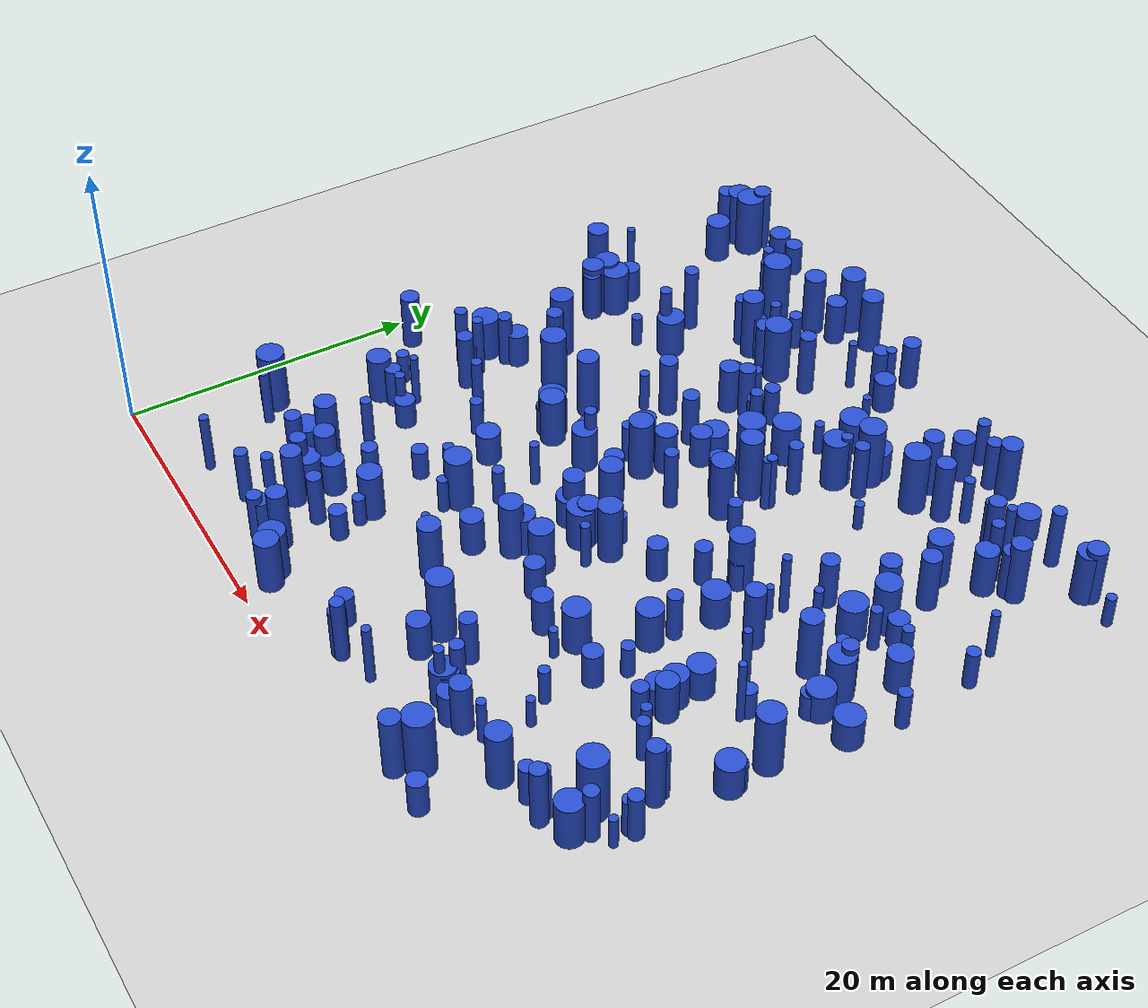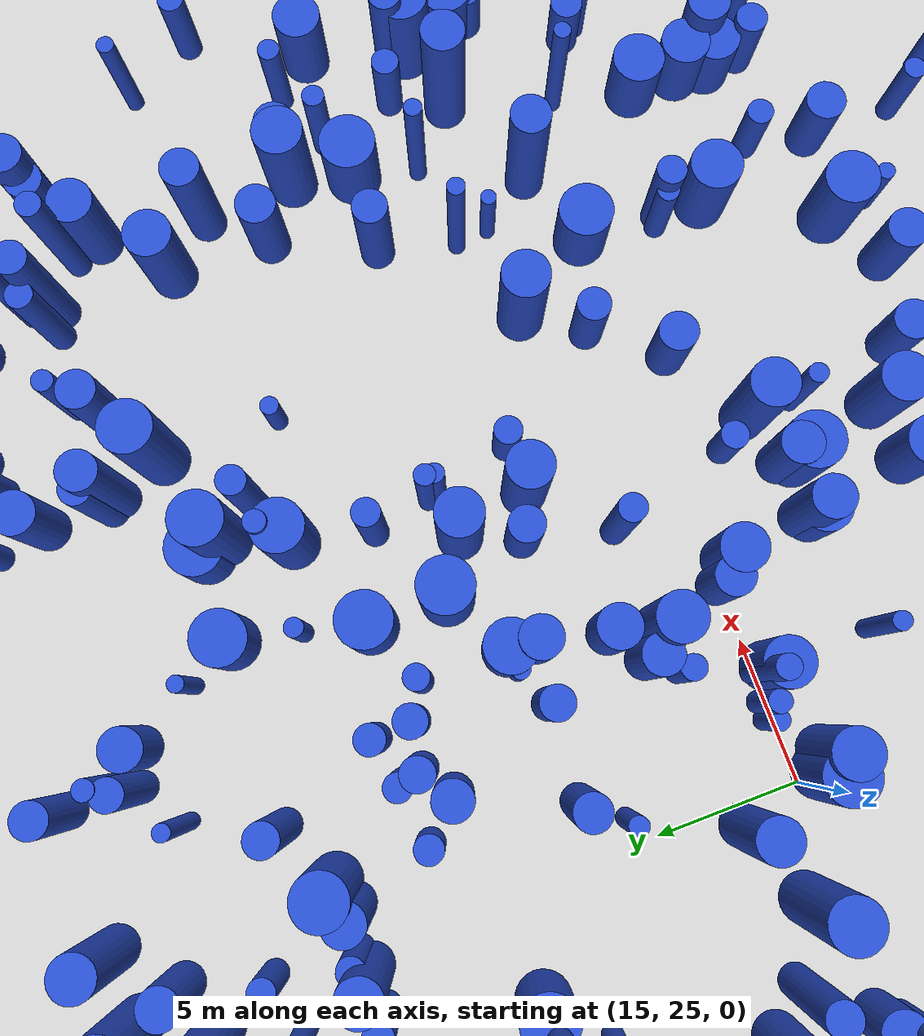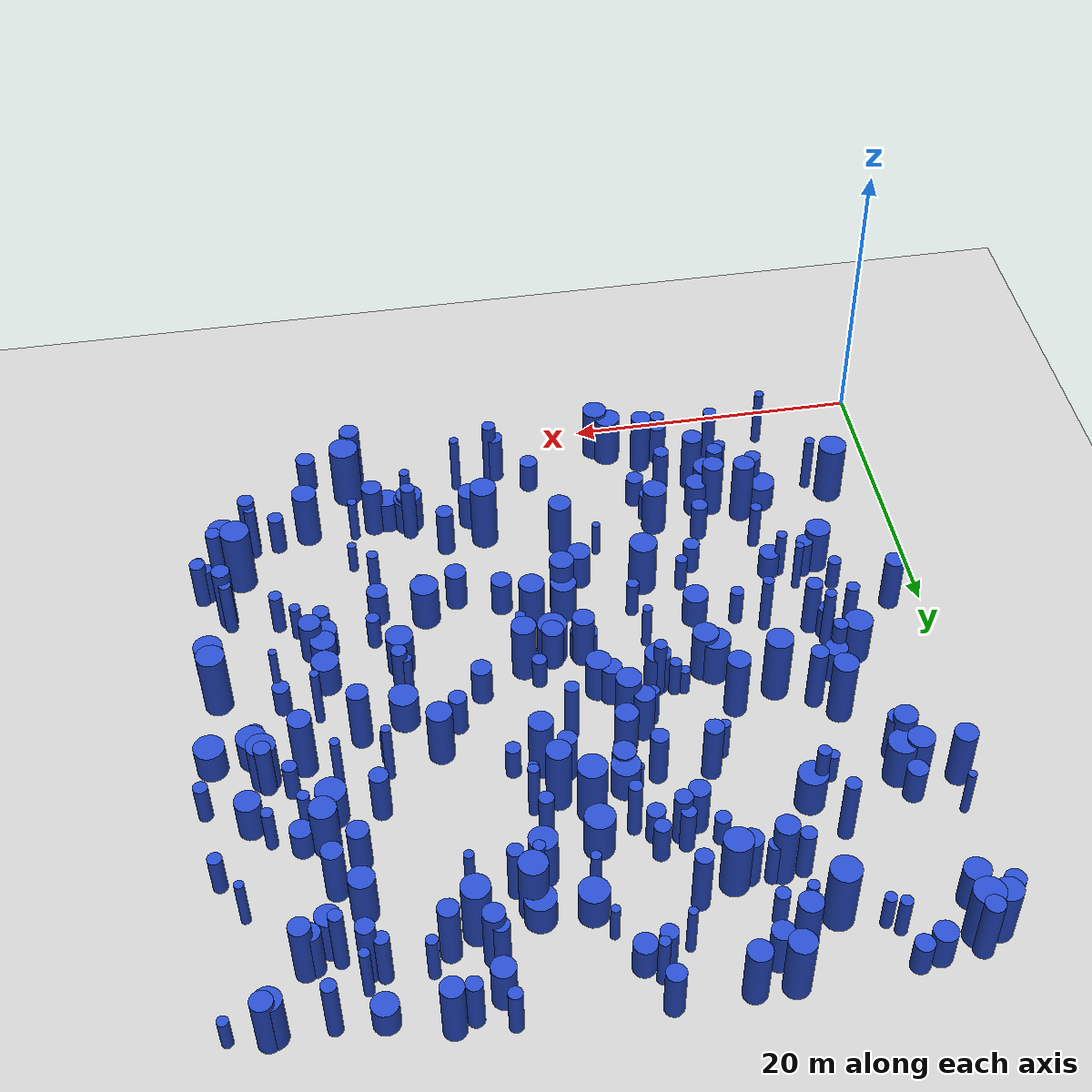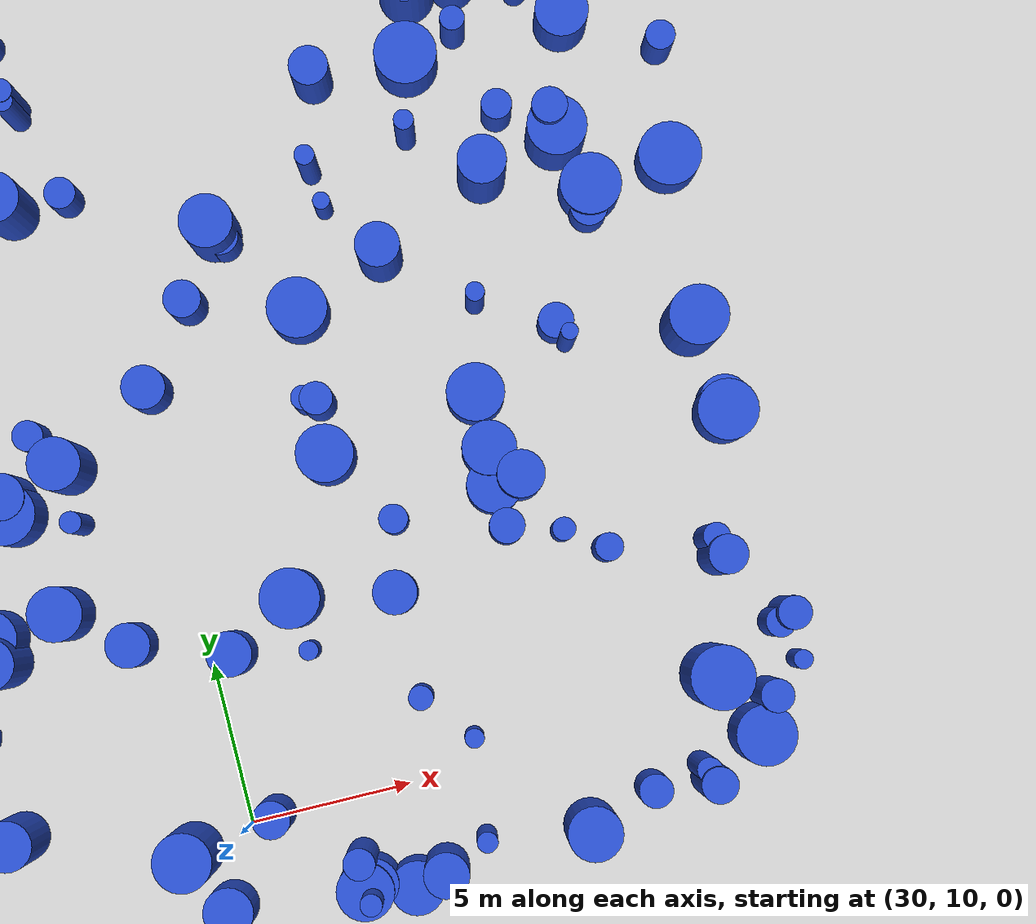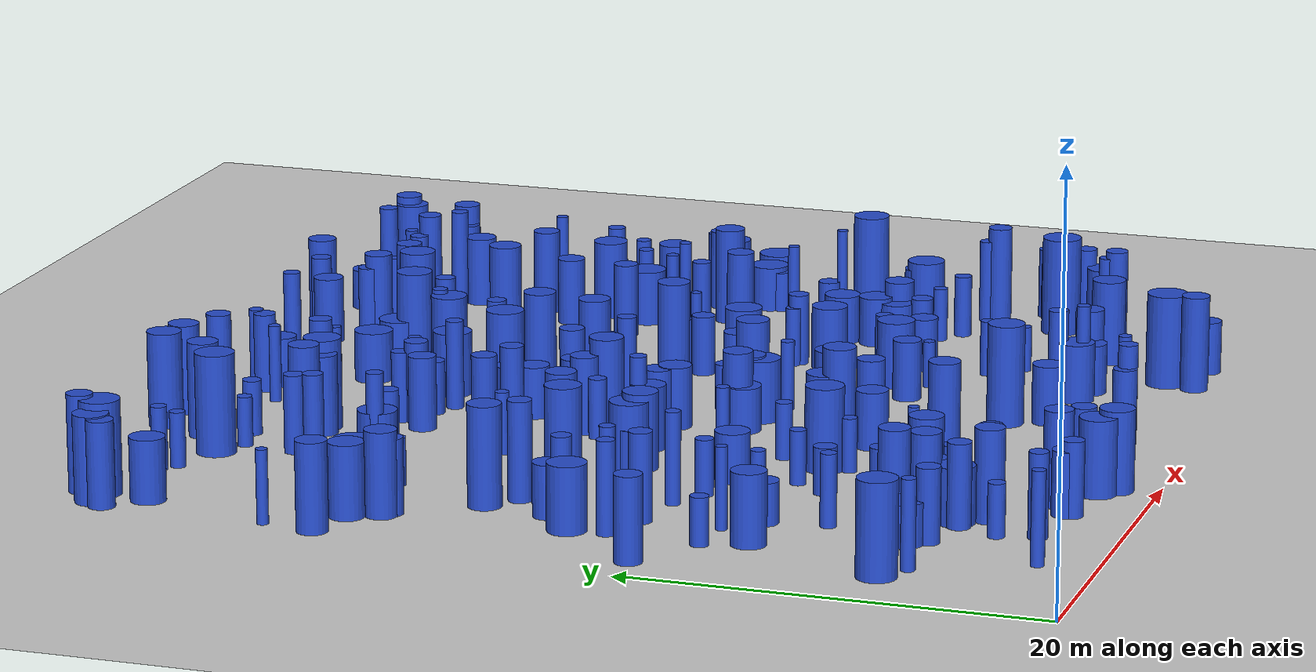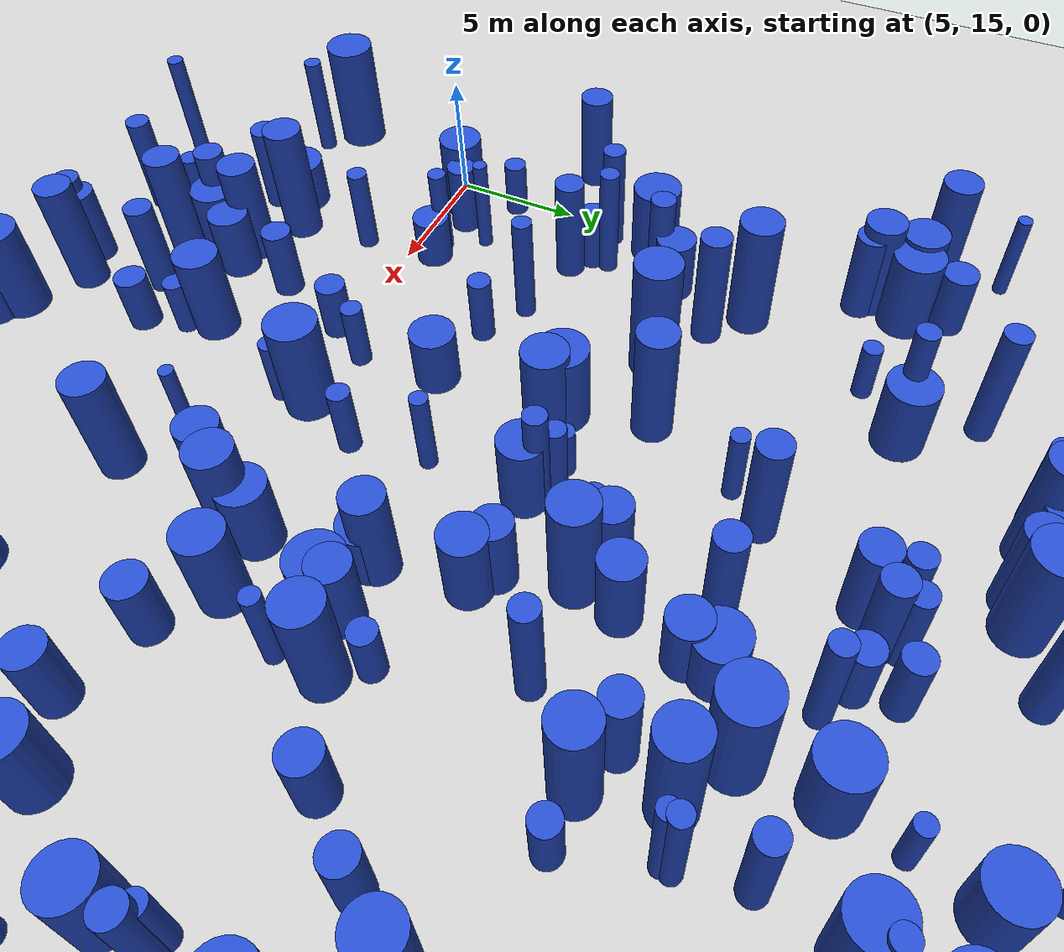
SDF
<sdf version="1.6">
 <world name="default">
  <plugin name="disable_physics" filename="libdisable_physics.so"/>
  <light name="sun" type="directional">
   <pose>0 0 10 0 -0 0</pose>
   <diffuse>0.8 0.8 0.8 1</diffuse>
   <specular>0.1 0.1 0.1 1</specular>
   <attenuation>
    <range>1000</range>
    <constant>0.9</constant>
    <linear>0.01</linear>
    <quadratic>0.001</quadratic>
   </attenuation>
   <direction>-0.5 0.5 -1</direction>
  </light>
  <model name="ground_plane">
   <static>1</static>
   <link name="link">
    <collision name="collision">
     <geometry><plane><normal>0 0 1</normal><size>100 100</size></plane></geometry>
     <surface><friction><ode><mu>100</mu><mu2>50</mu2></ode></friction></surface>
    </collision>
    <visual name="visual">
     <cast_shadows>0</cast_shadows>
     <geometry><plane><normal>0 0 1</normal><size>100 100</size></plane></geometry>
     <material>
      <script><uri>file://media/materials/scripts/gazebo.material</uri><name>Gazebo/Grey</name></script>
     </material>
    </visual>
   </link>
  </model>
  <gravity>0 0 -9.8</gravity>
  <magnetic_field>6e-06 2.3e-05 -4.2e-05</magnetic_field>
  <atmosphere type="adiabatic"/>
  <physics name="default_physics" default="0" type="ode">
   <max_step_size>0.001</max_step_size>
   <real_time_factor>1</real_time_factor>
   <real_time_update_rate>1000</real_time_update_rate>
  </physics>
  <scene><ambient>0.4 0.4 0.4 1</ambient><background>0.7 0.7 0.7 1</background><shadows>1</shadows></scene>
  <spherical_coordinates>
   <surface_model>EARTH_WGS84</surface_model>
   <latitude_deg>0</latitude_deg>
   <longitude_deg>0</longitude_deg>
   <elevation>0</elevation>
   <heading_deg>0</heading_deg>
  </spherical_coordinates>
  <model name="0">
   <static>0</static>
   <link name="link">
    <inertial>
     <mass>2</mass>
     <inertia><ixx>1.91349</ixx><ixy>0</ixy><ixz>0</ixz><iyy>1.91349</iyy><iyz>0</iyz><izz>0.709288</izz></inertia>
    </inertial>
    <collision name="collision">
     <geometry><cylinder><length>3.05828</length><radius>0.842192</radius></cylinder></geometry>
     <surface><contact><collide_without_contact>1</collide_without_contact></contact></surface>
    </collision>
    <visual name="visual">
     <geometry><cylinder><length>3.05828</length><radius>0.842192</radius></cylinder></geometry>
     <material>
      <script><uri>file://media/materials/scripts/gazebo.material</uri><name>Gazebo/Blue</name></script>
     </material>
    </visual>
    <gravity>0</gravity>
   </link>
   <pose>4.01882 43.668 1.52914 0 -0 0</pose>
  </model>
  <model name="1">
   <static>0</static>
   <link name="link">
    <inertial>
     <mass>2</mass>
     <inertia><ixx>4.03627</ixx><ixy>0</ixy><ixz>0</ixz><iyy>4.03627</iyy><iyz>0</iyz><izz>0.190273</izz></inertia>
    </inertial>
    <collision name="collision">
     <geometry><cylinder><length>4.86279</length><radius>0.436203</radius></cylinder></geometry>
     <surface><contact><collide_without_contact>1</collide_without_contact></contact></surface>
    </collision>
    <visual name="visual">
     <geometry><cylinder><length>4.86279</length><radius>0.436203</radius></cylinder></geometry>
     <material>
      <script><uri>file://media/materials/scripts/gazebo.material</uri><name>Gazebo/Blue</name></script>
     </material>
    </visual>
    <gravity>0</gravity>
   </link>
   <pose>40.5806 41.9272 2.4314 0 -0 0</pose>
  </model>
  <model name="2">
   <static>0</static>
   <link name="link">
    <inertial>
     <mass>2</mass>
     <inertia><ixx>4.06006</ixx><ixy>0</ixy><ixz>0</ixz><iyy>4.06006</iyy><iyz>0</iyz><izz>0.547674</izz></inertia>
    </inertial>
    <collision name="collision">
     <geometry><cylinder><length>4.76627</length><radius>0.74005</radius></cylinder></geometry>
     <surface><contact><collide_without_contact>1</collide_without_contact></contact></surface>
    </collision>
    <visual name="visual">
     <geometry><cylinder><length>4.76627</length><radius>0.74005</radius></cylinder></geometry>
     <material>
      <script><uri>file://media/materials/scripts/gazebo.material</uri><name>Gazebo/Blue</name></script>
     </material>
    </visual>
    <gravity>0</gravity>
   </link>
   <pose>14.3801 27.3031 2.38314 0 -0 0</pose>
  </model>
  <model name="3">
   <static>0</static>
   <link name="link">
    <inertial>
     <mass>2</mass>
     <inertia><ixx>2.87295</ixx><ixy>0</ixy><ixz>0</ixz><iyy>2.87295</iyy><iyz>0</iyz><izz>0.289082</izz></inertia>
    </inertial>
    <collision name="collision">
     <geometry><cylinder><length>4.04604</length><radius>0.537664</radius></cylinder></geometry>
     <surface><contact><collide_without_contact>1</collide_without_contact></contact></surface>
    </collision>
    <visual name="visual">
     <geometry><cylinder><length>4.04604</length><radius>0.537664</radius></cylinder></geometry>
     <material>
      <script><uri>file://media/materials/scripts/gazebo.material</uri><name>Gazebo/Blue</name></script>
     </material>
    </visual>
    <gravity>0</gravity>
   </link>
   <pose>31.5919 43.4807 2.02302 0 -0 0</pose>
  </model>
  <model name="4">
   <static>0</static>
   <link name="link">
    <inertial>
     <mass>2</mass>
     <inertia><ixx>3.99199</ixx><ixy>0</ixy><ixz>0</ixz><iyy>3.99199</iyy><iyz>0</iyz><izz>0.466161</izz></inertia>
    </inertial>
    <collision name="collision">
     <geometry><cylinder><length>4.74905</length><radius>0.68276</radius></cylinder></geometry>
     <surface><contact><collide_without_contact>1</collide_without_contact></contact></surface>
    </collision>
    <visual name="visual">
     <geometry><cylinder><length>4.74905</length><radius>0.68276</radius></cylinder></geometry>
     <material>
      <script><uri>file://media/materials/scripts/gazebo.material</uri><name>Gazebo/Blue</name></script>
     </material>
    </visual>
    <gravity>0</gravity>
   </link>
   <pose>36.5583 2.27425 2.37452 0 -0 0</pose>
  </model>
  <model name="5">
   <static>0</static>
   <link name="link">
    <inertial>
     <mass>2</mass>
     <inertia><ixx>2.58297</ixx><ixy>0</ixy><ixz>0</ixz><iyy>2.58297</iyy><iyz>0</iyz><izz>0.837419</izz></inertia>
    </inertial>
    <collision name="collision">
     <geometry><cylinder><length>3.60355</length><radius>0.915106</radius></cylinder></geometry>
     <surface><contact><collide_without_contact>1</collide_without_contact></contact></surface>
    </collision>
    <visual name="visual">
     <geometry><cylinder><length>3.60355</length><radius>0.915106</radius></cylinder></geometry>
     <material>
      <script><uri>file://media/materials/scripts/gazebo.material</uri><name>Gazebo/Blue</name></script>
     </material>
    </visual>
    <gravity>0</gravity>
   </link>
   <pose>44.1312 28.2563 1.80178 0 -0 0</pose>
  </model>
  <model name="6">
   <static>0</static>
   <link name="link">
    <inertial>
     <mass>2</mass>
     <inertia><ixx>1.45049</ixx><ixy>0</ixy><ixz>0</ixz><iyy>1.45049</iyy><iyz>0</iyz><izz>0.206698</izz></inertia>
    </inertial>
    <collision name="collision">
     <geometry><cylinder><length>2.84303</length><radius>0.454641</radius></cylinder></geometry>
     <surface><contact><collide_without_contact>1</collide_without_contact></contact></surface>
    </collision>
    <visual name="visual">
     <geometry><cylinder><length>2.84303</length><radius>0.454641</radius></cylinder></geometry>
     <material>
      <script><uri>file://media/materials/scripts/gazebo.material</uri><name>Gazebo/Blue</name></script>
     </material>
    </visual>
    <gravity>0</gravity>
   </link>
   <pose>47.896 30.2729 1.42152 0 -0 0</pose>
  </model>
  <model name="7">
   <static>0</static>
   <link name="link">
    <inertial>
     <mass>2</mass>
     <inertia><ixx>1.4943</ixx><ixy>0</ixy><ixz>0</ixz><iyy>1.4943</iyy><iyz>0</iyz><izz>0.904454</izz></inertia>
    </inertial>
    <collision name="collision">
     <geometry><cylinder><length>2.50048</length><radius>0.951028</radius></cylinder></geometry>
     <surface><contact><collide_without_contact>1</collide_without_contact></contact></surface>
    </collision>
    <visual name="visual">
     <geometry><cylinder><length>2.50048</length><radius>0.951028</radius></cylinder></geometry>
     <material>
      <script><uri>file://media/materials/scripts/gazebo.material</uri><name>Gazebo/Blue</name></script>
     </material>
    </visual>
    <gravity>0</gravity>
   </link>
   <pose>25.9011 41.0667 1.25024 0 -0 0</pose>
  </model>
  <model name="8">
   <static>0</static>
   <link name="link">
    <inertial>
     <mass>2</mass>
     <inertia><ixx>3.23535</ixx><ixy>0</ixy><ixz>0</ixz><iyy>3.23535</iyy><iyz>0</iyz><izz>0.666389</izz></inertia>
    </inertial>
    <collision name="collision">
     <geometry><cylinder><length>4.17288</length><radius>0.816326</radius></cylinder></geometry>
     <surface><contact><collide_without_contact>1</collide_without_contact></contact></surface>
    </collision>
    <visual name="visual">
     <geometry><cylinder><length>4.17288</length><radius>0.816326</radius></cylinder></geometry>
     <material>
      <script><uri>file://media/materials/scripts/gazebo.material</uri><name>Gazebo/Blue</name></script>
     </material>
    </visual>
    <gravity>0</gravity>
   </link>
   <pose>33.2137 27.9199 2.08644 0 -0 0</pose>
  </model>
  <model name="9">
   <static>0</static>
   <link name="link">
    <inertial>
     <mass>2</mass>
     <inertia>
      <ixx>0.837934</ixx>
      <ixy>0</ixy>
      <ixz>0</ixz>
      <iyy>0.837934</iyy>
      <iyz>0</iyz>
      <izz>0.32901</izz>
     </inertia>
    </inertial>
    <collision name="collision">
     <geometry><cylinder><length>2.01012</length><radius>0.573593</radius></cylinder></geometry>
     <surface><contact><collide_without_contact>1</collide_without_contact></contact></surface>
    </collision>
    <visual name="visual">
     <geometry><cylinder><length>2.01012</length><radius>0.573593</radius></cylinder></geometry>
     <material>
      <script><uri>file://media/materials/scripts/gazebo.material</uri><name>Gazebo/Blue</name></script>
     </material>
    </visual>
    <gravity>0</gravity>
   </link>
   <pose>44.5713 25.7943 1.00506 0 -0 0</pose>
  </model>
  <model name="10">
   <static>0</static>
   <link name="link">
    <inertial>
     <mass>2</mass>
     <inertia>
      <ixx>0.892334</ixx>
      <ixy>0</ixy>
      <ixz>0</ixz>
      <iyy>0.892334</iyy>
      <iyz>0</iyz>
      <izz>0.0903005</izz>
     </inertia>
    </inertial>
    <collision name="collision">
     <geometry><cylinder><length>2.25457</length><radius>0.3005</radius></cylinder></geometry>
     <surface><contact><collide_without_contact>1</collide_without_contact></contact></surface>
    </collision>
    <visual name="visual">
     <geometry><cylinder><length>2.25457</length><radius>0.3005</radius></cylinder></geometry>
     <material>
      <script><uri>file://media/materials/scripts/gazebo.material</uri><name>Gazebo/Blue</name></script>
     </material>
    </visual>
    <gravity>0</gravity>
   </link>
   <pose>37.2761 10.9514 1.12729 0 -0 0</pose>
  </model>
  <model name="11">
   <static>0</static>
   <link name="link">
    <inertial>
     <mass>2</mass>
     <inertia><ixx>1.92531</ixx><ixy>0</ixy><ixz>0</ixz><iyy>1.92531</iyy><iyz>0</iyz><izz>0.103853</izz></inertia>
    </inertial>
    <collision name="collision">
     <geometry><cylinder><length>3.35266</length><radius>0.322263</radius></cylinder></geometry>
     <surface><contact><collide_without_contact>1</collide_without_contact></contact></surface>
    </collision>
    <visual name="visual">
     <geometry><cylinder><length>3.35266</length><radius>0.322263</radius></cylinder></geometry>
     <material>
      <script><uri>file://media/materials/scripts/gazebo.material</uri><name>Gazebo/Blue</name></script>
     </material>
    </visual>
    <gravity>0</gravity>
   </link>
   <pose>18.8928 20.868 1.67633 0 -0 0</pose>
  </model>
  <model name="12">
   <static>0</static>
   <link name="link">
    <inertial>
     <mass>2</mass>
     <inertia><ixx>2.8515</ixx><ixy>0</ixy><ixz>0</ixz><iyy>2.8515</iyy><iyz>0</iyz><izz>0.315958</izz></inertia>
    </inertial>
    <collision name="collision">
     <geometry><cylinder><length>4.02009</length><radius>0.562101</radius></cylinder></geometry>
     <surface><contact><collide_without_contact>1</collide_without_contact></contact></surface>
    </collision>
    <visual name="visual">
     <geometry><cylinder><length>4.02009</length><radius>0.562101</radius></cylinder></geometry>
     <material>
      <script><uri>file://media/materials/scripts/gazebo.material</uri><name>Gazebo/Blue</name></script>
     </material>
    </visual>
    <gravity>0</gravity>
   </link>
   <pose>11.5625 7.45117 2.01004 0 -0 0</pose>
  </model>
  <model name="13">
   <static>0</static>
   <link name="link">
    <inertial>
     <mass>2</mass>
     <inertia><ixx>1.70434</ixx><ixy>0</ixy><ixz>0</ixz><iyy>1.70434</iyy><iyz>0</iyz><izz>0.588243</izz></inertia>
    </inertial>
    <collision name="collision">
     <geometry><cylinder><length>2.90883</length><radius>0.76697</radius></cylinder></geometry>
     <surface><contact><collide_without_contact>1</collide_without_contact></contact></surface>
    </collision>
    <visual name="visual">
     <geometry><cylinder><length>2.90883</length><radius>0.76697</radius></cylinder></geometry>
     <material>
      <script><uri>file://media/materials/scripts/gazebo.material</uri><name>Gazebo/Blue</name></script>
     </material>
    </visual>
    <gravity>0</gravity>
   </link>
   <pose>28.8619 7.69367 1.45441 0 -0 0</pose>
  </model>
  <model name="14">
   <static>0</static>
   <link name="link">
    <inertial>
     <mass>2</mass>
     <inertia><ixx>4.30261</ixx><ixy>0</ixy><ixz>0</ixz><iyy>4.30261</iyy><iyz>0</iyz><izz>0.6461</izz></inertia>
    </inertial>
    <collision name="collision">
     <geometry><cylinder><length>4.88644</length><radius>0.803803</radius></cylinder></geometry>
     <surface><contact><collide_without_contact>1</collide_without_contact></contact></surface>
    </collision>
    <visual name="visual">
     <geometry><cylinder><length>4.88644</length><radius>0.803803</radius></cylinder></geometry>
     <material>
      <script><uri>file://media/materials/scripts/gazebo.material</uri><name>Gazebo/Blue</name></script>
     </material>
    </visual>
    <gravity>0</gravity>
   </link>
   <pose>7.93289 28.7579 2.44322 0 -0 0</pose>
  </model>
  <model name="15">
   <static>0</static>
   <link name="link">
    <inertial>
     <mass>2</mass>
     <inertia><ixx>2.85679</ixx><ixy>0</ixy><ixz>0</ixz><iyy>2.85679</iyy><iyz>0</iyz><izz>0.328589</izz></inertia>
    </inertial>
    <collision name="collision">
     <geometry><cylinder><length>4.01932</length><radius>0.573227</radius></cylinder></geometry>
     <surface><contact><collide_without_contact>1</collide_without_contact></contact></surface>
    </collision>
    <visual name="visual">
     <geometry><cylinder><length>4.01932</length><radius>0.573227</radius></cylinder></geometry>
     <material>
      <script><uri>file://media/materials/scripts/gazebo.material</uri><name>Gazebo/Blue</name></script>
     </material>
    </visual>
    <gravity>0</gravity>
   </link>
   <pose>20.2805 31.834 2.00966 0 -0 0</pose>
  </model>
  <model name="16">
   <static>0</static>
   <link name="link">
    <inertial>
     <mass>2</mass>
     <inertia><ixx>1.17439</ixx><ixy>0</ixy><ixz>0</ixz><iyy>1.17439</iyy><iyz>0</iyz><izz>0.167306</izz></inertia>
    </inertial>
    <collision name="collision">
     <geometry><cylinder><length>2.55821</length><radius>0.40903</radius></cylinder></geometry>
     <surface><contact><collide_without_contact>1</collide_without_contact></contact></surface>
    </collision>
    <visual name="visual">
     <geometry><cylinder><length>2.55821</length><radius>0.40903</radius></cylinder></geometry>
     <material>
      <script><uri>file://media/materials/scripts/gazebo.material</uri><name>Gazebo/Blue</name></script>
     </material>
    </visual>
    <gravity>0</gravity>
   </link>
   <pose>10.7144 5.49413 1.27911 0 -0 0</pose>
  </model>
  <model name="17">
   <static>0</static>
   <link name="link">
    <inertial>
     <mass>2</mass>
     <inertia><ixx>2.81626</ixx><ixy>0</ixy><ixz>0</ixz><iyy>2.81626</iyy><iyz>0</iyz><izz>0.482913</izz></inertia>
    </inertial>
    <collision name="collision">
     <geometry><cylinder><length>3.9305</length><radius>0.694919</radius></cylinder></geometry>
     <surface><contact><collide_without_contact>1</collide_without_contact></contact></surface>
    </collision>
    <visual name="visual">
     <geometry><cylinder><length>3.9305</length><radius>0.694919</radius></cylinder></geometry>
     <material>
      <script><uri>file://media/materials/scripts/gazebo.material</uri><name>Gazebo/Blue</name></script>
     </material>
    </visual>
    <gravity>0</gravity>
   </link>
   <pose>35.5044 7.28574 1.96525 0 -0 0</pose>
  </model>
  <model name="18">
   <static>0</static>
   <link name="link">
    <inertial>
     <mass>2</mass>
     <inertia><ixx>2.75852</ixx><ixy>0</ixy><ixz>0</ixz><iyy>2.75852</iyy><iyz>0</iyz><izz>0.232447</izz></inertia>
    </inertial>
    <collision name="collision">
     <geometry><cylinder><length>3.98168</length><radius>0.482127</radius></cylinder></geometry>
     <surface><contact><collide_without_contact>1</collide_without_contact></contact></surface>
    </collision>
    <visual name="visual">
     <geometry><cylinder><length>3.98168</length><radius>0.482127</radius></cylinder></geometry>
     <material>
      <script><uri>file://media/materials/scripts/gazebo.material</uri><name>Gazebo/Blue</name></script>
     </material>
    </visual>
    <gravity>0</gravity>
   </link>
   <pose>7.12648 24.7804 1.99084 0 -0 0</pose>
  </model>
  <model name="19">
   <static>0</static>
   <link name="link">
    <inertial>
     <mass>2</mass>
     <inertia><ixx>2.15702</ixx><ixy>0</ixy><ixz>0</ixz><iyy>2.15702</iyy><iyz>0</iyz><izz>0.863134</izz></inertia>
    </inertial>
    <collision name="collision">
     <geometry><cylinder><length>3.21756</length><radius>0.92905</radius></cylinder></geometry>
     <surface><contact><collide_without_contact>1</collide_without_contact></contact></surface>
    </collision>
    <visual name="visual">
     <geometry><cylinder><length>3.21756</length><radius>0.92905</radius></cylinder></geometry>
     <material>
      <script><uri>file://media/materials/scripts/gazebo.material</uri><name>Gazebo/Blue</name></script>
     </material>
    </visual>
    <gravity>0</gravity>
   </link>
   <pose>5.64396 24.0193 1.60878 0 -0 0</pose>
  </model>
  <model name="20">
   <static>0</static>
   <link name="link">
    <inertial>
     <mass>2</mass>
     <inertia><ixx>1.70834</ixx><ixy>0</ixy><ixz>0</ixz><iyy>1.70834</iyy><iyz>0</iyz><izz>0.487048</izz></inertia>
    </inertial>
    <collision name="collision">
     <geometry><cylinder><length>2.96461</length><radius>0.697888</radius></cylinder></geometry>
     <surface><contact><collide_without_contact>1</collide_without_contact></contact></surface>
    </collision>
    <visual name="visual">
     <geometry><cylinder><length>2.96461</length><radius>0.697888</radius></cylinder></geometry>
     <material>
      <script><uri>file://media/materials/scripts/gazebo.material</uri><name>Gazebo/Blue</name></script>
     </material>
    </visual>
    <gravity>0</gravity>
   </link>
   <pose>30.726 15.2064 1.4823 0 -0 0</pose>
  </model>
  <model name="21">
   <static>0</static>
   <link name="link">
    <inertial>
     <mass>2</mass>
     <inertia><ixx>1.51849</ixx><ixy>0</ixy><ixz>0</ixz><iyy>1.51849</iyy><iyz>0</iyz><izz>0.311536</izz></inertia>
    </inertial>
    <collision name="collision">
     <geometry><cylinder><length>2.85943</length><radius>0.558154</radius></cylinder></geometry>
     <surface><contact><collide_without_contact>1</collide_without_contact></contact></surface>
    </collision>
    <visual name="visual">
     <geometry><cylinder><length>2.85943</length><radius>0.558154</radius></cylinder></geometry>
     <material>
      <script><uri>file://media/materials/scripts/gazebo.material</uri><name>Gazebo/Blue</name></script>
     </material>
    </visual>
    <gravity>0</gravity>
   </link>
   <pose>13.4368 11.5878 1.42972 0 -0 0</pose>
  </model>
  <model name="22">
   <static>0</static>
   <link name="link">
    <inertial>
     <mass>2</mass>
     <inertia><ixx>1.35363</ixx><ixy>0</ixy><ixz>0</ixz><iyy>1.35363</iyy><iyz>0</iyz><izz>0.709963</izz></inertia>
    </inertial>
    <collision name="collision">
     <geometry><cylinder><length>2.44783</length><radius>0.842593</radius></cylinder></geometry>
     <surface><contact><collide_without_contact>1</collide_without_contact></contact></surface>
    </collision>
    <visual name="visual">
     <geometry><cylinder><length>2.44783</length><radius>0.842593</radius></cylinder></geometry>
     <material>
      <script><uri>file://media/materials/scripts/gazebo.material</uri><name>Gazebo/Blue</name></script>
     </material>
    </visual>
    <gravity>0</gravity>
   </link>
   <pose>39.8297 19.3697 1.22391 0 -0 0</pose>
  </model>
  <model name="23">
   <static>0</static>
   <link name="link">
    <inertial>
     <mass>2</mass>
     <inertia>
      <ixx>1.21853</ixx>
      <ixy>0</ixy>
      <ixz>0</ixz>
      <iyy>1.21853</iyy>
      <iyz>0</iyz>
      <izz>0.0726974</izz>
     </inertia>
    </inertial>
    <collision name="collision">
     <geometry><cylinder><length>2.66328</length><radius>0.269625</radius></cylinder></geometry>
     <surface><contact><collide_without_contact>1</collide_without_contact></contact></surface>
    </collision>
    <visual name="visual">
     <geometry><cylinder><length>2.66328</length><radius>0.269625</radius></cylinder></geometry>
     <material>
      <script><uri>file://media/materials/scripts/gazebo.material</uri><name>Gazebo/Blue</name></script>
     </material>
    </visual>
    <gravity>0</gravity>
   </link>
   <pose>20.7295 12.1101 1.33164 0 -0 0</pose>
  </model>
  <model name="24">
   <static>0</static>
   <link name="link">
    <inertial>
     <mass>2</mass>
     <inertia><ixx>1.33949</ixx><ixy>0</ixy><ixz>0</ixz><iyy>1.33949</iyy><iyz>0</iyz><izz>0.222603</izz></inertia>
    </inertial>
    <collision name="collision">
     <geometry><cylinder><length>2.71462</length><radius>0.471809</radius></cylinder></geometry>
     <surface><contact><collide_without_contact>1</collide_without_contact></contact></surface>
    </collision>
    <visual name="visual">
     <geometry><cylinder><length>2.71462</length><radius>0.471809</radius></cylinder></geometry>
     <material>
      <script><uri>file://media/materials/scripts/gazebo.material</uri><name>Gazebo/Blue</name></script>
     </material>
    </visual>
    <gravity>0</gravity>
   </link>
   <pose>42.5584 29.4439 1.35731 0 -0 0</pose>
  </model>
  <model name="25">
   <static>0</static>
   <link name="link">
    <inertial>
     <mass>2</mass>
     <inertia><ixx>3.93705</ixx><ixy>0</ixy><ixz>0</ixz><iyy>3.93705</iyy><iyz>0</iyz><izz>0.614086</izz></inertia>
    </inertial>
    <collision name="collision">
     <geometry><cylinder><length>4.66691</length><radius>0.783636</radius></cylinder></geometry>
     <surface><contact><collide_without_contact>1</collide_without_contact></contact></surface>
    </collision>
    <visual name="visual">
     <geometry><cylinder><length>4.66691</length><radius>0.783636</radius></cylinder></geometry>
     <material>
      <script><uri>file://media/materials/scripts/gazebo.material</uri><name>Gazebo/Blue</name></script>
     </material>
    </visual>
    <gravity>0</gravity>
   </link>
   <pose>27.2784 30.0628 2.33346 0 -0 0</pose>
  </model>
  <model name="26">
   <static>0</static>
   <link name="link">
    <inertial>
     <mass>2</mass>
     <inertia>
      <ixx>0.763475</ixx>
      <ixy>0</ixy>
      <ixz>0</ixz>
      <iyy>0.763475</iyy>
      <iyz>0</iyz>
      <izz>0.108219</izz>
     </inertia>
    </inertial>
    <collision name="collision">
     <geometry><cylinder><length>2.06305</length><radius>0.328966</radius></cylinder></geometry>
     <surface><contact><collide_without_contact>1</collide_without_contact></contact></surface>
    </collision>
    <visual name="visual">
     <geometry><cylinder><length>2.06305</length><radius>0.328966</radius></cylinder></geometry>
     <material>
      <script><uri>file://media/materials/scripts/gazebo.material</uri><name>Gazebo/Blue</name></script>
     </material>
    </visual>
    <gravity>0</gravity>
   </link>
   <pose>21.6361 32.4049 1.03153 0 -0 0</pose>
  </model>
  <model name="27">
   <static>0</static>
   <link name="link">
    <inertial>
     <mass>2</mass>
     <inertia>
      <ixx>0.751136</ixx>
      <ixy>0</ixy>
      <ixz>0</ixz>
      <iyy>0.751136</iyy>
      <iyz>0</iyz>
      <izz>0.125842</izz>
     </inertia>
    </inertial>
    <collision name="collision">
     <geometry><cylinder><length>2.03207</length><radius>0.354742</radius></cylinder></geometry>
     <surface><contact><collide_without_contact>1</collide_without_contact></contact></surface>
    </collision>
    <visual name="visual">
     <geometry><cylinder><length>2.03207</length><radius>0.354742</radius></cylinder></geometry>
     <material>
      <script><uri>file://media/materials/scripts/gazebo.material</uri><name>Gazebo/Blue</name></script>
     </material>
    </visual>
    <gravity>0</gravity>
   </link>
   <pose>17.2823 25.2801 1.01603 0 -0 0</pose>
  </model>
  <model name="28">
   <static>0</static>
   <link name="link">
    <inertial>
     <mass>2</mass>
     <inertia><ixx>3.31167</ixx><ixy>0</ixy><ixz>0</ixz><iyy>3.31167</iyy><iyz>0</iyz><izz>0.713837</izz></inertia>
    </inertial>
    <collision name="collision">
     <geometry><cylinder><length>4.21052</length><radius>0.844889</radius></cylinder></geometry>
     <surface><contact><collide_without_contact>1</collide_without_contact></contact></surface>
    </collision>
    <visual name="visual">
     <geometry><cylinder><length>4.21052</length><radius>0.844889</radius></cylinder></geometry>
     <material>
      <script><uri>file://media/materials/scripts/gazebo.material</uri><name>Gazebo/Blue</name></script>
     </material>
    </visual>
    <gravity>0</gravity>
   </link>
   <pose>3.07266 46.0083 2.10526 0 -0 0</pose>
  </model>
  <model name="29">
   <static>0</static>
   <link name="link">
    <inertial>
     <mass>2</mass>
     <inertia><ixx>1.20712</ixx><ixy>0</ixy><ixz>0</ixz><iyy>1.20712</iyy><iyz>0</iyz><izz>0.139764</izz></inertia>
    </inertial>
    <collision name="collision">
     <geometry><cylinder><length>2.61217</length><radius>0.37385</radius></cylinder></geometry>
     <surface><contact><collide_without_contact>1</collide_without_contact></contact></surface>
    </collision>
    <visual name="visual">
     <geometry><cylinder><length>2.61217</length><radius>0.37385</radius></cylinder></geometry>
     <material>
      <script><uri>file://media/materials/scripts/gazebo.material</uri><name>Gazebo/Blue</name></script>
     </material>
    </visual>
    <gravity>0</gravity>
   </link>
   <pose>18.2533 14.5095 1.30608 0 -0 0</pose>
  </model>
  <model name="30">
   <static>0</static>
   <link name="link">
    <inertial>
     <mass>2</mass>
     <inertia><ixx>4.21766</ixx><ixy>0</ixy><ixz>0</ixz><iyy>4.21766</iyy><iyz>0</iyz><izz>0.543405</izz></inertia>
    </inertial>
    <collision name="collision">
     <geometry><cylinder><length>4.86577</length><radius>0.73716</radius></cylinder></geometry>
     <surface><contact><collide_without_contact>1</collide_without_contact></contact></surface>
    </collision>
    <visual name="visual">
     <geometry><cylinder><length>4.86577</length><radius>0.73716</radius></cylinder></geometry>
     <material>
      <script><uri>file://media/materials/scripts/gazebo.material</uri><name>Gazebo/Blue</name></script>
     </material>
    </visual>
    <gravity>0</gravity>
   </link>
   <pose>10.1121 10.083 2.43289 0 -0 0</pose>
  </model>
  <model name="31">
   <static>0</static>
   <link name="link">
    <inertial>
     <mass>2</mass>
     <inertia><ixx>2.85237</ixx><ixy>0</ixy><ixz>0</ixz><iyy>2.85237</iyy><iyz>0</iyz><izz>0.298801</izz></inertia>
    </inertial>
    <collision name="collision">
     <geometry><cylinder><length>4.02714</length><radius>0.546627</radius></cylinder></geometry>
     <surface><contact><collide_without_contact>1</collide_without_contact></contact></surface>
    </collision>
    <visual name="visual">
     <geometry><cylinder><length>4.02714</length><radius>0.546627</radius></cylinder></geometry>
     <material>
      <script><uri>file://media/materials/scripts/gazebo.material</uri><name>Gazebo/Blue</name></script>
     </material>
    </visual>
    <gravity>0</gravity>
   </link>
   <pose>44.0403 28.8417 2.01357 0 -0 0</pose>
  </model>
  <model name="32">
   <static>0</static>
   <link name="link">
    <inertial>
     <mass>2</mass>
     <inertia><ixx>2.84004</ixx><ixy>0</ixy><ixz>0</ixz><iyy>2.84004</iyy><iyz>0</iyz><izz>0.148295</izz></inertia>
    </inertial>
    <collision name="collision">
     <geometry><cylinder><length>4.07374</length><radius>0.385092</radius></cylinder></geometry>
     <surface><contact><collide_without_contact>1</collide_without_contact></contact></surface>
    </collision>
    <visual name="visual">
     <geometry><cylinder><length>4.07374</length><radius>0.385092</radius></cylinder></geometry>
     <material>
      <script><uri>file://media/materials/scripts/gazebo.material</uri><name>Gazebo/Blue</name></script>
     </material>
    </visual>
    <gravity>0</gravity>
   </link>
   <pose>28.69 38.5987 2.03687 0 -0 0</pose>
  </model>
  <model name="33">
   <static>0</static>
   <link name="link">
    <inertial>
     <mass>2</mass>
     <inertia><ixx>3.79607</ixx><ixy>0</ixy><ixz>0</ixz><iyy>3.79607</iyy><iyz>0</iyz><izz>0.307208</izz></inertia>
    </inertial>
    <collision name="collision">
     <geometry><cylinder><length>4.67491</length><radius>0.554264</radius></cylinder></geometry>
     <surface><contact><collide_without_contact>1</collide_without_contact></contact></surface>
    </collision>
    <visual name="visual">
     <geometry><cylinder><length>4.67491</length><radius>0.554264</radius></cylinder></geometry>
     <material>
      <script><uri>file://media/materials/scripts/gazebo.material</uri><name>Gazebo/Blue</name></script>
     </material>
    </visual>
    <gravity>0</gravity>
   </link>
   <pose>43.9821 7.96842 2.33746 0 -0 0</pose>
  </model>
  <model name="34">
   <static>0</static>
   <link name="link">
    <inertial>
     <mass>2</mass>
     <inertia><ixx>2.43561</ixx><ixy>0</ixy><ixz>0</ixz><iyy>2.43561</iyy><iyz>0</iyz><izz>0.710721</izz></inertia>
    </inertial>
    <collision name="collision">
     <geometry><cylinder><length>3.53292</length><radius>0.843043</radius></cylinder></geometry>
     <surface><contact><collide_without_contact>1</collide_without_contact></contact></surface>
    </collision>
    <visual name="visual">
     <geometry><cylinder><length>3.53292</length><radius>0.843043</radius></cylinder></geometry>
     <material>
      <script><uri>file://media/materials/scripts/gazebo.material</uri><name>Gazebo/Blue</name></script>
     </material>
    </visual>
    <gravity>0</gravity>
   </link>
   <pose>25.9964 17.6182 1.76646 0 -0 0</pose>
  </model>
  <model name="35">
   <static>0</static>
   <link name="link">
    <inertial>
     <mass>2</mass>
     <inertia><ixx>4.21675</ixx><ixy>0</ixy><ixz>0</ixz><iyy>4.21675</iyy><iyz>0</iyz><izz>0.78183</izz></inertia>
    </inertial>
    <collision name="collision">
     <geometry><cylinder><length>4.79114</length><radius>0.884211</radius></cylinder></geometry>
     <surface><contact><collide_without_contact>1</collide_without_contact></contact></surface>
    </collision>
    <visual name="visual">
     <geometry><cylinder><length>4.79114</length><radius>0.884211</radius></cylinder></geometry>
     <material>
      <script><uri>file://media/materials/scripts/gazebo.material</uri><name>Gazebo/Blue</name></script>
     </material>
    </visual>
    <gravity>0</gravity>
   </link>
   <pose>32.6922 41.2787 2.39557 0 -0 0</pose>
  </model>
  <model name="36">
   <static>0</static>
   <link name="link">
    <inertial>
     <mass>2</mass>
     <inertia><ixx>2.9244</ixx><ixy>0</ixy><ixz>0</ixz><iyy>2.9244</iyy><iyz>0</iyz><izz>0.736061</izz></inertia>
    </inertial>
    <collision name="collision">
     <geometry><cylinder><length>3.9164</length><radius>0.85794</radius></cylinder></geometry>
     <surface><contact><collide_without_contact>1</collide_without_contact></contact></surface>
    </collision>
    <visual name="visual">
     <geometry><cylinder><length>3.9164</length><radius>0.85794</radius></cylinder></geometry>
     <material>
      <script><uri>file://media/materials/scripts/gazebo.material</uri><name>Gazebo/Blue</name></script>
     </material>
    </visual>
    <gravity>0</gravity>
   </link>
   <pose>40.7714 33.7648 1.9582 0 -0 0</pose>
  </model>
  <model name="37">
   <static>0</static>
   <link name="link">
    <inertial>
     <mass>2</mass>
     <inertia><ixx>4.51841</ixx><ixy>0</ixy><ixz>0</ixz><iyy>4.51841</iyy><iyz>0</iyz><izz>0.944518</izz></inertia>
    </inertial>
    <collision name="collision">
     <geometry><cylinder><length>4.92716</length><radius>0.971863</radius></cylinder></geometry>
     <surface><contact><collide_without_contact>1</collide_without_contact></contact></surface>
    </collision>
    <visual name="visual">
     <geometry><cylinder><length>4.92716</length><radius>0.971863</radius></cylinder></geometry>
     <material>
      <script><uri>file://media/materials/scripts/gazebo.material</uri><name>Gazebo/Blue</name></script>
     </material>
    </visual>
    <gravity>0</gravity>
   </link>
   <pose>44.825 11.0247 2.46358 0 -0 0</pose>
  </model>
  <model name="38">
   <static>0</static>
   <link name="link">
    <inertial>
     <mass>2</mass>
     <inertia><ixx>2.59248</ixx><ixy>0</ixy><ixz>0</ixz><iyy>2.59248</iyy><iyz>0</iyz><izz>0.279767</izz></inertia>
    </inertial>
    <collision name="collision">
     <geometry><cylinder><length>3.83609</length><radius>0.52893</radius></cylinder></geometry>
     <surface><contact><collide_without_contact>1</collide_without_contact></contact></surface>
    </collision>
    <visual name="visual">
     <geometry><cylinder><length>3.83609</length><radius>0.52893</radius></cylinder></geometry>
     <material>
      <script><uri>file://media/materials/scripts/gazebo.material</uri><name>Gazebo/Blue</name></script>
     </material>
    </visual>
    <gravity>0</gravity>
   </link>
   <pose>15.2362 6.93709 1.91805 0 -0 0</pose>
  </model>
  <model name="39">
   <static>0</static>
   <link name="link">
    <inertial>
     <mass>2</mass>
     <inertia><ixx>3.37987</ixx><ixy>0</ixy><ixz>0</ixz><iyy>3.37987</iyy><iyz>0</iyz><izz>0.590027</izz></inertia>
    </inertial>
    <collision name="collision">
     <geometry><cylinder><length>4.30223</length><radius>0.768132</radius></cylinder></geometry>
     <surface><contact><collide_without_contact>1</collide_without_contact></contact></surface>
    </collision>
    <visual name="visual">
     <geometry><cylinder><length>4.30223</length><radius>0.768132</radius></cylinder></geometry>
     <material>
      <script><uri>file://media/materials/scripts/gazebo.material</uri><name>Gazebo/Blue</name></script>
     </material>
    </visual>
    <gravity>0</gravity>
   </link>
   <pose>23.0982 11.2765 2.15111 0 -0 0</pose>
  </model>
  <model name="40">
   <static>0</static>
   <link name="link">
    <inertial>
     <mass>2</mass>
     <inertia><ixx>4.04443</ixx><ixy>0</ixy><ixz>0</ixz><iyy>4.04443</iyy><iyz>0</iyz><izz>0.995933</izz></inertia>
    </inertial>
    <collision name="collision">
     <geometry><cylinder><length>4.61289</length><radius>0.997965</radius></cylinder></geometry>
     <surface><contact><collide_without_contact>1</collide_without_contact></contact></surface>
    </collision>
    <visual name="visual">
     <geometry><cylinder><length>4.61289</length><radius>0.997965</radius></cylinder></geometry>
     <material>
      <script><uri>file://media/materials/scripts/gazebo.material</uri><name>Gazebo/Blue</name></script>
     </material>
    </visual>
    <gravity>0</gravity>
   </link>
   <pose>37.0797 3.78821 2.30645 0 -0 0</pose>
  </model>
  <model name="41">
   <static>0</static>
   <link name="link">
    <inertial>
     <mass>2</mass>
     <inertia><ixx>1.78705</ixx><ixy>0</ixy><ixz>0</ixz><iyy>1.78705</iyy><iyz>0</iyz><izz>0.141727</izz></inertia>
    </inertial>
    <collision name="collision">
     <geometry><cylinder><length>3.20891</length><radius>0.376467</radius></cylinder></geometry>
     <surface><contact><collide_without_contact>1</collide_without_contact></contact></surface>
    </collision>
    <visual name="visual">
     <geometry><cylinder><length>3.20891</length><radius>0.376467</radius></cylinder></geometry>
     <material>
      <script><uri>file://media/materials/scripts/gazebo.material</uri><name>Gazebo/Blue</name></script>
     </material>
    </visual>
    <gravity>0</gravity>
   </link>
   <pose>44.0414 33.0618 1.60446 0 -0 0</pose>
  </model>
  <model name="42">
   <static>0</static>
   <link name="link">
    <inertial>
     <mass>2</mass>
     <inertia>
      <ixx>3.99996</ixx>
      <ixy>0</ixy>
      <ixz>0</ixz>
      <iyy>3.99996</iyy>
      <iyz>0</iyz>
      <izz>0.0681669</izz>
     </inertia>
    </inertial>
    <collision name="collision">
     <geometry><cylinder><length>4.87804</length><radius>0.261088</radius></cylinder></geometry>
     <surface><contact><collide_without_contact>1</collide_without_contact></contact></surface>
    </collision>
    <visual name="visual">
     <geometry><cylinder><length>4.87804</length><radius>0.261088</radius></cylinder></geometry>
     <material>
      <script><uri>file://media/materials/scripts/gazebo.material</uri><name>Gazebo/Blue</name></script>
     </material>
    </visual>
    <gravity>0</gravity>
   </link>
   <pose>42.9274 22.0379 2.43902 0 -0 0</pose>
  </model>
  <model name="43">
   <static>0</static>
   <link name="link">
    <inertial>
     <mass>2</mass>
     <inertia><ixx>3.60699</ixx><ixy>0</ixy><ixz>0</ixz><iyy>3.60699</iyy><iyz>0</iyz><izz>0.218199</izz></inertia>
    </inertial>
    <collision name="collision">
     <geometry><cylinder><length>4.5812</length><radius>0.467118</radius></cylinder></geometry>
     <surface><contact><collide_without_contact>1</collide_without_contact></contact></surface>
    </collision>
    <visual name="visual">
     <geometry><cylinder><length>4.5812</length><radius>0.467118</radius></cylinder></geometry>
     <material>
      <script><uri>file://media/materials/scripts/gazebo.material</uri><name>Gazebo/Blue</name></script>
     </material>
    </visual>
    <gravity>0</gravity>
   </link>
   <pose>24.9631 27.6196 2.2906 0 -0 0</pose>
  </model>
  <model name="44">
   <static>0</static>
   <link name="link">
    <inertial>
     <mass>2</mass>
     <inertia>
      <ixx>0.976726</ixx>
      <ixy>0</ixy>
      <ixz>0</ixz>
      <iyy>0.976726</iyy>
      <iyz>0</iyz>
      <izz>0.189761</izz>
     </inertia>
    </inertial>
    <collision name="collision">
     <geometry><cylinder><length>2.30023</length><radius>0.435615</radius></cylinder></geometry>
     <surface><contact><collide_without_contact>1</collide_without_contact></contact></surface>
    </collision>
    <visual name="visual">
     <geometry><cylinder><length>2.30023</length><radius>0.435615</radius></cylinder></geometry>
     <material>
      <script><uri>file://media/materials/scripts/gazebo.material</uri><name>Gazebo/Blue</name></script>
     </material>
    </visual>
    <gravity>0</gravity>
   </link>
   <pose>5.48669 17.7345 1.15012 0 -0 0</pose>
  </model>
  <model name="45">
   <static>0</static>
   <link name="link">
    <inertial>
     <mass>2</mass>
     <inertia><ixx>1.36639</ixx><ixy>0</ixy><ixz>0</ixz><iyy>1.36639</iyy><iyz>0</iyz><izz>0.427302</izz></inertia>
    </inertial>
    <collision name="collision">
     <geometry><cylinder><length>2.62991</length><radius>0.653683</radius></cylinder></geometry>
     <surface><contact><collide_without_contact>1</collide_without_contact></contact></surface>
    </collision>
    <visual name="visual">
     <geometry><cylinder><length>2.62991</length><radius>0.653683</radius></cylinder></geometry>
     <material>
      <script><uri>file://media/materials/scripts/gazebo.material</uri><name>Gazebo/Blue</name></script>
     </material>
    </visual>
    <gravity>0</gravity>
   </link>
   <pose>39.8121 2.31165 1.31496 0 -0 0</pose>
  </model>
  <model name="46">
   <static>0</static>
   <link name="link">
    <inertial>
     <mass>2</mass>
     <inertia><ixx>3.78584</ixx><ixy>0</ixy><ixz>0</ixz><iyy>3.78584</iyy><iyz>0</iyz><izz>0.112612</izz></inertia>
    </inertial>
    <collision name="collision">
     <geometry><cylinder><length>4.73045</length><radius>0.335577</radius></cylinder></geometry>
     <surface><contact><collide_without_contact>1</collide_without_contact></contact></surface>
    </collision>
    <visual name="visual">
     <geometry><cylinder><length>4.73045</length><radius>0.335577</radius></cylinder></geometry>
     <material>
      <script><uri>file://media/materials/scripts/gazebo.material</uri><name>Gazebo/Blue</name></script>
     </material>
    </visual>
    <gravity>0</gravity>
   </link>
   <pose>33.1677 7.04828 2.36523 0 -0 0</pose>
  </model>
  <model name="47">
   <static>0</static>
   <link name="link">
    <inertial>
     <mass>2</mass>
     <inertia><ixx>3.36538</ixx><ixy>0</ixy><ixz>0</ixz><iyy>3.36538</iyy><iyz>0</iyz><izz>0.233826</izz></inertia>
    </inertial>
    <collision name="collision">
     <geometry><cylinder><length>4.41484</length><radius>0.483555</radius></cylinder></geometry>
     <surface><contact><collide_without_contact>1</collide_without_contact></contact></surface>
    </collision>
    <visual name="visual">
     <geometry><cylinder><length>4.41484</length><radius>0.483555</radius></cylinder></geometry>
     <material>
      <script><uri>file://media/materials/scripts/gazebo.material</uri><name>Gazebo/Blue</name></script>
     </material>
    </visual>
    <gravity>0</gravity>
   </link>
   <pose>33.0919 8.26592 2.20742 0 -0 0</pose>
  </model>
  <model name="48">
   <static>0</static>
   <link name="link">
    <inertial>
     <mass>2</mass>
     <inertia><ixx>1.49969</ixx><ixy>0</ixy><ixz>0</ixz><iyy>1.49969</iyy><iyz>0</iyz><izz>0.145403</izz></inertia>
    </inertial>
    <collision name="collision">
     <geometry><cylinder><length>2.92608</length><radius>0.381317</radius></cylinder></geometry>
     <surface><contact><collide_without_contact>1</collide_without_contact></contact></surface>
    </collision>
    <visual name="visual">
     <geometry><cylinder><length>2.92608</length><radius>0.381317</radius></cylinder></geometry>
     <material>
      <script><uri>file://media/materials/scripts/gazebo.material</uri><name>Gazebo/Blue</name></script>
     </material>
    </visual>
    <gravity>0</gravity>
   </link>
   <pose>34.7366 22.1716 1.46304 0 -0 0</pose>
  </model>
  <model name="49">
   <static>0</static>
   <link name="link">
    <inertial>
     <mass>2</mass>
     <inertia><ixx>1.58752</ixx><ixy>0</ixy><ixz>0</ixz><iyy>1.58752</iyy><iyz>0</iyz><izz>0.112444</izz></inertia>
    </inertial>
    <collision name="collision">
     <geometry><cylinder><length>3.03114</length><radius>0.335327</radius></cylinder></geometry>
     <surface><contact><collide_without_contact>1</collide_without_contact></contact></surface>
    </collision>
    <visual name="visual">
     <geometry><cylinder><length>3.03114</length><radius>0.335327</radius></cylinder></geometry>
     <material>
      <script><uri>file://media/materials/scripts/gazebo.material</uri><name>Gazebo/Blue</name></script>
     </material>
    </visual>
    <gravity>0</gravity>
   </link>
   <pose>15.9407 30.778 1.51557 0 -0 0</pose>
  </model>
  <model name="50">
   <static>0</static>
   <link name="link">
    <inertial>
     <mass>2</mass>
     <inertia>
      <ixx>0.992342</ixx>
      <ixy>0</ixy>
      <ixz>0</ixz>
      <iyy>0.992342</iyy>
      <iyz>0</iyz>
      <izz>0.0875629</izz>
     </inertia>
    </inertial>
    <collision name="collision">
     <geometry><cylinder><length>2.38566</length><radius>0.29591</radius></cylinder></geometry>
     <surface><contact><collide_without_contact>1</collide_without_contact></contact></surface>
    </collision>
    <visual name="visual">
     <geometry><cylinder><length>2.38566</length><radius>0.29591</radius></cylinder></geometry>
     <material>
      <script><uri>file://media/materials/scripts/gazebo.material</uri><name>Gazebo/Blue</name></script>
     </material>
    </visual>
    <gravity>0</gravity>
   </link>
   <pose>47.4918 10.8681 1.19283 0 -0 0</pose>
  </model>
  <model name="51">
   <static>0</static>
   <link name="link">
    <inertial>
     <mass>2</mass>
     <inertia><ixx>1.88248</ixx><ixy>0</ixy><ixz>0</ixz><iyy>1.88248</iyy><iyz>0</iyz><izz>0.65983</izz></inertia>
    </inertial>
    <collision name="collision">
     <geometry><cylinder><length>3.05211</length><radius>0.812299</radius></cylinder></geometry>
     <surface><contact><collide_without_contact>1</collide_without_contact></contact></surface>
    </collision>
    <visual name="visual">
     <geometry><cylinder><length>3.05211</length><radius>0.812299</radius></cylinder></geometry>
     <material>
      <script><uri>file://media/materials/scripts/gazebo.material</uri><name>Gazebo/Blue</name></script>
     </material>
    </visual>
    <gravity>0</gravity>
   </link>
   <pose>22.736 24.4549 1.52606 0 -0 0</pose>
  </model>
  <model name="52">
   <static>0</static>
   <link name="link">
    <inertial>
     <mass>2</mass>
     <inertia><ixx>4.53354</ixx><ixy>0</ixy><ixz>0</ixz><iyy>4.53354</iyy><iyz>0</iyz><izz>0.761526</izz></inertia>
    </inertial>
    <collision name="collision">
     <geometry><cylinder><length>4.99166</length><radius>0.872654</radius></cylinder></geometry>
     <surface><contact><collide_without_contact>1</collide_without_contact></contact></surface>
    </collision>
    <visual name="visual">
     <geometry><cylinder><length>4.99166</length><radius>0.872654</radius></cylinder></geometry>
     <material>
      <script><uri>file://media/materials/scripts/gazebo.material</uri><name>Gazebo/Blue</name></script>
     </material>
    </visual>
    <gravity>0</gravity>
   </link>
   <pose>11.5308 26.2227 2.49583 0 -0 0</pose>
  </model>
  <model name="53">
   <static>0</static>
   <link name="link">
    <inertial>
     <mass>2</mass>
     <inertia><ixx>1.81846</ixx><ixy>0</ixy><ixz>0</ixz><iyy>1.81846</iyy><iyz>0</iyz><izz>0.422521</izz></inertia>
    </inertial>
    <collision name="collision">
     <geometry><cylinder><length>3.10535</length><radius>0.650016</radius></cylinder></geometry>
     <surface><contact><collide_without_contact>1</collide_without_contact></contact></surface>
    </collision>
    <visual name="visual">
     <geometry><cylinder><length>3.10535</length><radius>0.650016</radius></cylinder></geometry>
     <material>
      <script><uri>file://media/materials/scripts/gazebo.material</uri><name>Gazebo/Blue</name></script>
     </material>
    </visual>
    <gravity>0</gravity>
   </link>
   <pose>14.8157 3.34289 1.55268 0 -0 0</pose>
  </model>
  <model name="54">
   <static>0</static>
   <link name="link">
    <inertial>
     <mass>2</mass>
     <inertia><ixx>2.65312</ixx><ixy>0</ixy><ixz>0</ixz><iyy>2.65312</iyy><iyz>0</iyz><izz>0.12546</izz></inertia>
    </inertial>
    <collision name="collision">
     <geometry><cylinder><length>3.94237</length><radius>0.354204</radius></cylinder></geometry>
     <surface><contact><collide_without_contact>1</collide_without_contact></contact></surface>
    </collision>
    <visual name="visual">
     <geometry><cylinder><length>3.94237</length><radius>0.354204</radius></cylinder></geometry>
     <material>
      <script><uri>file://media/materials/scripts/gazebo.material</uri><name>Gazebo/Blue</name></script>
     </material>
    </visual>
    <gravity>0</gravity>
   </link>
   <pose>22.8106 45.9834 1.97119 0 -0 0</pose>
  </model>
  <model name="55">
   <static>0</static>
   <link name="link">
    <inertial>
     <mass>2</mass>
     <inertia><ixx>1.92255</ixx><ixy>0</ixy><ixz>0</ixz><iyy>1.92255</iyy><iyz>0</iyz><izz>0.101941</izz></inertia>
    </inertial>
    <collision name="collision">
     <geometry><cylinder><length>3.35104</length><radius>0.319282</radius></cylinder></geometry>
     <surface><contact><collide_without_contact>1</collide_without_contact></contact></surface>
    </collision>
    <visual name="visual">
     <geometry><cylinder><length>3.35104</length><radius>0.319282</radius></cylinder></geometry>
     <material>
      <script><uri>file://media/materials/scripts/gazebo.material</uri><name>Gazebo/Blue</name></script>
     </material>
    </visual>
    <gravity>0</gravity>
   </link>
   <pose>36.9158 7.90245 1.67552 0 -0 0</pose>
  </model>
  <model name="56">
   <static>0</static>
   <link name="link">
    <inertial>
     <mass>2</mass>
     <inertia><ixx>1.5368</ixx><ixy>0</ixy><ixz>0</ixz><iyy>1.5368</iyy><iyz>0</iyz><izz>0.455787</izz></inertia>
    </inertial>
    <collision name="collision">
     <geometry><cylinder><length>2.8024</length><radius>0.67512</radius></cylinder></geometry>
     <surface><contact><collide_without_contact>1</collide_without_contact></contact></surface>
    </collision>
    <visual name="visual">
     <geometry><cylinder><length>2.8024</length><radius>0.67512</radius></cylinder></geometry>
     <material>
      <script><uri>file://media/materials/scripts/gazebo.material</uri><name>Gazebo/Blue</name></script>
     </material>
    </visual>
    <gravity>0</gravity>
   </link>
   <pose>30.1142 23.6523 1.4012 0 -0 0</pose>
  </model>
  <model name="57">
   <static>0</static>
   <link name="link">
    <inertial>
     <mass>2</mass>
     <inertia><ixx>2.77459</ixx><ixy>0</ixy><ixz>0</ixz><iyy>2.77459</iyy><iyz>0</iyz><izz>0.103834</izz></inertia>
    </inertial>
    <collision name="collision">
     <geometry><cylinder><length>4.04179</length><radius>0.322234</radius></cylinder></geometry>
     <surface><contact><collide_without_contact>1</collide_without_contact></contact></surface>
    </collision>
    <visual name="visual">
     <geometry><cylinder><length>4.04179</length><radius>0.322234</radius></cylinder></geometry>
     <material>
      <script><uri>file://media/materials/scripts/gazebo.material</uri><name>Gazebo/Blue</name></script>
     </material>
    </visual>
    <gravity>0</gravity>
   </link>
   <pose>39.2208 44.0549 2.02089 0 -0 0</pose>
  </model>
  <model name="58">
   <static>0</static>
   <link name="link">
    <inertial>
     <mass>2</mass>
     <inertia><ixx>1.07348</ixx><ixy>0</ixy><ixz>0</ixz><iyy>1.07348</iyy><iyz>0</iyz><izz>0.109076</izz></inertia>
    </inertial>
    <collision name="collision">
     <geometry><cylinder><length>2.47258</length><radius>0.330266</radius></cylinder></geometry>
     <surface><contact><collide_without_contact>1</collide_without_contact></contact></surface>
    </collision>
    <visual name="visual">
     <geometry><cylinder><length>2.47258</length><radius>0.330266</radius></cylinder></geometry>
     <material>
      <script><uri>file://media/materials/scripts/gazebo.material</uri><name>Gazebo/Blue</name></script>
     </material>
    </visual>
    <gravity>0</gravity>
   </link>
   <pose>25.3786 38.7126 1.23629 0 -0 0</pose>
  </model>
  <model name="59">
   <static>0</static>
   <link name="link">
    <inertial>
     <mass>2</mass>
     <inertia><ixx>3.58918</ixx><ixy>0</ixy><ixz>0</ixz><iyy>3.58918</iyy><iyz>0</iyz><izz>0.215934</izz></inertia>
    </inertial>
    <collision name="collision">
     <geometry><cylinder><length>4.57026</length><radius>0.464687</radius></cylinder></geometry>
     <surface><contact><collide_without_contact>1</collide_without_contact></contact></surface>
    </collision>
    <visual name="visual">
     <geometry><cylinder><length>4.57026</length><radius>0.464687</radius></cylinder></geometry>
     <material>
      <script><uri>file://media/materials/scripts/gazebo.material</uri><name>Gazebo/Blue</name></script>
     </material>
    </visual>
    <gravity>0</gravity>
   </link>
   <pose>41.2828 46.1145 2.28513 0 -0 0</pose>
  </model>
  <model name="60">
   <static>0</static>
   <link name="link">
    <inertial>
     <mass>2</mass>
     <inertia><ixx>1.10854</ixx><ixy>0</ixy><ixz>0</ixz><iyy>1.10854</iyy><iyz>0</iyz><izz>0.377234</izz></inertia>
    </inertial>
    <collision name="collision">
     <geometry><cylinder><length>2.34937</length><radius>0.614194</radius></cylinder></geometry>
     <surface><contact><collide_without_contact>1</collide_without_contact></contact></surface>
    </collision>
    <visual name="visual">
     <geometry><cylinder><length>2.34937</length><radius>0.614194</radius></cylinder></geometry>
     <material>
      <script><uri>file://media/materials/scripts/gazebo.material</uri><name>Gazebo/Blue</name></script>
     </material>
    </visual>
    <gravity>0</gravity>
   </link>
   <pose>24.3057 4.8136 1.17468 0 -0 0</pose>
  </model>
  <model name="61">
   <static>0</static>
   <link name="link">
    <inertial>
     <mass>2</mass>
     <inertia>
      <ixx>0.755586</ixx>
      <ixy>0</ixy>
      <ixz>0</ixz>
      <iyy>0.755586</iyy>
      <iyz>0</iyz>
      <izz>0.100977</izz>
     </inertia>
    </inertial>
    <collision name="collision">
     <geometry><cylinder><length>2.05684</length><radius>0.317769</radius></cylinder></geometry>
     <surface><contact><collide_without_contact>1</collide_without_contact></contact></surface>
    </collision>
    <visual name="visual">
     <geometry><cylinder><length>2.05684</length><radius>0.317769</radius></cylinder></geometry>
     <material>
      <script><uri>file://media/materials/scripts/gazebo.material</uri><name>Gazebo/Blue</name></script>
     </material>
    </visual>
    <gravity>0</gravity>
   </link>
   <pose>32.6546 37.1213 1.02842 0 -0 0</pose>
  </model>
  <model name="62">
   <static>0</static>
   <link name="link">
    <inertial>
     <mass>2</mass>
     <inertia><ixx>1.51598</ixx><ixy>0</ixy><ixz>0</ixz><iyy>1.51598</iyy><iyz>0</iyz><izz>0.623706</izz></inertia>
    </inertial>
    <collision name="collision">
     <geometry><cylinder><length>2.68789</length><radius>0.789751</radius></cylinder></geometry>
     <surface><contact><collide_without_contact>1</collide_without_contact></contact></surface>
    </collision>
    <visual name="visual">
     <geometry><cylinder><length>2.68789</length><radius>0.789751</radius></cylinder></geometry>
     <material>
      <script><uri>file://media/materials/scripts/gazebo.material</uri><name>Gazebo/Blue</name></script>
     </material>
    </visual>
    <gravity>0</gravity>
   </link>
   <pose>33.2636 7.46518 1.34395 0 -0 0</pose>
  </model>
  <model name="63">
   <static>0</static>
   <link name="link">
    <inertial>
     <mass>2</mass>
     <inertia><ixx>3.37464</ixx><ixy>0</ixy><ixz>0</ixz><iyy>3.37464</iyy><iyz>0</iyz><izz>0.189522</izz></inertia>
    </inertial>
    <collision name="collision">
     <geometry><cylinder><length>4.43613</length><radius>0.435342</radius></cylinder></geometry>
     <surface><contact><collide_without_contact>1</collide_without_contact></contact></surface>
    </collision>
    <visual name="visual">
     <geometry><cylinder><length>4.43613</length><radius>0.435342</radius></cylinder></geometry>
     <material>
      <script><uri>file://media/materials/scripts/gazebo.material</uri><name>Gazebo/Blue</name></script>
     </material>
    </visual>
    <gravity>0</gravity>
   </link>
   <pose>5.65746 22.1794 2.21807 0 -0 0</pose>
  </model>
  <model name="64">
   <static>0</static>
   <link name="link">
    <inertial>
     <mass>2</mass>
     <inertia><ixx>3.72268</ixx><ixy>0</ixy><ixz>0</ixz><iyy>3.72268</iyy><iyz>0</iyz><izz>0.868696</izz></inertia>
    </inertial>
    <collision name="collision">
     <geometry><cylinder><length>4.44185</length><radius>0.932039</radius></cylinder></geometry>
     <surface><contact><collide_without_contact>1</collide_without_contact></contact></surface>
    </collision>
    <visual name="visual">
     <geometry><cylinder><length>4.44185</length><radius>0.932039</radius></cylinder></geometry>
     <material>
      <script><uri>file://media/materials/scripts/gazebo.material</uri><name>Gazebo/Blue</name></script>
     </material>
    </visual>
    <gravity>0</gravity>
   </link>
   <pose>24.749 33.7716 2.22092 0 -0 0</pose>
  </model>
  <model name="65">
   <static>0</static>
   <link name="link">
    <inertial>
     <mass>2</mass>
     <inertia><ixx>0.9257</ixx><ixy>0</ixy><ixz>0</ixz><iyy>0.9257</iyy><iyz>0</iyz><izz>0.495184</izz></inertia>
    </inertial>
    <collision name="collision">
     <geometry><cylinder><length>2.01709</length><radius>0.703693</radius></cylinder></geometry>
     <surface><contact><collide_without_contact>1</collide_without_contact></contact></surface>
    </collision>
    <visual name="visual">
     <geometry><cylinder><length>2.01709</length><radius>0.703693</radius></cylinder></geometry>
     <material>
      <script><uri>file://media/materials/scripts/gazebo.material</uri><name>Gazebo/Blue</name></script>
     </material>
    </visual>
    <gravity>0</gravity>
   </link>
   <pose>9.50819 15.9698 1.00854 0 -0 0</pose>
  </model>
  <model name="66">
   <static>0</static>
   <link name="link">
    <inertial>
     <mass>2</mass>
     <inertia><ixx>2.90411</ixx><ixy>0</ixy><ixz>0</ixz><iyy>2.90411</iyy><iyz>0</iyz><izz>0.1065</izz></inertia>
    </inertial>
    <collision name="collision">
     <geometry><cylinder><length>4.13584</length><radius>0.326343</radius></cylinder></geometry>
     <surface><contact><collide_without_contact>1</collide_without_contact></contact></surface>
    </collision>
    <visual name="visual">
     <geometry><cylinder><length>4.13584</length><radius>0.326343</radius></cylinder></geometry>
     <material>
      <script><uri>file://media/materials/scripts/gazebo.material</uri><name>Gazebo/Blue</name></script>
     </material>
    </visual>
    <gravity>0</gravity>
   </link>
   <pose>28.1602 32.8868 2.06792 0 -0 0</pose>
  </model>
  <model name="67">
   <static>0</static>
   <link name="link">
    <inertial>
     <mass>2</mass>
     <inertia><ixx>1.92986</ixx><ixy>0</ixy><ixz>0</ixz><iyy>1.92986</iyy><iyz>0</iyz><izz>0.522508</izz></inertia>
    </inertial>
    <collision name="collision">
     <geometry><cylinder><length>3.16412</length><radius>0.722847</radius></cylinder></geometry>
     <surface><contact><collide_without_contact>1</collide_without_contact></contact></surface>
    </collision>
    <visual name="visual">
     <geometry><cylinder><length>3.16412</length><radius>0.722847</radius></cylinder></geometry>
     <material>
      <script><uri>file://media/materials/scripts/gazebo.material</uri><name>Gazebo/Blue</name></script>
     </material>
    </visual>
    <gravity>0</gravity>
   </link>
   <pose>25.2068 21.443 1.58206 0 -0 0</pose>
  </model>
  <model name="68">
   <static>0</static>
   <link name="link">
    <inertial>
     <mass>2</mass>
     <inertia><ixx>1.10679</ixx><ixy>0</ixy><ixz>0</ixz><iyy>1.10679</iyy><iyz>0</iyz><izz>0.375621</izz></inertia>
    </inertial>
    <collision name="collision">
     <geometry><cylinder><length>2.34816</length><radius>0.61288</radius></cylinder></geometry>
     <surface><contact><collide_without_contact>1</collide_without_contact></contact></surface>
    </collision>
    <visual name="visual">
     <geometry><cylinder><length>2.34816</length><radius>0.61288</radius></cylinder></geometry>
     <material>
      <script><uri>file://media/materials/scripts/gazebo.material</uri><name>Gazebo/Blue</name></script>
     </material>
    </visual>
    <gravity>0</gravity>
   </link>
   <pose>8.21004 47.5125 1.17408 0 -0 0</pose>
  </model>
  <model name="69">
   <static>0</static>
   <link name="link">
    <inertial>
     <mass>2</mass>
     <inertia><ixx>2.64147</ixx><ixy>0</ixy><ixz>0</ixz><iyy>2.64147</iyy><iyz>0</iyz><izz>0.663706</izz></inertia>
    </inertial>
    <collision name="collision">
     <geometry><cylinder><length>3.72259</length><radius>0.814681</radius></cylinder></geometry>
     <surface><contact><collide_without_contact>1</collide_without_contact></contact></surface>
    </collision>
    <visual name="visual">
     <geometry><cylinder><length>3.72259</length><radius>0.814681</radius></cylinder></geometry>
     <material>
      <script><uri>file://media/materials/scripts/gazebo.material</uri><name>Gazebo/Blue</name></script>
     </material>
    </visual>
    <gravity>0</gravity>
   </link>
   <pose>38.9608 38.8646 1.8613 0 -0 0</pose>
  </model>
  <model name="70">
   <static>0</static>
   <link name="link">
    <inertial>
     <mass>2</mass>
     <inertia><ixx>2.38876</ixx><ixy>0</ixy><ixz>0</ixz><iyy>2.38876</iyy><iyz>0</iyz><izz>0.883901</izz></inertia>
    </inertial>
    <collision name="collision">
     <geometry><cylinder><length>3.41773</length><radius>0.94016</radius></cylinder></geometry>
     <surface><contact><collide_without_contact>1</collide_without_contact></contact></surface>
    </collision>
    <visual name="visual">
     <geometry><cylinder><length>3.41773</length><radius>0.94016</radius></cylinder></geometry>
     <material>
      <script><uri>file://media/materials/scripts/gazebo.material</uri><name>Gazebo/Blue</name></script>
     </material>
    </visual>
    <gravity>0</gravity>
   </link>
   <pose>15.0925 24.2243 1.70886 0 -0 0</pose>
  </model>
  <model name="71">
   <static>0</static>
   <link name="link">
    <inertial>
     <mass>2</mass>
     <inertia><ixx>1.48642</ixx><ixy>0</ixy><ixz>0</ixz><iyy>1.48642</iyy><iyz>0</iyz><izz>0.886168</izz></inertia>
    </inertial>
    <collision name="collision">
     <geometry><cylinder><length>2.50201</length><radius>0.941365</radius></cylinder></geometry>
     <surface><contact><collide_without_contact>1</collide_without_contact></contact></surface>
    </collision>
    <visual name="visual">
     <geometry><cylinder><length>2.50201</length><radius>0.941365</radius></cylinder></geometry>
     <material>
      <script><uri>file://media/materials/scripts/gazebo.material</uri><name>Gazebo/Blue</name></script>
     </material>
    </visual>
    <gravity>0</gravity>
   </link>
   <pose>47.1391 18.75 1.251 0 -0 0</pose>
  </model>
  <model name="72">
   <static>0</static>
   <link name="link">
    <inertial>
     <mass>2</mass>
     <inertia><ixx>3.4078</ixx><ixy>0</ixy><ixz>0</ixz><iyy>3.4078</iyy><iyz>0</iyz><izz>0.0847471</izz></inertia>
    </inertial>
    <collision name="collision">
     <geometry><cylinder><length>4.49361</length><radius>0.291114</radius></cylinder></geometry>
     <surface><contact><collide_without_contact>1</collide_without_contact></contact></surface>
    </collision>
    <visual name="visual">
     <geometry><cylinder><length>4.49361</length><radius>0.291114</radius></cylinder></geometry>
     <material>
      <script><uri>file://media/materials/scripts/gazebo.material</uri><name>Gazebo/Blue</name></script>
     </material>
    </visual>
    <gravity>0</gravity>
   </link>
   <pose>40.4975 23.8881 2.24681 0 -0 0</pose>
  </model>
  <model name="73">
   <static>0</static>
   <link name="link">
    <inertial>
     <mass>2</mass>
     <inertia><ixx>2.98735</ixx><ixy>0</ixy><ixz>0</ixz><iyy>2.98735</iyy><iyz>0</iyz><izz>0.696623</izz></inertia>
    </inertial>
    <collision name="collision">
     <geometry><cylinder><length>3.97923</length><radius>0.834639</radius></cylinder></geometry>
     <surface><contact><collide_without_contact>1</collide_without_contact></contact></surface>
    </collision>
    <visual name="visual">
     <geometry><cylinder><length>3.97923</length><radius>0.834639</radius></cylinder></geometry>
     <material>
      <script><uri>file://media/materials/scripts/gazebo.material</uri><name>Gazebo/Blue</name></script>
     </material>
    </visual>
    <gravity>0</gravity>
   </link>
   <pose>19.0977 2.00565 1.98961 0 -0 0</pose>
  </model>
  <model name="74">
   <static>0</static>
   <link name="link">
    <inertial>
     <mass>2</mass>
     <inertia><ixx>3.87836</ixx><ixy>0</ixy><ixz>0</ixz><iyy>3.87836</iyy><iyz>0</iyz><izz>0.568034</izz></inertia>
    </inertial>
    <collision name="collision">
     <geometry><cylinder><length>4.64393</length><radius>0.75368</radius></cylinder></geometry>
     <surface><contact><collide_without_contact>1</collide_without_contact></contact></surface>
    </collision>
    <visual name="visual">
     <geometry><cylinder><length>4.64393</length><radius>0.75368</radius></cylinder></geometry>
     <material>
      <script><uri>file://media/materials/scripts/gazebo.material</uri><name>Gazebo/Blue</name></script>
     </material>
    </visual>
    <gravity>0</gravity>
   </link>
   <pose>14.3901 45.2579 2.32196 0 -0 0</pose>
  </model>
  <model name="75">
   <static>0</static>
   <link name="link">
    <inertial>
     <mass>2</mass>
     <inertia><ixx>1.54398</ixx><ixy>0</ixy><ixz>0</ixz><iyy>1.54398</iyy><iyz>0</iyz><izz>0.272794</izz></inertia>
    </inertial>
    <collision name="collision">
     <geometry><cylinder><length>2.90611</length><radius>0.522297</radius></cylinder></geometry>
     <surface><contact><collide_without_contact>1</collide_without_contact></contact></surface>
    </collision>
    <visual name="visual">
     <geometry><cylinder><length>2.90611</length><radius>0.522297</radius></cylinder></geometry>
     <material>
      <script><uri>file://media/materials/scripts/gazebo.material</uri><name>Gazebo/Blue</name></script>
     </material>
    </visual>
    <gravity>0</gravity>
   </link>
   <pose>21.2322 37.5969 1.45306 0 -0 0</pose>
  </model>
  <model name="76">
   <static>0</static>
   <link name="link">
    <inertial>
     <mass>2</mass>
     <inertia><ixx>3.77454</ixx><ixy>0</ixy><ixz>0</ixz><iyy>3.77454</iyy><iyz>0</iyz><izz>0.6764</izz></inertia>
    </inertial>
    <collision name="collision">
     <geometry><cylinder><length>4.54071</length><radius>0.822435</radius></cylinder></geometry>
     <surface><contact><collide_without_contact>1</collide_without_contact></contact></surface>
    </collision>
    <visual name="visual">
     <geometry><cylinder><length>4.54071</length><radius>0.822435</radius></cylinder></geometry>
     <material>
      <script><uri>file://media/materials/scripts/gazebo.material</uri><name>Gazebo/Blue</name></script>
     </material>
    </visual>
    <gravity>0</gravity>
   </link>
   <pose>21.3706 27.4423 2.27035 0 -0 0</pose>
  </model>
  <model name="77">
   <static>0</static>
   <link name="link">
    <inertial>
     <mass>2</mass>
     <inertia><ixx>2.23167</ixx><ixy>0</ixy><ixz>0</ixz><iyy>2.23167</iyy><iyz>0</iyz><izz>0.266125</izz></inertia>
    </inertial>
    <collision name="collision">
     <geometry><cylinder><length>3.54847</length><radius>0.515873</radius></cylinder></geometry>
     <surface><contact><collide_without_contact>1</collide_without_contact></contact></surface>
    </collision>
    <visual name="visual">
     <geometry><cylinder><length>3.54847</length><radius>0.515873</radius></cylinder></geometry>
     <material>
      <script><uri>file://media/materials/scripts/gazebo.material</uri><name>Gazebo/Blue</name></script>
     </material>
    </visual>
    <gravity>0</gravity>
   </link>
   <pose>47.4817 12.3314 1.77423 0 -0 0</pose>
  </model>
  <model name="78">
   <static>0</static>
   <link name="link">
    <inertial>
     <mass>2</mass>
     <inertia><ixx>1.63411</ixx><ixy>0</ixy><ixz>0</ixz><iyy>1.63411</iyy><iyz>0</iyz><izz>0.609649</izz></inertia>
    </inertial>
    <collision name="collision">
     <geometry><cylinder><length>2.82413</length><radius>0.7808</radius></cylinder></geometry>
     <surface><contact><collide_without_contact>1</collide_without_contact></contact></surface>
    </collision>
    <visual name="visual">
     <geometry><cylinder><length>2.82413</length><radius>0.7808</radius></cylinder></geometry>
     <material>
      <script><uri>file://media/materials/scripts/gazebo.material</uri><name>Gazebo/Blue</name></script>
     </material>
    </visual>
    <gravity>0</gravity>
   </link>
   <pose>22.3342 14.5742 1.41207 0 -0 0</pose>
  </model>
  <model name="79">
   <static>0</static>
   <link name="link">
    <inertial>
     <mass>2</mass>
     <inertia><ixx>2.78535</ixx><ixy>0</ixy><ixz>0</ixz><iyy>2.78535</iyy><iyz>0</iyz><izz>0.530146</izz></inertia>
    </inertial>
    <collision name="collision">
     <geometry><cylinder><length>3.88866</length><radius>0.728112</radius></cylinder></geometry>
     <surface><contact><collide_without_contact>1</collide_without_contact></contact></surface>
    </collision>
    <visual name="visual">
     <geometry><cylinder><length>3.88866</length><radius>0.728112</radius></cylinder></geometry>
     <material>
      <script><uri>file://media/materials/scripts/gazebo.material</uri><name>Gazebo/Blue</name></script>
     </material>
    </visual>
    <gravity>0</gravity>
   </link>
   <pose>23.1949 21.4732 1.94433 0 -0 0</pose>
  </model>
  <model name="80">
   <static>0</static>
   <link name="link">
    <inertial>
     <mass>2</mass>
     <inertia><ixx>3.19742</ixx><ixy>0</ixy><ixz>0</ixz><iyy>3.19742</iyy><iyz>0</iyz><izz>0.854459</izz></inertia>
    </inertial>
    <collision name="collision">
     <geometry><cylinder><length>4.0769</length><radius>0.924369</radius></cylinder></geometry>
     <surface><contact><collide_without_contact>1</collide_without_contact></contact></surface>
    </collision>
    <visual name="visual">
     <geometry><cylinder><length>4.0769</length><radius>0.924369</radius></cylinder></geometry>
     <material>
      <script><uri>file://media/materials/scripts/gazebo.material</uri><name>Gazebo/Blue</name></script>
     </material>
    </visual>
    <gravity>0</gravity>
   </link>
   <pose>18.194 15.6923 2.03845 0 -0 0</pose>
  </model>
  <model name="81">
   <static>0</static>
   <link name="link">
    <inertial>
     <mass>2</mass>
     <inertia><ixx>2.82695</ixx><ixy>0</ixy><ixz>0</ixz><iyy>2.82695</iyy><iyz>0</iyz><izz>0.224047</izz></inertia>
    </inertial>
    <collision name="collision">
     <geometry><cylinder><length>4.03603</length><radius>0.473336</radius></cylinder></geometry>
     <surface><contact><collide_without_contact>1</collide_without_contact></contact></surface>
    </collision>
    <visual name="visual">
     <geometry><cylinder><length>4.03603</length><radius>0.473336</radius></cylinder></geometry>
     <material>
      <script><uri>file://media/materials/scripts/gazebo.material</uri><name>Gazebo/Blue</name></script>
     </material>
    </visual>
    <gravity>0</gravity>
   </link>
   <pose>27.7594 35.2916 2.01802 0 -0 0</pose>
  </model>
  <model name="82">
   <static>0</static>
   <link name="link">
    <inertial>
     <mass>2</mass>
     <inertia><ixx>4.29467</ixx><ixy>0</ixy><ixz>0</ixz><iyy>4.29467</iyy><iyz>0</iyz><izz>0.559638</izz></inertia>
    </inertial>
    <collision name="collision">
     <geometry><cylinder><length>4.90807</length><radius>0.74809</radius></cylinder></geometry>
     <surface><contact><collide_without_contact>1</collide_without_contact></contact></surface>
    </collision>
    <visual name="visual">
     <geometry><cylinder><length>4.90807</length><radius>0.74809</radius></cylinder></geometry>
     <material>
      <script><uri>file://media/materials/scripts/gazebo.material</uri><name>Gazebo/Blue</name></script>
     </material>
    </visual>
    <gravity>0</gravity>
   </link>
   <pose>14.4841 40.1495 2.45403 0 -0 0</pose>
  </model>
  <model name="83">
   <static>0</static>
   <link name="link">
    <inertial>
     <mass>2</mass>
     <inertia>
      <ixx>0.968813</ixx>
      <ixy>0</ixy>
      <ixz>0</ixz>
      <iyy>0.968813</iyy>
      <iyz>0</iyz>
      <izz>0.493348</izz>
     </inertia>
    </inertial>
    <collision name="collision">
     <geometry><cylinder><length>2.08155</length><radius>0.702387</radius></cylinder></geometry>
     <surface><contact><collide_without_contact>1</collide_without_contact></contact></surface>
    </collision>
    <visual name="visual">
     <geometry><cylinder><length>2.08155</length><radius>0.702387</radius></cylinder></geometry>
     <material>
      <script><uri>file://media/materials/scripts/gazebo.material</uri><name>Gazebo/Blue</name></script>
     </material>
    </visual>
    <gravity>0</gravity>
   </link>
   <pose>42.2079 33.7163 1.04077 0 -0 0</pose>
  </model>
  <model name="84">
   <static>0</static>
   <link name="link">
    <inertial>
     <mass>2</mass>
     <inertia><ixx>1.69422</ixx><ixy>0</ixy><ixz>0</ixz><iyy>1.69422</iyy><iyz>0</iyz><izz>0.186566</izz></inertia>
    </inertial>
    <collision name="collision">
     <geometry><cylinder><length>3.09929</length><radius>0.431933</radius></cylinder></geometry>
     <surface><contact><collide_without_contact>1</collide_without_contact></contact></surface>
    </collision>
    <visual name="visual">
     <geometry><cylinder><length>3.09929</length><radius>0.431933</radius></cylinder></geometry>
     <material>
      <script><uri>file://media/materials/scripts/gazebo.material</uri><name>Gazebo/Blue</name></script>
     </material>
    </visual>
    <gravity>0</gravity>
   </link>
   <pose>42.5989 15.5785 1.54964 0 -0 0</pose>
  </model>
  <model name="85">
   <static>0</static>
   <link name="link">
    <inertial>
     <mass>2</mass>
     <inertia><ixx>2.60026</ixx><ixy>0</ixy><ixz>0</ixz><iyy>2.60026</iyy><iyz>0</iyz><izz>0.409389</izz></inertia>
    </inertial>
    <collision name="collision">
     <geometry><cylinder><length>3.79122</length><radius>0.639835</radius></cylinder></geometry>
     <surface><contact><collide_without_contact>1</collide_without_contact></contact></surface>
    </collision>
    <visual name="visual">
     <geometry><cylinder><length>3.79122</length><radius>0.639835</radius></cylinder></geometry>
     <material>
      <script><uri>file://media/materials/scripts/gazebo.material</uri><name>Gazebo/Blue</name></script>
     </material>
    </visual>
    <gravity>0</gravity>
   </link>
   <pose>42.1021 42.0806 1.89561 0 -0 0</pose>
  </model>
  <model name="86">
   <static>0</static>
   <link name="link">
    <inertial>
     <mass>2</mass>
     <inertia><ixx>1.2636</ixx><ixy>0</ixy><ixz>0</ixz><iyy>1.2636</iyy><iyz>0</iyz><izz>0.128524</izz></inertia>
    </inertial>
    <collision name="collision">
     <geometry><cylinder><length>2.68254</length><radius>0.358502</radius></cylinder></geometry>
     <surface><contact><collide_without_contact>1</collide_without_contact></contact></surface>
    </collision>
    <visual name="visual">
     <geometry><cylinder><length>2.68254</length><radius>0.358502</radius></cylinder></geometry>
     <material>
      <script><uri>file://media/materials/scripts/gazebo.material</uri><name>Gazebo/Blue</name></script>
     </material>
    </visual>
    <gravity>0</gravity>
   </link>
   <pose>41.425 16.4363 1.34127 0 -0 0</pose>
  </model>
  <model name="87">
   <static>0</static>
   <link name="link">
    <inertial>
     <mass>2</mass>
     <inertia><ixx>3.47091</ixx><ixy>0</ixy><ixz>0</ixz><iyy>3.47091</iyy><iyz>0</iyz><izz>0.644605</izz></inertia>
    </inertial>
    <collision name="collision">
     <geometry><cylinder><length>4.34645</length><radius>0.802873</radius></cylinder></geometry>
     <surface><contact><collide_without_contact>1</collide_without_contact></contact></surface>
    </collision>
    <visual name="visual">
     <geometry><cylinder><length>4.34645</length><radius>0.802873</radius></cylinder></geometry>
     <material>
      <script><uri>file://media/materials/scripts/gazebo.material</uri><name>Gazebo/Blue</name></script>
     </material>
    </visual>
    <gravity>0</gravity>
   </link>
   <pose>23.8248 16.6199 2.17323 0 -0 0</pose>
  </model>
  <model name="88">
   <static>0</static>
   <link name="link">
    <inertial>
     <mass>2</mass>
     <inertia><ixx>2.79987</ixx><ixy>0</ixy><ixz>0</ixz><iyy>2.79987</iyy><iyz>0</iyz><izz>0.506392</izz></inertia>
    </inertial>
    <collision name="collision">
     <geometry><cylinder><length>3.90897</length><radius>0.711612</radius></cylinder></geometry>
     <surface><contact><collide_without_contact>1</collide_without_contact></contact></surface>
    </collision>
    <visual name="visual">
     <geometry><cylinder><length>3.90897</length><radius>0.711612</radius></cylinder></geometry>
     <material>
      <script><uri>file://media/materials/scripts/gazebo.material</uri><name>Gazebo/Blue</name></script>
     </material>
    </visual>
    <gravity>0</gravity>
   </link>
   <pose>16.49 40.0187 1.95448 0 -0 0</pose>
  </model>
  <model name="89">
   <static>0</static>
   <link name="link">
    <inertial>
     <mass>2</mass>
     <inertia><ixx>3.96384</ixx><ixy>0</ixy><ixz>0</ixz><iyy>3.96384</iyy><iyz>0</iyz><izz>0.43913</izz></inertia>
    </inertial>
    <collision name="collision">
     <geometry><cylinder><length>4.73979</length><radius>0.662669</radius></cylinder></geometry>
     <surface><contact><collide_without_contact>1</collide_without_contact></contact></surface>
    </collision>
    <visual name="visual">
     <geometry><cylinder><length>4.73979</length><radius>0.662669</radius></cylinder></geometry>
     <material>
      <script><uri>file://media/materials/scripts/gazebo.material</uri><name>Gazebo/Blue</name></script>
     </material>
    </visual>
    <gravity>0</gravity>
   </link>
   <pose>42.6006 42.2495 2.3699 0 -0 0</pose>
  </model>
  <model name="90">
   <static>0</static>
   <link name="link">
    <inertial>
     <mass>2</mass>
     <inertia><ixx>1.4671</ixx><ixy>0</ixy><ixz>0</ixz><iyy>1.4671</iyy><iyz>0</iyz><izz>0.605664</izz></inertia>
    </inertial>
    <collision name="collision">
     <geometry><cylinder><length>2.64303</length><radius>0.778244</radius></cylinder></geometry>
     <surface><contact><collide_without_contact>1</collide_without_contact></contact></surface>
    </collision>
    <visual name="visual">
     <geometry><cylinder><length>2.64303</length><radius>0.778244</radius></cylinder></geometry>
     <material>
      <script><uri>file://media/materials/scripts/gazebo.material</uri><name>Gazebo/Blue</name></script>
     </material>
    </visual>
    <gravity>0</gravity>
   </link>
   <pose>13.1102 9.08462 1.32152 0 -0 0</pose>
  </model>
  <model name="91">
   <static>0</static>
   <link name="link">
    <inertial>
     <mass>2</mass>
     <inertia><ixx>1.81304</ixx><ixy>0</ixy><ixz>0</ixz><iyy>1.81304</iyy><iyz>0</iyz><izz>0.779024</izz></inertia>
    </inertial>
    <collision name="collision">
     <geometry><cylinder><length>2.92252</length><radius>0.882623</radius></cylinder></geometry>
     <surface><contact><collide_without_contact>1</collide_without_contact></contact></surface>
    </collision>
    <visual name="visual">
     <geometry><cylinder><length>2.92252</length><radius>0.882623</radius></cylinder></geometry>
     <material>
      <script><uri>file://media/materials/scripts/gazebo.material</uri><name>Gazebo/Blue</name></script>
     </material>
    </visual>
    <gravity>0</gravity>
   </link>
   <pose>33.0012 7.31811 1.46126 0 -0 0</pose>
  </model>
  <model name="92">
   <static>0</static>
   <link name="link">
    <inertial>
     <mass>2</mass>
     <inertia><ixx>1.00566</ixx><ixy>0</ixy><ixz>0</ixz><iyy>1.00566</iyy><iyz>0</iyz><izz>0.311472</izz></inertia>
    </inertial>
    <collision name="collision">
     <geometry><cylinder><length>2.25822</length><radius>0.558097</radius></cylinder></geometry>
     <surface><contact><collide_without_contact>1</collide_without_contact></contact></surface>
    </collision>
    <visual name="visual">
     <geometry><cylinder><length>2.25822</length><radius>0.558097</radius></cylinder></geometry>
     <material>
      <script><uri>file://media/materials/scripts/gazebo.material</uri><name>Gazebo/Blue</name></script>
     </material>
    </visual>
    <gravity>0</gravity>
   </link>
   <pose>33.4249 27.6001 1.12911 0 -0 0</pose>
  </model>
  <model name="93">
   <static>0</static>
   <link name="link">
    <inertial>
     <mass>2</mass>
     <inertia><ixx>3.98973</ixx><ixy>0</ixy><ixz>0</ixz><iyy>3.98973</iyy><iyz>0</iyz><izz>0.325904</izz></inertia>
    </inertial>
    <collision name="collision">
     <geometry><cylinder><length>4.79173</length><radius>0.57088</radius></cylinder></geometry>
     <surface><contact><collide_without_contact>1</collide_without_contact></contact></surface>
    </collision>
    <visual name="visual">
     <geometry><cylinder><length>4.79173</length><radius>0.57088</radius></cylinder></geometry>
     <material>
      <script><uri>file://media/materials/scripts/gazebo.material</uri><name>Gazebo/Blue</name></script>
     </material>
    </visual>
    <gravity>0</gravity>
   </link>
   <pose>9.27206 27.527 2.39586 0 -0 0</pose>
  </model>
  <model name="94">
   <static>0</static>
   <link name="link">
    <inertial>
     <mass>2</mass>
     <inertia><ixx>2.70975</ixx><ixy>0</ixy><ixz>0</ixz><iyy>2.70975</iyy><iyz>0</iyz><izz>0.812838</izz></inertia>
    </inertial>
    <collision name="collision">
     <geometry><cylinder><length>3.71753</length><radius>0.901575</radius></cylinder></geometry>
     <surface><contact><collide_without_contact>1</collide_without_contact></contact></surface>
    </collision>
    <visual name="visual">
     <geometry><cylinder><length>3.71753</length><radius>0.901575</radius></cylinder></geometry>
     <material>
      <script><uri>file://media/materials/scripts/gazebo.material</uri><name>Gazebo/Blue</name></script>
     </material>
    </visual>
    <gravity>0</gravity>
   </link>
   <pose>18.3144 2.69711 1.85876 0 -0 0</pose>
  </model>
  <model name="95">
   <static>0</static>
   <link name="link">
    <inertial>
     <mass>2</mass>
     <inertia><ixx>2.55412</ixx><ixy>0</ixy><ixz>0</ixz><iyy>2.55412</iyy><iyz>0</iyz><izz>0.249734</izz></inertia>
    </inertial>
    <collision name="collision">
     <geometry><cylinder><length>3.81779</length><radius>0.499734</radius></cylinder></geometry>
     <surface><contact><collide_without_contact>1</collide_without_contact></contact></surface>
    </collision>
    <visual name="visual">
     <geometry><cylinder><length>3.81779</length><radius>0.499734</radius></cylinder></geometry>
     <material>
      <script><uri>file://media/materials/scripts/gazebo.material</uri><name>Gazebo/Blue</name></script>
     </material>
    </visual>
    <gravity>0</gravity>
   </link>
   <pose>13.1436 40.1391 1.9089 0 -0 0</pose>
  </model>
  <model name="96">
   <static>0</static>
   <link name="link">
    <inertial>
     <mass>2</mass>
     <inertia><ixx>4.18802</ixx><ixy>0</ixy><ixz>0</ixz><iyy>4.18802</iyy><iyz>0</iyz><izz>0.550125</izz></inertia>
    </inertial>
    <collision name="collision">
     <geometry><cylinder><length>4.84538</length><radius>0.741704</radius></cylinder></geometry>
     <surface><contact><collide_without_contact>1</collide_without_contact></contact></surface>
    </collision>
    <visual name="visual">
     <geometry><cylinder><length>4.84538</length><radius>0.741704</radius></cylinder></geometry>
     <material>
      <script><uri>file://media/materials/scripts/gazebo.material</uri><name>Gazebo/Blue</name></script>
     </material>
    </visual>
    <gravity>0</gravity>
   </link>
   <pose>41.6394 27.6337 2.42269 0 -0 0</pose>
  </model>
  <model name="97">
   <static>0</static>
   <link name="link">
    <inertial>
     <mass>2</mass>
     <inertia><ixx>1.30672</ixx><ixy>0</ixy><ixz>0</ixz><iyy>1.30672</iyy><iyz>0</iyz><izz>0.329685</izz></inertia>
    </inertial>
    <collision name="collision">
     <geometry><cylinder><length>2.61749</length><radius>0.574182</radius></cylinder></geometry>
     <surface><contact><collide_without_contact>1</collide_without_contact></contact></surface>
    </collision>
    <visual name="visual">
     <geometry><cylinder><length>2.61749</length><radius>0.574182</radius></cylinder></geometry>
     <material>
      <script><uri>file://media/materials/scripts/gazebo.material</uri><name>Gazebo/Blue</name></script>
     </material>
    </visual>
    <gravity>0</gravity>
   </link>
   <pose>21.3281 36.24 1.30875 0 -0 0</pose>
  </model>
  <model name="98">
   <static>0</static>
   <link name="link">
    <inertial>
     <mass>2</mass>
     <inertia><ixx>1.39445</ixx><ixy>0</ixy><ixz>0</ixz><iyy>1.39445</iyy><iyz>0</iyz><izz>0.853352</izz></inertia>
    </inertial>
    <collision name="collision">
     <geometry><cylinder><length>2.4097</length><radius>0.92377</radius></cylinder></geometry>
     <surface><contact><collide_without_contact>1</collide_without_contact></contact></surface>
    </collision>
    <visual name="visual">
     <geometry><cylinder><length>2.4097</length><radius>0.92377</radius></cylinder></geometry>
     <material>
      <script><uri>file://media/materials/scripts/gazebo.material</uri><name>Gazebo/Blue</name></script>
     </material>
    </visual>
    <gravity>0</gravity>
   </link>
   <pose>22.4275 32.4383 1.20485 0 -0 0</pose>
  </model>
  <model name="99">
   <static>0</static>
   <link name="link">
    <inertial>
     <mass>2</mass>
     <inertia><ixx>3.32285</ixx><ixy>0</ixy><ixz>0</ixz><iyy>3.32285</iyy><iyz>0</iyz><izz>0.693865</izz></inertia>
    </inertial>
    <collision name="collision">
     <geometry><cylinder><length>4.22557</length><radius>0.832985</radius></cylinder></geometry>
     <surface><contact><collide_without_contact>1</collide_without_contact></contact></surface>
    </collision>
    <visual name="visual">
     <geometry><cylinder><length>4.22557</length><radius>0.832985</radius></cylinder></geometry>
     <material>
      <script><uri>file://media/materials/scripts/gazebo.material</uri><name>Gazebo/Blue</name></script>
     </material>
    </visual>
    <gravity>0</gravity>
   </link>
   <pose>40.0849 7.42865 2.11279 0 -0 0</pose>
  </model>
  <model name="100">
   <static>0</static>
   <link name="link">
    <inertial>
     <mass>2</mass>
     <inertia><ixx>1.38166</ixx><ixy>0</ixy><ixz>0</ixz><iyy>1.38166</iyy><iyz>0</iyz><izz>0.57139</izz></inertia>
    </inertial>
    <collision name="collision">
     <geometry><cylinder><length>2.56433</length><radius>0.755903</radius></cylinder></geometry>
     <surface><contact><collide_without_contact>1</collide_without_contact></contact></surface>
    </collision>
    <visual name="visual">
     <geometry><cylinder><length>2.56433</length><radius>0.755903</radius></cylinder></geometry>
     <material>
      <script><uri>file://media/materials/scripts/gazebo.material</uri><name>Gazebo/Blue</name></script>
     </material>
    </visual>
    <gravity>0</gravity>
   </link>
   <pose>7.4595 25.5098 1.28216 0 -0 0</pose>
  </model>
  <model name="101">
   <static>0</static>
   <link name="link">
    <inertial>
     <mass>2</mass>
     <inertia>
      <ixx>0.931998</ixx>
      <ixy>0</ixy>
      <ixz>0</ixz>
      <iyy>0.931998</iyy>
      <iyz>0</iyz>
      <izz>0.0897076</izz>
     </inertia>
    </inertial>
    <collision name="collision">
     <geometry><cylinder><length>2.30713</length><radius>0.299512</radius></cylinder></geometry>
     <surface><contact><collide_without_contact>1</collide_without_contact></contact></surface>
    </collision>
    <visual name="visual">
     <geometry><cylinder><length>2.30713</length><radius>0.299512</radius></cylinder></geometry>
     <material>
      <script><uri>file://media/materials/scripts/gazebo.material</uri><name>Gazebo/Blue</name></script>
     </material>
    </visual>
    <gravity>0</gravity>
   </link>
   <pose>33.0448 14.7316 1.15357 0 -0 0</pose>
  </model>
  <model name="102">
   <static>0</static>
   <link name="link">
    <inertial>
     <mass>2</mass>
     <inertia><ixx>3.95692</ixx><ixy>0</ixy><ixz>0</ixz><iyy>3.95692</iyy><iyz>0</iyz><izz>0.21991</izz></inertia>
    </inertial>
    <collision name="collision">
     <geometry><cylinder><length>4.80435</length><radius>0.468946</radius></cylinder></geometry>
     <surface><contact><collide_without_contact>1</collide_without_contact></contact></surface>
    </collision>
    <visual name="visual">
     <geometry><cylinder><length>4.80435</length><radius>0.468946</radius></cylinder></geometry>
     <material>
      <script><uri>file://media/materials/scripts/gazebo.material</uri><name>Gazebo/Blue</name></script>
     </material>
    </visual>
    <gravity>0</gravity>
   </link>
   <pose>26.8728 3.3592 2.40217 0 -0 0</pose>
  </model>
  <model name="103">
   <static>0</static>
   <link name="link">
    <inertial>
     <mass>2</mass>
     <inertia><ixx>2.90185</ixx><ixy>0</ixy><ixz>0</ixz><iyy>2.90185</iyy><iyz>0</iyz><izz>0.799227</izz></inertia>
    </inertial>
    <collision name="collision">
     <geometry><cylinder><length>3.87472</length><radius>0.893995</radius></cylinder></geometry>
     <surface><contact><collide_without_contact>1</collide_without_contact></contact></surface>
    </collision>
    <visual name="visual">
     <geometry><cylinder><length>3.87472</length><radius>0.893995</radius></cylinder></geometry>
     <material>
      <script><uri>file://media/materials/scripts/gazebo.material</uri><name>Gazebo/Blue</name></script>
     </material>
    </visual>
    <gravity>0</gravity>
   </link>
   <pose>28.3749 38.0165 1.93736 0 -0 0</pose>
  </model>
  <model name="104">
   <static>0</static>
   <link name="link">
    <inertial>
     <mass>2</mass>
     <inertia><ixx>2.2195</ixx><ixy>0</ixy><ixz>0</ixz><iyy>2.2195</iyy><iyz>0</iyz><izz>0.255192</izz></inertia>
    </inertial>
    <collision name="collision">
     <geometry><cylinder><length>3.5428</length><radius>0.505166</radius></cylinder></geometry>
     <surface><contact><collide_without_contact>1</collide_without_contact></contact></surface>
    </collision>
    <visual name="visual">
     <geometry><cylinder><length>3.5428</length><radius>0.505166</radius></cylinder></geometry>
     <material>
      <script><uri>file://media/materials/scripts/gazebo.material</uri><name>Gazebo/Blue</name></script>
     </material>
    </visual>
    <gravity>0</gravity>
   </link>
   <pose>35.1244 22.0143 1.7714 0 -0 0</pose>
  </model>
  <model name="105">
   <static>0</static>
   <link name="link">
    <inertial>
     <mass>2</mass>
     <inertia><ixx>3.18059</ixx><ixy>0</ixy><ixz>0</ixz><iyy>3.18059</iyy><iyz>0</iyz><izz>0.147902</izz></inertia>
    </inertial>
    <collision name="collision">
     <geometry><cylinder><length>4.31739</length><radius>0.384581</radius></cylinder></geometry>
     <surface><contact><collide_without_contact>1</collide_without_contact></contact></surface>
    </collision>
    <visual name="visual">
     <geometry><cylinder><length>4.31739</length><radius>0.384581</radius></cylinder></geometry>
     <material>
      <script><uri>file://media/materials/scripts/gazebo.material</uri><name>Gazebo/Blue</name></script>
     </material>
    </visual>
    <gravity>0</gravity>
   </link>
   <pose>43.8154 8.45253 2.15869 0 -0 0</pose>
  </model>
  <model name="106">
   <static>0</static>
   <link name="link">
    <inertial>
     <mass>2</mass>
     <inertia><ixx>1.19386</ixx><ixy>0</ixy><ixz>0</ixz><iyy>1.19386</iyy><iyz>0</iyz><izz>0.72502</izz></inertia>
    </inertial>
    <collision name="collision">
     <geometry><cylinder><length>2.23341</length><radius>0.851481</radius></cylinder></geometry>
     <surface><contact><collide_without_contact>1</collide_without_contact></contact></surface>
    </collision>
    <visual name="visual">
     <geometry><cylinder><length>2.23341</length><radius>0.851481</radius></cylinder></geometry>
     <material>
      <script><uri>file://media/materials/scripts/gazebo.material</uri><name>Gazebo/Blue</name></script>
     </material>
    </visual>
    <gravity>0</gravity>
   </link>
   <pose>39.7044 18.2429 1.1167 0 -0 0</pose>
  </model>
  <model name="107">
   <static>0</static>
   <link name="link">
    <inertial>
     <mass>2</mass>
     <inertia><ixx>2.51062</ixx><ixy>0</ixy><ixz>0</ixz><iyy>2.51062</iyy><iyz>0</iyz><izz>0.36402</izz></inertia>
    </inertial>
    <collision name="collision">
     <geometry><cylinder><length>3.73787</length><radius>0.603341</radius></cylinder></geometry>
     <surface><contact><collide_without_contact>1</collide_without_contact></contact></surface>
    </collision>
    <visual name="visual">
     <geometry><cylinder><length>3.73787</length><radius>0.603341</radius></cylinder></geometry>
     <material>
      <script><uri>file://media/materials/scripts/gazebo.material</uri><name>Gazebo/Blue</name></script>
     </material>
    </visual>
    <gravity>0</gravity>
   </link>
   <pose>37.3003 31.7893 1.86893 0 -0 0</pose>
  </model>
  <model name="108">
   <static>0</static>
   <link name="link">
    <inertial>
     <mass>2</mass>
     <inertia><ixx>1.05789</ixx><ixy>0</ixy><ixz>0</ixz><iyy>1.05789</iyy><iyz>0</iyz><izz>0.136166</izz></inertia>
    </inertial>
    <collision name="collision">
     <geometry><cylinder><length>2.43698</length><radius>0.369006</radius></cylinder></geometry>
     <surface><contact><collide_without_contact>1</collide_without_contact></contact></surface>
    </collision>
    <visual name="visual">
     <geometry><cylinder><length>2.43698</length><radius>0.369006</radius></cylinder></geometry>
     <material>
      <script><uri>file://media/materials/scripts/gazebo.material</uri><name>Gazebo/Blue</name></script>
     </material>
    </visual>
    <gravity>0</gravity>
   </link>
   <pose>13.4097 42.7598 1.21849 0 -0 0</pose>
  </model>
  <model name="109">
   <static>0</static>
   <link name="link">
    <inertial>
     <mass>2</mass>
     <inertia><ixx>1.26102</ixx><ixy>0</ixy><ixz>0</ixz><iyy>1.26102</iyy><iyz>0</iyz><izz>0.13849</izz></inertia>
    </inertial>
    <collision name="collision">
     <geometry><cylinder><length>2.67407</length><radius>0.372142</radius></cylinder></geometry>
     <surface><contact><collide_without_contact>1</collide_without_contact></contact></surface>
    </collision>
    <visual name="visual">
     <geometry><cylinder><length>2.67407</length><radius>0.372142</radius></cylinder></geometry>
     <material>
      <script><uri>file://media/materials/scripts/gazebo.material</uri><name>Gazebo/Blue</name></script>
     </material>
    </visual>
    <gravity>0</gravity>
   </link>
   <pose>9.33583 44.4545 1.33704 0 -0 0</pose>
  </model>
  <model name="110">
   <static>0</static>
   <link name="link">
    <inertial>
     <mass>2</mass>
     <inertia><ixx>2.35146</ixx><ixy>0</ixy><ixz>0</ixz><iyy>2.35146</iyy><iyz>0</iyz><izz>0.929978</izz></inertia>
    </inertial>
    <collision name="collision">
     <geometry><cylinder><length>3.36435</length><radius>0.964354</radius></cylinder></geometry>
     <surface><contact><collide_without_contact>1</collide_without_contact></contact></surface>
    </collision>
    <visual name="visual">
     <geometry><cylinder><length>3.36435</length><radius>0.964354</radius></cylinder></geometry>
     <material>
      <script><uri>file://media/materials/scripts/gazebo.material</uri><name>Gazebo/Blue</name></script>
     </material>
    </visual>
    <gravity>0</gravity>
   </link>
   <pose>5.66572 34.2087 1.68218 0 -0 0</pose>
  </model>
  <model name="111">
   <static>0</static>
   <link name="link">
    <inertial>
     <mass>2</mass>
     <inertia><ixx>3.46333</ixx><ixy>0</ixy><ixz>0</ixz><iyy>3.46333</iyy><iyz>0</iyz><izz>0.374993</izz></inertia>
    </inertial>
    <collision name="collision">
     <geometry><cylinder><length>4.43339</length><radius>0.612366</radius></cylinder></geometry>
     <surface><contact><collide_without_contact>1</collide_without_contact></contact></surface>
    </collision>
    <visual name="visual">
     <geometry><cylinder><length>4.43339</length><radius>0.612366</radius></cylinder></geometry>
     <material>
      <script><uri>file://media/materials/scripts/gazebo.material</uri><name>Gazebo/Blue</name></script>
     </material>
    </visual>
    <gravity>0</gravity>
   </link>
   <pose>16.9683 32.0406 2.2167 0 -0 0</pose>
  </model>
  <model name="112">
   <static>0</static>
   <link name="link">
    <inertial>
     <mass>2</mass>
     <inertia><ixx>3.3803</ixx><ixy>0</ixy><ixz>0</ixz><iyy>3.3803</iyy><iyz>0</iyz><izz>0.0999277</izz></inertia>
    </inertial>
    <collision name="collision">
     <geometry><cylinder><length>4.47013</length><radius>0.316113</radius></cylinder></geometry>
     <surface><contact><collide_without_contact>1</collide_without_contact></contact></surface>
    </collision>
    <visual name="visual">
     <geometry><cylinder><length>4.47013</length><radius>0.316113</radius></cylinder></geometry>
     <material>
      <script><uri>file://media/materials/scripts/gazebo.material</uri><name>Gazebo/Blue</name></script>
     </material>
    </visual>
    <gravity>0</gravity>
   </link>
   <pose>29.4086 4.09271 2.23506 0 -0 0</pose>
  </model>
  <model name="113">
   <static>0</static>
   <link name="link">
    <inertial>
     <mass>2</mass>
     <inertia><ixx>1.38505</ixx><ixy>0</ixy><ixz>0</ixz><iyy>1.38505</iyy><iyz>0</iyz><izz>0.151574</izz></inertia>
    </inertial>
    <collision name="collision">
     <geometry><cylinder><length>2.80278</length><radius>0.389325</radius></cylinder></geometry>
     <surface><contact><collide_without_contact>1</collide_without_contact></contact></surface>
    </collision>
    <visual name="visual">
     <geometry><cylinder><length>2.80278</length><radius>0.389325</radius></cylinder></geometry>
     <material>
      <script><uri>file://media/materials/scripts/gazebo.material</uri><name>Gazebo/Blue</name></script>
     </material>
    </visual>
    <gravity>0</gravity>
   </link>
   <pose>17.8881 25.224 1.40139 0 -0 0</pose>
  </model>
  <model name="114">
   <static>0</static>
   <link name="link">
    <inertial>
     <mass>2</mass>
     <inertia><ixx>4.50475</ixx><ixy>0</ixy><ixz>0</ixz><iyy>4.50475</iyy><iyz>0</iyz><izz>0.798311</izz></inertia>
    </inertial>
    <collision name="collision">
     <geometry><cylinder><length>4.96322</length><radius>0.893483</radius></cylinder></geometry>
     <surface><contact><collide_without_contact>1</collide_without_contact></contact></surface>
    </collision>
    <visual name="visual">
     <geometry><cylinder><length>4.96322</length><radius>0.893483</radius></cylinder></geometry>
     <material>
      <script><uri>file://media/materials/scripts/gazebo.material</uri><name>Gazebo/Blue</name></script>
     </material>
    </visual>
    <gravity>0</gravity>
   </link>
   <pose>28.0834 9.5925 2.48161 0 -0 0</pose>
  </model>
  <model name="115">
   <static>0</static>
   <link name="link">
    <inertial>
     <mass>2</mass>
     <inertia><ixx>1.85668</ixx><ixy>0</ixy><ixz>0</ixz><iyy>1.85668</iyy><iyz>0</iyz><izz>0.738716</izz></inertia>
    </inertial>
    <collision name="collision">
     <geometry><cylinder><length>2.98729</length><radius>0.859486</radius></cylinder></geometry>
     <surface><contact><collide_without_contact>1</collide_without_contact></contact></surface>
    </collision>
    <visual name="visual">
     <geometry><cylinder><length>2.98729</length><radius>0.859486</radius></cylinder></geometry>
     <material>
      <script><uri>file://media/materials/scripts/gazebo.material</uri><name>Gazebo/Blue</name></script>
     </material>
    </visual>
    <gravity>0</gravity>
   </link>
   <pose>23.8388 17.3837 1.49365 0 -0 0</pose>
  </model>
  <model name="116">
   <static>0</static>
   <link name="link">
    <inertial>
     <mass>2</mass>
     <inertia><ixx>4.11078</ixx><ixy>0</ixy><ixz>0</ixz><iyy>4.11078</iyy><iyz>0</iyz><izz>0.172543</izz></inertia>
    </inertial>
    <collision name="collision">
     <geometry><cylinder><length>4.91397</length><radius>0.415383</radius></cylinder></geometry>
     <surface><contact><collide_without_contact>1</collide_without_contact></contact></surface>
    </collision>
    <visual name="visual">
     <geometry><cylinder><length>4.91397</length><radius>0.415383</radius></cylinder></geometry>
     <material>
      <script><uri>file://media/materials/scripts/gazebo.material</uri><name>Gazebo/Blue</name></script>
     </material>
    </visual>
    <gravity>0</gravity>
   </link>
   <pose>11.0166 35.2485 2.45698 0 -0 0</pose>
  </model>
  <model name="117">
   <static>0</static>
   <link name="link">
    <inertial>
     <mass>2</mass>
     <inertia><ixx>1.92344</ixx><ixy>0</ixy><ixz>0</ixz><iyy>1.92344</iyy><iyz>0</iyz><izz>0.539178</izz></inertia>
    </inertial>
    <collision name="collision">
     <geometry><cylinder><length>3.1501</length><radius>0.734287</radius></cylinder></geometry>
     <surface><contact><collide_without_contact>1</collide_without_contact></contact></surface>
    </collision>
    <visual name="visual">
     <geometry><cylinder><length>3.1501</length><radius>0.734287</radius></cylinder></geometry>
     <material>
      <script><uri>file://media/materials/scripts/gazebo.material</uri><name>Gazebo/Blue</name></script>
     </material>
    </visual>
    <gravity>0</gravity>
   </link>
   <pose>40.5549 18.3525 1.57505 0 -0 0</pose>
  </model>
  <model name="118">
   <static>0</static>
   <link name="link">
    <inertial>
     <mass>2</mass>
     <inertia>
      <ixx>2.44235</ixx>
      <ixy>0</ixy>
      <ixz>0</ixz>
      <iyy>2.44235</iyy>
      <iyz>0</iyz>
      <izz>0.0851223</izz>
     </inertia>
    </inertial>
    <collision name="collision">
     <geometry><cylinder><length>3.79456</length><radius>0.291757</radius></cylinder></geometry>
     <surface><contact><collide_without_contact>1</collide_without_contact></contact></surface>
    </collision>
    <visual name="visual">
     <geometry><cylinder><length>3.79456</length><radius>0.291757</radius></cylinder></geometry>
     <material>
      <script><uri>file://media/materials/scripts/gazebo.material</uri><name>Gazebo/Blue</name></script>
     </material>
    </visual>
    <gravity>0</gravity>
   </link>
   <pose>20.8287 44.2206 1.89728 0 -0 0</pose>
  </model>
  <model name="119">
   <static>0</static>
   <link name="link">
    <inertial>
     <mass>2</mass>
     <inertia><ixx>2.4098</ixx><ixy>0</ixy><ixz>0</ixz><iyy>2.4098</iyy><iyz>0</iyz><izz>0.459918</izz></inertia>
    </inertial>
    <collision name="collision">
     <geometry><cylinder><length>3.61649</length><radius>0.678173</radius></cylinder></geometry>
     <surface><contact><collide_without_contact>1</collide_without_contact></contact></surface>
    </collision>
    <visual name="visual">
     <geometry><cylinder><length>3.61649</length><radius>0.678173</radius></cylinder></geometry>
     <material>
      <script><uri>file://media/materials/scripts/gazebo.material</uri><name>Gazebo/Blue</name></script>
     </material>
    </visual>
    <gravity>0</gravity>
   </link>
   <pose>18.6615 35.7969 1.80825 0 -0 0</pose>
  </model>
  <model name="120">
   <static>0</static>
   <link name="link">
    <inertial>
     <mass>2</mass>
     <inertia><ixx>2.98502</ixx><ixy>0</ixy><ixz>0</ixz><iyy>2.98502</iyy><iyz>0</iyz><izz>0.697488</izz></inertia>
    </inertial>
    <collision name="collision">
     <geometry><cylinder><length>3.97714</length><radius>0.835157</radius></cylinder></geometry>
     <surface><contact><collide_without_contact>1</collide_without_contact></contact></surface>
    </collision>
    <visual name="visual">
     <geometry><cylinder><length>3.97714</length><radius>0.835157</radius></cylinder></geometry>
     <material>
      <script><uri>file://media/materials/scripts/gazebo.material</uri><name>Gazebo/Blue</name></script>
     </material>
    </visual>
    <gravity>0</gravity>
   </link>
   <pose>44.6255 46.0701 1.98857 0 -0 0</pose>
  </model>
  <model name="121">
   <static>0</static>
   <link name="link">
    <inertial>
     <mass>2</mass>
     <inertia><ixx>4.1766</ixx><ixy>0</ixy><ixz>0</ixz><iyy>4.1766</iyy><iyz>0</iyz><izz>0.356633</izz></inertia>
    </inertial>
    <collision name="collision">
     <geometry><cylinder><length>4.89793</length><radius>0.597187</radius></cylinder></geometry>
     <surface><contact><collide_without_contact>1</collide_without_contact></contact></surface>
    </collision>
    <visual name="visual">
     <geometry><cylinder><length>4.89793</length><radius>0.597187</radius></cylinder></geometry>
     <material>
      <script><uri>file://media/materials/scripts/gazebo.material</uri><name>Gazebo/Blue</name></script>
     </material>
    </visual>
    <gravity>0</gravity>
   </link>
   <pose>45.871 14.5136 2.44896 0 -0 0</pose>
  </model>
  <model name="122">
   <static>0</static>
   <link name="link">
    <inertial>
     <mass>2</mass>
     <inertia><ixx>1.62985</ixx><ixy>0</ixy><ixz>0</ixz><iyy>1.62985</iyy><iyz>0</iyz><izz>0.333872</izz></inertia>
    </inertial>
    <collision name="collision">
     <geometry><cylinder><length>2.96268</length><radius>0.577817</radius></cylinder></geometry>
     <surface><contact><collide_without_contact>1</collide_without_contact></contact></surface>
    </collision>
    <visual name="visual">
     <geometry><cylinder><length>2.96268</length><radius>0.577817</radius></cylinder></geometry>
     <material>
      <script><uri>file://media/materials/scripts/gazebo.material</uri><name>Gazebo/Blue</name></script>
     </material>
    </visual>
    <gravity>0</gravity>
   </link>
   <pose>31.8996 25.9543 1.48134 0 -0 0</pose>
  </model>
  <model name="123">
   <static>0</static>
   <link name="link">
    <inertial>
     <mass>2</mass>
     <inertia><ixx>1.65697</ixx><ixy>0</ixy><ixz>0</ixz><iyy>1.65697</iyy><iyz>0</iyz><izz>0.79456</izz></inertia>
    </inertial>
    <collision name="collision">
     <geometry><cylinder><length>2.74921</length><radius>0.891381</radius></cylinder></geometry>
     <surface><contact><collide_without_contact>1</collide_without_contact></contact></surface>
    </collision>
    <visual name="visual">
     <geometry><cylinder><length>2.74921</length><radius>0.891381</radius></cylinder></geometry>
     <material>
      <script><uri>file://media/materials/scripts/gazebo.material</uri><name>Gazebo/Blue</name></script>
     </material>
    </visual>
    <gravity>0</gravity>
   </link>
   <pose>12.1687 7.73836 1.3746 0 -0 0</pose>
  </model>
  <model name="124">
   <static>0</static>
   <link name="link">
    <inertial>
     <mass>2</mass>
     <inertia><ixx>1.21882</ixx><ixy>0</ixy><ixz>0</ixz><iyy>1.21882</iyy><iyz>0</iyz><izz>0.784384</izz></inertia>
    </inertial>
    <collision name="collision">
     <geometry><cylinder><length>2.22706</length><radius>0.885655</radius></cylinder></geometry>
     <surface><contact><collide_without_contact>1</collide_without_contact></contact></surface>
    </collision>
    <visual name="visual">
     <geometry><cylinder><length>2.22706</length><radius>0.885655</radius></cylinder></geometry>
     <material>
      <script><uri>file://media/materials/scripts/gazebo.material</uri><name>Gazebo/Blue</name></script>
     </material>
    </visual>
    <gravity>0</gravity>
   </link>
   <pose>23.1164 21.1853 1.11353 0 -0 0</pose>
  </model>
  <model name="125">
   <static>0</static>
   <link name="link">
    <inertial>
     <mass>2</mass>
     <inertia><ixx>2.3621</ixx><ixy>0</ixy><ixz>0</ixz><iyy>2.3621</iyy><iyz>0</iyz><izz>0.687938</izz></inertia>
    </inertial>
    <collision name="collision">
     <geometry><cylinder><length>3.47977</length><radius>0.829421</radius></cylinder></geometry>
     <surface><contact><collide_without_contact>1</collide_without_contact></contact></surface>
    </collision>
    <visual name="visual">
     <geometry><cylinder><length>3.47977</length><radius>0.829421</radius></cylinder></geometry>
     <material>
      <script><uri>file://media/materials/scripts/gazebo.material</uri><name>Gazebo/Blue</name></script>
     </material>
    </visual>
    <gravity>0</gravity>
   </link>
   <pose>6.20639 15.6713 1.73988 0 -0 0</pose>
  </model>
  <model name="126">
   <static>0</static>
   <link name="link">
    <inertial>
     <mass>2</mass>
     <inertia><ixx>3.43668</ixx><ixy>0</ixy><ixz>0</ixz><iyy>3.43668</iyy><iyz>0</iyz><izz>0.169152</izz></inertia>
    </inertial>
    <collision name="collision">
     <geometry><cylinder><length>4.48471</length><radius>0.411281</radius></cylinder></geometry>
     <surface><contact><collide_without_contact>1</collide_without_contact></contact></surface>
    </collision>
    <visual name="visual">
     <geometry><cylinder><length>4.48471</length><radius>0.411281</radius></cylinder></geometry>
     <material>
      <script><uri>file://media/materials/scripts/gazebo.material</uri><name>Gazebo/Blue</name></script>
     </material>
    </visual>
    <gravity>0</gravity>
   </link>
   <pose>18.8852 25.0351 2.24236 0 -0 0</pose>
  </model>
  <model name="127">
   <static>0</static>
   <link name="link">
    <inertial>
     <mass>2</mass>
     <inertia><ixx>3.25609</ixx><ixy>0</ixy><ixz>0</ixz><iyy>3.25609</iyy><iyz>0</iyz><izz>0.181995</izz></inertia>
    </inertial>
    <collision name="collision">
     <geometry><cylinder><length>4.35782</length><radius>0.426609</radius></cylinder></geometry>
     <surface><contact><collide_without_contact>1</collide_without_contact></contact></surface>
    </collision>
    <visual name="visual">
     <geometry><cylinder><length>4.35782</length><radius>0.426609</radius></cylinder></geometry>
     <material>
      <script><uri>file://media/materials/scripts/gazebo.material</uri><name>Gazebo/Blue</name></script>
     </material>
    </visual>
    <gravity>0</gravity>
   </link>
   <pose>22.4694 35.5467 2.17891 0 -0 0</pose>
  </model>
  <model name="128">
   <static>0</static>
   <link name="link">
    <inertial>
     <mass>2</mass>
     <inertia>
      <ixx>0.991401</ixx>
      <ixy>0</ixy>
      <ixz>0</ixz>
      <iyy>0.991401</iyy>
      <iyz>0</iyz>
      <izz>0.585978</izz>
     </inertia>
    </inertial>
    <collision name="collision">
     <geometry><cylinder><length>2.04706</length><radius>0.765492</radius></cylinder></geometry>
     <surface><contact><collide_without_contact>1</collide_without_contact></contact></surface>
    </collision>
    <visual name="visual">
     <geometry><cylinder><length>2.04706</length><radius>0.765492</radius></cylinder></geometry>
     <material>
      <script><uri>file://media/materials/scripts/gazebo.material</uri><name>Gazebo/Blue</name></script>
     </material>
    </visual>
    <gravity>0</gravity>
   </link>
   <pose>47.1565 19.0948 1.02353 0 -0 0</pose>
  </model>
  <model name="129">
   <static>0</static>
   <link name="link">
    <inertial>
     <mass>2</mass>
     <inertia><ixx>1.26946</ixx><ixy>0</ixy><ixz>0</ixz><iyy>1.26946</iyy><iyz>0</iyz><izz>0.536917</izz></inertia>
    </inertial>
    <collision name="collision">
     <geometry><cylinder><length>2.45072</length><radius>0.732746</radius></cylinder></geometry>
     <surface><contact><collide_without_contact>1</collide_without_contact></contact></surface>
    </collision>
    <visual name="visual">
     <geometry><cylinder><length>2.45072</length><radius>0.732746</radius></cylinder></geometry>
     <material>
      <script><uri>file://media/materials/scripts/gazebo.material</uri><name>Gazebo/Blue</name></script>
     </material>
    </visual>
    <gravity>0</gravity>
   </link>
   <pose>23.6721 45.0275 1.22536 0 -0 0</pose>
  </model>
  <model name="130">
   <static>0</static>
   <link name="link">
    <inertial>
     <mass>2</mass>
     <inertia><ixx>1.01324</ixx><ixy>0</ixy><ixz>0</ixz><iyy>1.01324</iyy><iyz>0</iyz><izz>0.350577</izz></inertia>
    </inertial>
    <collision name="collision">
     <geometry><cylinder><length>2.24225</length><radius>0.592095</radius></cylinder></geometry>
     <surface><contact><collide_without_contact>1</collide_without_contact></contact></surface>
    </collision>
    <visual name="visual">
     <geometry><cylinder><length>2.24225</length><radius>0.592095</radius></cylinder></geometry>
     <material>
      <script><uri>file://media/materials/scripts/gazebo.material</uri><name>Gazebo/Blue</name></script>
     </material>
    </visual>
    <gravity>0</gravity>
   </link>
   <pose>17.2024 7.57168 1.12113 0 -0 0</pose>
  </model>
  <model name="131">
   <static>0</static>
   <link name="link">
    <inertial>
     <mass>2</mass>
     <inertia><ixx>1.52899</ixx><ixy>0</ixy><ixz>0</ixz><iyy>1.52899</iyy><iyz>0</iyz><izz>0.188706</izz></inertia>
    </inertial>
    <collision name="collision">
     <geometry><cylinder><length>2.9339</length><radius>0.434403</radius></cylinder></geometry>
     <surface><contact><collide_without_contact>1</collide_without_contact></contact></surface>
    </collision>
    <visual name="visual">
     <geometry><cylinder><length>2.9339</length><radius>0.434403</radius></cylinder></geometry>
     <material>
      <script><uri>file://media/materials/scripts/gazebo.material</uri><name>Gazebo/Blue</name></script>
     </material>
    </visual>
    <gravity>0</gravity>
   </link>
   <pose>19.8014 27.3711 1.46695 0 -0 0</pose>
  </model>
  <model name="132">
   <static>0</static>
   <link name="link">
    <inertial>
     <mass>2</mass>
     <inertia><ixx>1.34332</ixx><ixy>0</ixy><ixz>0</ixz><iyy>1.34332</iyy><iyz>0</iyz><izz>0.953483</izz></inertia>
    </inertial>
    <collision name="collision">
     <geometry><cylinder><length>2.28023</length><radius>0.976464</radius></cylinder></geometry>
     <surface><contact><collide_without_contact>1</collide_without_contact></contact></surface>
    </collision>
    <visual name="visual">
     <geometry><cylinder><length>2.28023</length><radius>0.976464</radius></cylinder></geometry>
     <material>
      <script><uri>file://media/materials/scripts/gazebo.material</uri><name>Gazebo/Blue</name></script>
     </material>
    </visual>
    <gravity>0</gravity>
   </link>
   <pose>28.9866 40.9178 1.14011 0 -0 0</pose>
  </model>
  <model name="133">
   <static>0</static>
   <link name="link">
    <inertial>
     <mass>2</mass>
     <inertia><ixx>3.03693</ixx><ixy>0</ixy><ixz>0</ixz><iyy>3.03693</iyy><iyz>0</iyz><izz>0.127756</izz></inertia>
    </inertial>
    <collision name="collision">
     <geometry><cylinder><length>4.22354</length><radius>0.35743</radius></cylinder></geometry>
     <surface><contact><collide_without_contact>1</collide_without_contact></contact></surface>
    </collision>
    <visual name="visual">
     <geometry><cylinder><length>4.22354</length><radius>0.35743</radius></cylinder></geometry>
     <material>
      <script><uri>file://media/materials/scripts/gazebo.material</uri><name>Gazebo/Blue</name></script>
     </material>
    </visual>
    <gravity>0</gravity>
   </link>
   <pose>28.1932 33.193 2.11177 0 -0 0</pose>
  </model>
  <model name="134">
   <static>0</static>
   <link name="link">
    <inertial>
     <mass>2</mass>
     <inertia><ixx>1.64957</ixx><ixy>0</ixy><ixz>0</ixz><iyy>1.64957</iyy><iyz>0</iyz><izz>0.147574</izz></inertia>
    </inertial>
    <collision name="collision">
     <geometry><cylinder><length>3.07485</length><radius>0.384153</radius></cylinder></geometry>
     <surface><contact><collide_without_contact>1</collide_without_contact></contact></surface>
    </collision>
    <visual name="visual">
     <geometry><cylinder><length>3.07485</length><radius>0.384153</radius></cylinder></geometry>
     <material>
      <script><uri>file://media/materials/scripts/gazebo.material</uri><name>Gazebo/Blue</name></script>
     </material>
    </visual>
    <gravity>0</gravity>
   </link>
   <pose>8.63414 45.0783 1.53742 0 -0 0</pose>
  </model>
  <model name="135">
   <static>0</static>
   <link name="link">
    <inertial>
     <mass>2</mass>
     <inertia><ixx>2.03363</ixx><ixy>0</ixy><ixz>0</ixz><iyy>2.03363</iyy><iyz>0</iyz><izz>0.561482</izz></inertia>
    </inertial>
    <collision name="collision">
     <geometry><cylinder><length>3.24305</length><radius>0.749321</radius></cylinder></geometry>
     <surface><contact><collide_without_contact>1</collide_without_contact></contact></surface>
    </collision>
    <visual name="visual">
     <geometry><cylinder><length>3.24305</length><radius>0.749321</radius></cylinder></geometry>
     <material>
      <script><uri>file://media/materials/scripts/gazebo.material</uri><name>Gazebo/Blue</name></script>
     </material>
    </visual>
    <gravity>0</gravity>
   </link>
   <pose>21.7817 29.1035 1.62152 0 -0 0</pose>
  </model>
  <model name="136">
   <static>0</static>
   <link name="link">
    <inertial>
     <mass>2</mass>
     <inertia><ixx>2.0309</ixx><ixy>0</ixy><ixz>0</ixz><iyy>2.0309</iyy><iyz>0</iyz><izz>0.942114</izz></inertia>
    </inertial>
    <collision name="collision">
     <geometry><cylinder><length>3.05925</length><radius>0.970626</radius></cylinder></geometry>
     <surface><contact><collide_without_contact>1</collide_without_contact></contact></surface>
    </collision>
    <visual name="visual">
     <geometry><cylinder><length>3.05925</length><radius>0.970626</radius></cylinder></geometry>
     <material>
      <script><uri>file://media/materials/scripts/gazebo.material</uri><name>Gazebo/Blue</name></script>
     </material>
    </visual>
    <gravity>0</gravity>
   </link>
   <pose>25.1529 20.9383 1.52963 0 -0 0</pose>
  </model>
  <model name="137">
   <static>0</static>
   <link name="link">
    <inertial>
     <mass>2</mass>
     <inertia><ixx>2.55399</ixx><ixy>0</ixy><ixz>0</ixz><iyy>2.55399</iyy><iyz>0</iyz><izz>0.260418</izz></inertia>
    </inertial>
    <collision name="collision">
     <geometry><cylinder><length>3.81349</length><radius>0.510311</radius></cylinder></geometry>
     <surface><contact><collide_without_contact>1</collide_without_contact></contact></surface>
    </collision>
    <visual name="visual">
     <geometry><cylinder><length>3.81349</length><radius>0.510311</radius></cylinder></geometry>
     <material>
      <script><uri>file://media/materials/scripts/gazebo.material</uri><name>Gazebo/Blue</name></script>
     </material>
    </visual>
    <gravity>0</gravity>
   </link>
   <pose>33.5214 46.825 1.90674 0 -0 0</pose>
  </model>
  <model name="138">
   <static>0</static>
   <link name="link">
    <inertial>
     <mass>2</mass>
     <inertia><ixx>3.29254</ixx><ixy>0</ixy><ixz>0</ixz><iyy>3.29254</iyy><iyz>0</iyz><izz>0.103481</izz></inertia>
    </inertial>
    <collision name="collision">
     <geometry><cylinder><length>4.40963</length><radius>0.321685</radius></cylinder></geometry>
     <surface><contact><collide_without_contact>1</collide_without_contact></contact></surface>
    </collision>
    <visual name="visual">
     <geometry><cylinder><length>4.40963</length><radius>0.321685</radius></cylinder></geometry>
     <material>
      <script><uri>file://media/materials/scripts/gazebo.material</uri><name>Gazebo/Blue</name></script>
     </material>
    </visual>
    <gravity>0</gravity>
   </link>
   <pose>7.26746 2.7238 2.20481 0 -0 0</pose>
  </model>
  <model name="139">
   <static>0</static>
   <link name="link">
    <inertial>
     <mass>2</mass>
     <inertia><ixx>1.75257</ixx><ixy>0</ixy><ixz>0</ixz><iyy>1.75257</iyy><iyz>0</iyz><izz>0.456247</izz></inertia>
    </inertial>
    <collision name="collision">
     <geometry><cylinder><length>3.02435</length><radius>0.675461</radius></cylinder></geometry>
     <surface><contact><collide_without_contact>1</collide_without_contact></contact></surface>
    </collision>
    <visual name="visual">
     <geometry><cylinder><length>3.02435</length><radius>0.675461</radius></cylinder></geometry>
     <material>
      <script><uri>file://media/materials/scripts/gazebo.material</uri><name>Gazebo/Blue</name></script>
     </material>
    </visual>
    <gravity>0</gravity>
   </link>
   <pose>22.0035 25.0688 1.51217 0 -0 0</pose>
  </model>
  <model name="140">
   <static>0</static>
   <link name="link">
    <inertial>
     <mass>2</mass>
     <inertia><ixx>2.29963</ixx><ixy>0</ixy><ixz>0</ixz><iyy>2.29963</iyy><iyz>0</iyz><izz>0.260765</izz></inertia>
    </inertial>
    <collision name="collision">
     <geometry><cylinder><length>3.6077</length><radius>0.510651</radius></cylinder></geometry>
     <surface><contact><collide_without_contact>1</collide_without_contact></contact></surface>
    </collision>
    <visual name="visual">
     <geometry><cylinder><length>3.6077</length><radius>0.510651</radius></cylinder></geometry>
     <material>
      <script><uri>file://media/materials/scripts/gazebo.material</uri><name>Gazebo/Blue</name></script>
     </material>
    </visual>
    <gravity>0</gravity>
   </link>
   <pose>14.7457 2.99016 1.80385 0 -0 0</pose>
  </model>
  <model name="141">
   <static>0</static>
   <link name="link">
    <inertial>
     <mass>2</mass>
     <inertia><ixx>2.30961</ixx><ixy>0</ixy><ixz>0</ixz><iyy>2.30961</iyy><iyz>0</iyz><izz>0.6002</izz></inertia>
    </inertial>
    <collision name="collision">
     <geometry><cylinder><length>3.47233</length><radius>0.774725</radius></cylinder></geometry>
     <surface><contact><collide_without_contact>1</collide_without_contact></contact></surface>
    </collision>
    <visual name="visual">
     <geometry><cylinder><length>3.47233</length><radius>0.774725</radius></cylinder></geometry>
     <material>
      <script><uri>file://media/materials/scripts/gazebo.material</uri><name>Gazebo/Blue</name></script>
     </material>
    </visual>
    <gravity>0</gravity>
   </link>
   <pose>41.0566 40.9389 1.73616 0 -0 0</pose>
  </model>
  <model name="142">
   <static>0</static>
   <link name="link">
    <inertial>
     <mass>2</mass>
     <inertia><ixx>3.93182</ixx><ixy>0</ixy><ixz>0</ixz><iyy>3.93182</iyy><iyz>0</iyz><izz>0.700966</izz></inertia>
    </inertial>
    <collision name="collision">
     <geometry><cylinder><length>4.63551</length><radius>0.837237</radius></cylinder></geometry>
     <surface><contact><collide_without_contact>1</collide_without_contact></contact></surface>
    </collision>
    <visual name="visual">
     <geometry><cylinder><length>4.63551</length><radius>0.837237</radius></cylinder></geometry>
     <material>
      <script><uri>file://media/materials/scripts/gazebo.material</uri><name>Gazebo/Blue</name></script>
     </material>
    </visual>
    <gravity>0</gravity>
   </link>
   <pose>15.4713 47.6908 2.31776 0 -0 0</pose>
  </model>
  <model name="143">
   <static>0</static>
   <link name="link">
    <inertial>
     <mass>2</mass>
     <inertia><ixx>2.1021</ixx><ixy>0</ixy><ixz>0</ixz><iyy>2.1021</iyy><iyz>0</iyz><izz>0.471782</izz></inertia>
    </inertial>
    <collision name="collision">
     <geometry><cylinder><length>3.34623</length><radius>0.686864</radius></cylinder></geometry>
     <surface><contact><collide_without_contact>1</collide_without_contact></contact></surface>
    </collision>
    <visual name="visual">
     <geometry><cylinder><length>3.34623</length><radius>0.686864</radius></cylinder></geometry>
     <material>
      <script><uri>file://media/materials/scripts/gazebo.material</uri><name>Gazebo/Blue</name></script>
     </material>
    </visual>
    <gravity>0</gravity>
   </link>
   <pose>38.8841 35.253 1.67312 0 -0 0</pose>
  </model>
  <model name="144">
   <static>0</static>
   <link name="link">
    <inertial>
     <mass>2</mass>
     <inertia><ixx>2.25768</ixx><ixy>0</ixy><ixz>0</ixz><iyy>2.25768</iyy><iyz>0</iyz><izz>0.123162</izz></inertia>
    </inertial>
    <collision name="collision">
     <geometry><cylinder><length>3.62996</length><radius>0.350945</radius></cylinder></geometry>
     <surface><contact><collide_without_contact>1</collide_without_contact></contact></surface>
    </collision>
    <visual name="visual">
     <geometry><cylinder><length>3.62996</length><radius>0.350945</radius></cylinder></geometry>
     <material>
      <script><uri>file://media/materials/scripts/gazebo.material</uri><name>Gazebo/Blue</name></script>
     </material>
    </visual>
    <gravity>0</gravity>
   </link>
   <pose>8.7995 16.037 1.81498 0 -0 0</pose>
  </model>
  <model name="145">
   <static>0</static>
   <link name="link">
    <inertial>
     <mass>2</mass>
     <inertia><ixx>2.0837</ixx><ixy>0</ixy><ixz>0</ixz><iyy>2.0837</iyy><iyz>0</iyz><izz>0.21133</izz></inertia>
    </inertial>
    <collision name="collision">
     <geometry><cylinder><length>3.44502</length><radius>0.459706</radius></cylinder></geometry>
     <surface><contact><collide_without_contact>1</collide_without_contact></contact></surface>
    </collision>
    <visual name="visual">
     <geometry><cylinder><length>3.44502</length><radius>0.459706</radius></cylinder></geometry>
     <material>
      <script><uri>file://media/materials/scripts/gazebo.material</uri><name>Gazebo/Blue</name></script>
     </material>
    </visual>
    <gravity>0</gravity>
   </link>
   <pose>15.1046 40.3209 1.72251 0 -0 0</pose>
  </model>
  <model name="146">
   <static>0</static>
   <link name="link">
    <inertial>
     <mass>2</mass>
     <inertia><ixx>2.02122</ixx><ixy>0</ixy><ixz>0</ixz><iyy>2.02122</iyy><iyz>0</iyz><izz>0.786056</izz></inertia>
    </inertial>
    <collision name="collision">
     <geometry><cylinder><length>3.12556</length><radius>0.886598</radius></cylinder></geometry>
     <surface><contact><collide_without_contact>1</collide_without_contact></contact></surface>
    </collision>
    <visual name="visual">
     <geometry><cylinder><length>3.12556</length><radius>0.886598</radius></cylinder></geometry>
     <material>
      <script><uri>file://media/materials/scripts/gazebo.material</uri><name>Gazebo/Blue</name></script>
     </material>
    </visual>
    <gravity>0</gravity>
   </link>
   <pose>34.9653 20.3721 1.56278 0 -0 0</pose>
  </model>
  <model name="147">
   <static>0</static>
   <link name="link">
    <inertial>
     <mass>2</mass>
     <inertia><ixx>2.18693</ixx><ixy>0</ixy><ixz>0</ixz><iyy>2.18693</iyy><iyz>0</iyz><izz>0.85686</izz></inertia>
    </inertial>
    <collision name="collision">
     <geometry><cylinder><length>3.24823</length><radius>0.925667</radius></cylinder></geometry>
     <surface><contact><collide_without_contact>1</collide_without_contact></contact></surface>
    </collision>
    <visual name="visual">
     <geometry><cylinder><length>3.24823</length><radius>0.925667</radius></cylinder></geometry>
     <material>
      <script><uri>file://media/materials/scripts/gazebo.material</uri><name>Gazebo/Blue</name></script>
     </material>
    </visual>
    <gravity>0</gravity>
   </link>
   <pose>45.791 8.96886 1.62412 0 -0 0</pose>
  </model>
  <model name="148">
   <static>0</static>
   <link name="link">
    <inertial>
     <mass>2</mass>
     <inertia><ixx>1.3282</ixx><ixy>0</ixy><ixz>0</ixz><iyy>1.3282</iyy><iyz>0</iyz><izz>0.144223</izz></inertia>
    </inertial>
    <collision name="collision">
     <geometry><cylinder><length>2.74527</length><radius>0.379767</radius></cylinder></geometry>
     <surface><contact><collide_without_contact>1</collide_without_contact></contact></surface>
    </collision>
    <visual name="visual">
     <geometry><cylinder><length>2.74527</length><radius>0.379767</radius></cylinder></geometry>
     <material>
      <script><uri>file://media/materials/scripts/gazebo.material</uri><name>Gazebo/Blue</name></script>
     </material>
    </visual>
    <gravity>0</gravity>
   </link>
   <pose>36.0032 12.5367 1.37264 0 -0 0</pose>
  </model>
  <model name="149">
   <static>0</static>
   <link name="link">
    <inertial>
     <mass>2</mass>
     <inertia>
      <ixx>3.60129</ixx>
      <ixy>0</ixy>
      <ixz>0</ixz>
      <iyy>3.60129</iyy>
      <iyz>0</iyz>
      <izz>0.0940447</izz>
     </inertia>
    </inertial>
    <collision name="collision">
     <geometry><cylinder><length>4.61797</length><radius>0.306667</radius></cylinder></geometry>
     <surface><contact><collide_without_contact>1</collide_without_contact></contact></surface>
    </collision>
    <visual name="visual">
     <geometry><cylinder><length>4.61797</length><radius>0.306667</radius></cylinder></geometry>
     <material>
      <script><uri>file://media/materials/scripts/gazebo.material</uri><name>Gazebo/Blue</name></script>
     </material>
    </visual>
    <gravity>0</gravity>
   </link>
   <pose>36.5534 29.0598 2.30898 0 -0 0</pose>
  </model>
  <model name="150">
   <static>0</static>
   <link name="link">
    <inertial>
     <mass>2</mass>
     <inertia><ixx>3.72478</ixx><ixy>0</ixy><ixz>0</ixz><iyy>3.72478</iyy><iyz>0</iyz><izz>0.470803</izz></inertia>
    </inertial>
    <collision name="collision">
     <geometry><cylinder><length>4.57562</length><radius>0.686151</radius></cylinder></geometry>
     <surface><contact><collide_without_contact>1</collide_without_contact></contact></surface>
    </collision>
    <visual name="visual">
     <geometry><cylinder><length>4.57562</length><radius>0.686151</radius></cylinder></geometry>
     <material>
      <script><uri>file://media/materials/scripts/gazebo.material</uri><name>Gazebo/Blue</name></script>
     </material>
    </visual>
    <gravity>0</gravity>
   </link>
   <pose>16.135 4.02471 2.28781 0 -0 0</pose>
  </model>
  <model name="151">
   <static>0</static>
   <link name="link">
    <inertial>
     <mass>2</mass>
     <inertia><ixx>1.37552</ixx><ixy>0</ixy><ixz>0</ixz><iyy>1.37552</iyy><iyz>0</iyz><izz>0.680923</izz></inertia>
    </inertial>
    <collision name="collision">
     <geometry><cylinder><length>2.49206</length><radius>0.82518</radius></cylinder></geometry>
     <surface><contact><collide_without_contact>1</collide_without_contact></contact></surface>
    </collision>
    <visual name="visual">
     <geometry><cylinder><length>2.49206</length><radius>0.82518</radius></cylinder></geometry>
     <material>
      <script><uri>file://media/materials/scripts/gazebo.material</uri><name>Gazebo/Blue</name></script>
     </material>
    </visual>
    <gravity>0</gravity>
   </link>
   <pose>34.5375 7.01916 1.24603 0 -0 0</pose>
  </model>
  <model name="152">
   <static>0</static>
   <link name="link">
    <inertial>
     <mass>2</mass>
     <inertia><ixx>3.84591</ixx><ixy>0</ixy><ixz>0</ixz><iyy>3.84591</iyy><iyz>0</iyz><izz>0.314383</izz></inertia>
    </inertial>
    <collision name="collision">
     <geometry><cylinder><length>4.7045</length><radius>0.560698</radius></cylinder></geometry>
     <surface><contact><collide_without_contact>1</collide_without_contact></contact></surface>
    </collision>
    <visual name="visual">
     <geometry><cylinder><length>4.7045</length><radius>0.560698</radius></cylinder></geometry>
     <material>
      <script><uri>file://media/materials/scripts/gazebo.material</uri><name>Gazebo/Blue</name></script>
     </material>
    </visual>
    <gravity>0</gravity>
   </link>
   <pose>19.626 41.337 2.35225 0 -0 0</pose>
  </model>
  <model name="153">
   <static>0</static>
   <link name="link">
    <inertial>
     <mass>2</mass>
     <inertia><ixx>3.0701</ixx><ixy>0</ixy><ixz>0</ixz><iyy>3.0701</iyy><iyz>0</iyz><izz>0.587004</izz></inertia>
    </inertial>
    <collision name="collision">
     <geometry><cylinder><length>4.08162</length><radius>0.766162</radius></cylinder></geometry>
     <surface><contact><collide_without_contact>1</collide_without_contact></contact></surface>
    </collision>
    <visual name="visual">
     <geometry><cylinder><length>4.08162</length><radius>0.766162</radius></cylinder></geometry>
     <material>
      <script><uri>file://media/materials/scripts/gazebo.material</uri><name>Gazebo/Blue</name></script>
     </material>
    </visual>
    <gravity>0</gravity>
   </link>
   <pose>5.17678 32.7306 2.04081 0 -0 0</pose>
  </model>
  <model name="154">
   <static>0</static>
   <link name="link">
    <inertial>
     <mass>2</mass>
     <inertia><ixx>2.21844</ixx><ixy>0</ixy><ixz>0</ixz><iyy>2.21844</iyy><iyz>0</iyz><izz>0.090353</izz></inertia>
    </inertial>
    <collision name="collision">
     <geometry><cylinder><length>3.61104</length><radius>0.300588</radius></cylinder></geometry>
     <surface><contact><collide_without_contact>1</collide_without_contact></contact></surface>
    </collision>
    <visual name="visual">
     <geometry><cylinder><length>3.61104</length><radius>0.300588</radius></cylinder></geometry>
     <material>
      <script><uri>file://media/materials/scripts/gazebo.material</uri><name>Gazebo/Blue</name></script>
     </material>
    </visual>
    <gravity>0</gravity>
   </link>
   <pose>45.8422 38.1421 1.80552 0 -0 0</pose>
  </model>
  <model name="155">
   <static>0</static>
   <link name="link">
    <inertial>
     <mass>2</mass>
     <inertia><ixx>4.46388</ixx><ixy>0</ixy><ixz>0</ixz><iyy>4.46388</iyy><iyz>0</iyz><izz>0.908011</izz></inertia>
    </inertial>
    <collision name="collision">
     <geometry><cylinder><length>4.90502</length><radius>0.952896</radius></cylinder></geometry>
     <surface><contact><collide_without_contact>1</collide_without_contact></contact></surface>
    </collision>
    <visual name="visual">
     <geometry><cylinder><length>4.90502</length><radius>0.952896</radius></cylinder></geometry>
     <material>
      <script><uri>file://media/materials/scripts/gazebo.material</uri><name>Gazebo/Blue</name></script>
     </material>
    </visual>
    <gravity>0</gravity>
   </link>
   <pose>11.9712 43.6332 2.45251 0 -0 0</pose>
  </model>
  <model name="156">
   <static>0</static>
   <link name="link">
    <inertial>
     <mass>2</mass>
     <inertia>
      <ixx>0.966781</ixx>
      <ixy>0</ixy>
      <ixz>0</ixz>
      <iyy>0.966781</iyy>
      <iyz>0</iyz>
      <izz>0.122918</izz>
     </inertia>
    </inertial>
    <collision name="collision">
     <geometry><cylinder><length>2.33065</length><radius>0.350596</radius></cylinder></geometry>
     <surface><contact><collide_without_contact>1</collide_without_contact></contact></surface>
    </collision>
    <visual name="visual">
     <geometry><cylinder><length>2.33065</length><radius>0.350596</radius></cylinder></geometry>
     <material>
      <script><uri>file://media/materials/scripts/gazebo.material</uri><name>Gazebo/Blue</name></script>
     </material>
    </visual>
    <gravity>0</gravity>
   </link>
   <pose>47.2122 45.9744 1.16533 0 -0 0</pose>
  </model>
  <model name="157">
   <static>0</static>
   <link name="link">
    <inertial>
     <mass>2</mass>
     <inertia><ixx>1.36858</ixx><ixy>0</ixy><ixz>0</ixz><iyy>1.36858</iyy><iyz>0</iyz><izz>0.433182</izz></inertia>
    </inertial>
    <collision name="collision">
     <geometry><cylinder><length>2.62905</length><radius>0.658166</radius></cylinder></geometry>
     <surface><contact><collide_without_contact>1</collide_without_contact></contact></surface>
    </collision>
    <visual name="visual">
     <geometry><cylinder><length>2.62905</length><radius>0.658166</radius></cylinder></geometry>
     <material>
      <script><uri>file://media/materials/scripts/gazebo.material</uri><name>Gazebo/Blue</name></script>
     </material>
    </visual>
    <gravity>0</gravity>
   </link>
   <pose>5.13829 35.7656 1.31453 0 -0 0</pose>
  </model>
  <model name="158">
   <static>0</static>
   <link name="link">
    <inertial>
     <mass>2</mass>
     <inertia><ixx>1.28929</ixx><ixy>0</ixy><ixz>0</ixz><iyy>1.28929</iyy><iyz>0</iyz><izz>0.694785</izz></inertia>
    </inertial>
    <collision name="collision">
     <geometry><cylinder><length>2.37727</length><radius>0.833537</radius></cylinder></geometry>
     <surface><contact><collide_without_contact>1</collide_without_contact></contact></surface>
    </collision>
    <visual name="visual">
     <geometry><cylinder><length>2.37727</length><radius>0.833537</radius></cylinder></geometry>
     <material>
      <script><uri>file://media/materials/scripts/gazebo.material</uri><name>Gazebo/Blue</name></script>
     </material>
    </visual>
    <gravity>0</gravity>
   </link>
   <pose>15.3296 19.2733 1.18863 0 -0 0</pose>
  </model>
  <model name="159">
   <static>0</static>
   <link name="link">
    <inertial>
     <mass>2</mass>
     <inertia><ixx>2.39022</ixx><ixy>0</ixy><ixz>0</ixz><iyy>2.39022</iyy><iyz>0</iyz><izz>0.376339</izz></inertia>
    </inertial>
    <collision name="collision">
     <geometry><cylinder><length>3.63487</length><radius>0.613464</radius></cylinder></geometry>
     <surface><contact><collide_without_contact>1</collide_without_contact></contact></surface>
    </collision>
    <visual name="visual">
     <geometry><cylinder><length>3.63487</length><radius>0.613464</radius></cylinder></geometry>
     <material>
      <script><uri>file://media/materials/scripts/gazebo.material</uri><name>Gazebo/Blue</name></script>
     </material>
    </visual>
    <gravity>0</gravity>
   </link>
   <pose>22.537 47.8672 1.81744 0 -0 0</pose>
  </model>
  <model name="160">
   <static>0</static>
   <link name="link">
    <inertial>
     <mass>2</mass>
     <inertia><ixx>4.07176</ixx><ixy>0</ixy><ixz>0</ixz><iyy>4.07176</iyy><iyz>0</iyz><izz>0.790675</izz></inertia>
    </inertial>
    <collision name="collision">
     <geometry><cylinder><length>4.69665</length><radius>0.889199</radius></cylinder></geometry>
     <surface><contact><collide_without_contact>1</collide_without_contact></contact></surface>
    </collision>
    <visual name="visual">
     <geometry><cylinder><length>4.69665</length><radius>0.889199</radius></cylinder></geometry>
     <material>
      <script><uri>file://media/materials/scripts/gazebo.material</uri><name>Gazebo/Blue</name></script>
     </material>
    </visual>
    <gravity>0</gravity>
   </link>
   <pose>29.2668 40.163 2.34833 0 -0 0</pose>
  </model>
  <model name="161">
   <static>0</static>
   <link name="link">
    <inertial>
     <mass>2</mass>
     <inertia><ixx>2.38004</ixx><ixy>0</ixy><ixz>0</ixz><iyy>2.38004</iyy><iyz>0</iyz><izz>0.388461</izz></inertia>
    </inertial>
    <collision name="collision">
     <geometry><cylinder><length>3.62144</length><radius>0.623266</radius></cylinder></geometry>
     <surface><contact><collide_without_contact>1</collide_without_contact></contact></surface>
    </collision>
    <visual name="visual">
     <geometry><cylinder><length>3.62144</length><radius>0.623266</radius></cylinder></geometry>
     <material>
      <script><uri>file://media/materials/scripts/gazebo.material</uri><name>Gazebo/Blue</name></script>
     </material>
    </visual>
    <gravity>0</gravity>
   </link>
   <pose>5.56471 32.4436 1.81072 0 -0 0</pose>
  </model>
  <model name="162">
   <static>0</static>
   <link name="link">
    <inertial>
     <mass>2</mass>
     <inertia><ixx>2.4475</ixx><ixy>0</ixy><ixz>0</ixz><iyy>2.4475</iyy><iyz>0</iyz><izz>0.34297</izz></inertia>
    </inertial>
    <collision name="collision">
     <geometry><cylinder><length>3.69542</length><radius>0.585636</radius></cylinder></geometry>
     <surface><contact><collide_without_contact>1</collide_without_contact></contact></surface>
    </collision>
    <visual name="visual">
     <geometry><cylinder><length>3.69542</length><radius>0.585636</radius></cylinder></geometry>
     <material>
      <script><uri>file://media/materials/scripts/gazebo.material</uri><name>Gazebo/Blue</name></script>
     </material>
    </visual>
    <gravity>0</gravity>
   </link>
   <pose>26.54 3.40689 1.84771 0 -0 0</pose>
  </model>
  <model name="163">
   <static>0</static>
   <link name="link">
    <inertial>
     <mass>2</mass>
     <inertia><ixx>2.11099</ixx><ixy>0</ixy><ixz>0</ixz><iyy>2.11099</iyy><iyz>0</iyz><izz>0.90581</izz></inertia>
    </inertial>
    <collision name="collision">
     <geometry><cylinder><length>3.15413</length><radius>0.951741</radius></cylinder></geometry>
     <surface><contact><collide_without_contact>1</collide_without_contact></contact></surface>
    </collision>
    <visual name="visual">
     <geometry><cylinder><length>3.15413</length><radius>0.951741</radius></cylinder></geometry>
     <material>
      <script><uri>file://media/materials/scripts/gazebo.material</uri><name>Gazebo/Blue</name></script>
     </material>
    </visual>
    <gravity>0</gravity>
   </link>
   <pose>24.7666 36.5112 1.57706 0 -0 0</pose>
  </model>
  <model name="164">
   <static>0</static>
   <link name="link">
    <inertial>
     <mass>2</mass>
     <inertia><ixx>1.11747</ixx><ixy>0</ixy><ixz>0</ixz><iyy>1.11747</iyy><iyz>0</iyz><izz>0.607863</izz></inertia>
    </inertial>
    <collision name="collision">
     <geometry><cylinder><length>2.20935</length><radius>0.779656</radius></cylinder></geometry>
     <surface><contact><collide_without_contact>1</collide_without_contact></contact></surface>
    </collision>
    <visual name="visual">
     <geometry><cylinder><length>2.20935</length><radius>0.779656</radius></cylinder></geometry>
     <material>
      <script><uri>file://media/materials/scripts/gazebo.material</uri><name>Gazebo/Blue</name></script>
     </material>
    </visual>
    <gravity>0</gravity>
   </link>
   <pose>14.8555 23.9788 1.10467 0 -0 0</pose>
  </model>
  <model name="165">
   <static>0</static>
   <link name="link">
    <inertial>
     <mass>2</mass>
     <inertia><ixx>1.34519</ixx><ixy>0</ixy><ixz>0</ixz><iyy>1.34519</iyy><iyz>0</iyz><izz>0.16718</izz></inertia>
    </inertial>
    <collision name="collision">
     <geometry><cylinder><length>2.75129</length><radius>0.408876</radius></cylinder></geometry>
     <surface><contact><collide_without_contact>1</collide_without_contact></contact></surface>
    </collision>
    <visual name="visual">
     <geometry><cylinder><length>2.75129</length><radius>0.408876</radius></cylinder></geometry>
     <material>
      <script><uri>file://media/materials/scripts/gazebo.material</uri><name>Gazebo/Blue</name></script>
     </material>
    </visual>
    <gravity>0</gravity>
   </link>
   <pose>19.3045 17.9938 1.37564 0 -0 0</pose>
  </model>
  <model name="166">
   <static>0</static>
   <link name="link">
    <inertial>
     <mass>2</mass>
     <inertia><ixx>4.43019</ixx><ixy>0</ixy><ixz>0</ixz><iyy>4.43019</iyy><iyz>0</iyz><izz>0.627895</izz></inertia>
    </inertial>
    <collision name="collision">
     <geometry><cylinder><length>4.96965</length><radius>0.792399</radius></cylinder></geometry>
     <surface><contact><collide_without_contact>1</collide_without_contact></contact></surface>
    </collision>
    <visual name="visual">
     <geometry><cylinder><length>4.96965</length><radius>0.792399</radius></cylinder></geometry>
     <material>
      <script><uri>file://media/materials/scripts/gazebo.material</uri><name>Gazebo/Blue</name></script>
     </material>
    </visual>
    <gravity>0</gravity>
   </link>
   <pose>26.6027 32.6341 2.48483 0 -0 0</pose>
  </model>
  <model name="167">
   <static>0</static>
   <link name="link">
    <inertial>
     <mass>2</mass>
     <inertia><ixx>1.42631</ixx><ixy>0</ixy><ixz>0</ixz><iyy>1.42631</iyy><iyz>0</iyz><izz>0.558462</izz></inertia>
    </inertial>
    <collision name="collision">
     <geometry><cylinder><length>2.62345</length><radius>0.747303</radius></cylinder></geometry>
     <surface><contact><collide_without_contact>1</collide_without_contact></contact></surface>
    </collision>
    <visual name="visual">
     <geometry><cylinder><length>2.62345</length><radius>0.747303</radius></cylinder></geometry>
     <material>
      <script><uri>file://media/materials/scripts/gazebo.material</uri><name>Gazebo/Blue</name></script>
     </material>
    </visual>
    <gravity>0</gravity>
   </link>
   <pose>6.90825 47.1397 1.31173 0 -0 0</pose>
  </model>
  <model name="168">
   <static>0</static>
   <link name="link">
    <inertial>
     <mass>2</mass>
     <inertia><ixx>2.46395</ixx><ixy>0</ixy><ixz>0</ixz><iyy>2.46395</iyy><iyz>0</iyz><izz>0.736502</izz></inertia>
    </inertial>
    <collision name="collision">
     <geometry><cylinder><length>3.54601</length><radius>0.858197</radius></cylinder></geometry>
     <surface><contact><collide_without_contact>1</collide_without_contact></contact></surface>
    </collision>
    <visual name="visual">
     <geometry><cylinder><length>3.54601</length><radius>0.858197</radius></cylinder></geometry>
     <material>
      <script><uri>file://media/materials/scripts/gazebo.material</uri><name>Gazebo/Blue</name></script>
     </material>
    </visual>
    <gravity>0</gravity>
   </link>
   <pose>4.56759 34.1751 1.773 0 -0 0</pose>
  </model>
  <model name="169">
   <static>0</static>
   <link name="link">
    <inertial>
     <mass>2</mass>
     <inertia><ixx>1.56247</ixx><ixy>0</ixy><ixz>0</ixz><iyy>1.56247</iyy><iyz>0</iyz><izz>0.271395</izz></inertia>
    </inertial>
    <collision name="collision">
     <geometry><cylinder><length>2.92585</length><radius>0.520956</radius></cylinder></geometry>
     <surface><contact><collide_without_contact>1</collide_without_contact></contact></surface>
    </collision>
    <visual name="visual">
     <geometry><cylinder><length>2.92585</length><radius>0.520956</radius></cylinder></geometry>
     <material>
      <script><uri>file://media/materials/scripts/gazebo.material</uri><name>Gazebo/Blue</name></script>
     </material>
    </visual>
    <gravity>0</gravity>
   </link>
   <pose>42.1928 8.1323 1.46293 0 -0 0</pose>
  </model>
  <model name="170">
   <static>0</static>
   <link name="link">
    <inertial>
     <mass>2</mass>
     <inertia><ixx>3.33499</ixx><ixy>0</ixy><ixz>0</ixz><iyy>3.33499</iyy><iyz>0</iyz><izz>0.13907</izz></inertia>
    </inertial>
    <collision name="collision">
     <geometry><cylinder><length>4.42637</length><radius>0.372922</radius></cylinder></geometry>
     <surface><contact><collide_without_contact>1</collide_without_contact></contact></surface>
    </collision>
    <visual name="visual">
     <geometry><cylinder><length>4.42637</length><radius>0.372922</radius></cylinder></geometry>
     <material>
      <script><uri>file://media/materials/scripts/gazebo.material</uri><name>Gazebo/Blue</name></script>
     </material>
    </visual>
    <gravity>0</gravity>
   </link>
   <pose>10.901 20.7328 2.21318 0 -0 0</pose>
  </model>
  <model name="171">
   <static>0</static>
   <link name="link">
    <inertial>
     <mass>2</mass>
     <inertia>
      <ixx>0.948382</ixx>
      <ixy>0</ixy>
      <ixz>0</ixz>
      <iyy>0.948382</iyy>
      <iyz>0</iyz>
      <izz>0.135504</izz>
     </inertia>
    </inertial>
    <collision name="collision">
     <geometry><cylinder><length>2.29865</length><radius>0.368109</radius></cylinder></geometry>
     <surface><contact><collide_without_contact>1</collide_without_contact></contact></surface>
    </collision>
    <visual name="visual">
     <geometry><cylinder><length>2.29865</length><radius>0.368109</radius></cylinder></geometry>
     <material>
      <script><uri>file://media/materials/scripts/gazebo.material</uri><name>Gazebo/Blue</name></script>
     </material>
    </visual>
    <gravity>0</gravity>
   </link>
   <pose>9.78927 33.6676 1.14932 0 -0 0</pose>
  </model>
  <model name="172">
   <static>0</static>
   <link name="link">
    <inertial>
     <mass>2</mass>
     <inertia><ixx>3.58316</ixx><ixy>0</ixy><ixz>0</ixz><iyy>3.58316</iyy><iyz>0</iyz><izz>0.140377</izz></inertia>
    </inertial>
    <collision name="collision">
     <geometry><cylinder><length>4.59106</length><radius>0.37467</radius></cylinder></geometry>
     <surface><contact><collide_without_contact>1</collide_without_contact></contact></surface>
    </collision>
    <visual name="visual">
     <geometry><cylinder><length>4.59106</length><radius>0.37467</radius></cylinder></geometry>
     <material>
      <script><uri>file://media/materials/scripts/gazebo.material</uri><name>Gazebo/Blue</name></script>
     </material>
    </visual>
    <gravity>0</gravity>
   </link>
   <pose>7.24927 22.6448 2.29553 0 -0 0</pose>
  </model>
  <model name="173">
   <static>0</static>
   <link name="link">
    <inertial>
     <mass>2</mass>
     <inertia><ixx>1.9962</ixx><ixy>0</ixy><ixz>0</ixz><iyy>1.9962</iyy><iyz>0</iyz><izz>0.718032</izz></inertia>
    </inertial>
    <collision name="collision">
     <geometry><cylinder><length>3.13418</length><radius>0.847368</radius></cylinder></geometry>
     <surface><contact><collide_without_contact>1</collide_without_contact></contact></surface>
    </collision>
    <visual name="visual">
     <geometry><cylinder><length>3.13418</length><radius>0.847368</radius></cylinder></geometry>
     <material>
      <script><uri>file://media/materials/scripts/gazebo.material</uri><name>Gazebo/Blue</name></script>
     </material>
    </visual>
    <gravity>0</gravity>
   </link>
   <pose>18.9255 24.5537 1.56709 0 -0 0</pose>
  </model>
  <model name="174">
   <static>0</static>
   <link name="link">
    <inertial>
     <mass>2</mass>
     <inertia><ixx>2.17857</ixx><ixy>0</ixy><ixz>0</ixz><iyy>2.17857</iyy><iyz>0</iyz><izz>0.134831</izz></inertia>
    </inertial>
    <collision name="collision">
     <geometry><cylinder><length>3.55906</length><radius>0.367193</radius></cylinder></geometry>
     <surface><contact><collide_without_contact>1</collide_without_contact></contact></surface>
    </collision>
    <visual name="visual">
     <geometry><cylinder><length>3.55906</length><radius>0.367193</radius></cylinder></geometry>
     <material>
      <script><uri>file://media/materials/scripts/gazebo.material</uri><name>Gazebo/Blue</name></script>
     </material>
    </visual>
    <gravity>0</gravity>
   </link>
   <pose>35.4652 43.5282 1.77953 0 -0 0</pose>
  </model>
  <model name="175">
   <static>0</static>
   <link name="link">
    <inertial>
     <mass>2</mass>
     <inertia><ixx>3.72911</ixx><ixy>0</ixy><ixz>0</ixz><iyy>3.72911</iyy><iyz>0</iyz><izz>0.833685</izz></inertia>
    </inertial>
    <collision name="collision">
     <geometry><cylinder><length>4.45798</length><radius>0.913064</radius></cylinder></geometry>
     <surface><contact><collide_without_contact>1</collide_without_contact></contact></surface>
    </collision>
    <visual name="visual">
     <geometry><cylinder><length>4.45798</length><radius>0.913064</radius></cylinder></geometry>
     <material>
      <script><uri>file://media/materials/scripts/gazebo.material</uri><name>Gazebo/Blue</name></script>
     </material>
    </visual>
    <gravity>0</gravity>
   </link>
   <pose>17.3945 40.3735 2.22899 0 -0 0</pose>
  </model>
  <model name="176">
   <static>0</static>
   <link name="link">
    <inertial>
     <mass>2</mass>
     <inertia><ixx>2.99267</ixx><ixy>0</ixy><ixz>0</ixz><iyy>2.99267</iyy><iyz>0</iyz><izz>0.422823</izz></inertia>
    </inertial>
    <collision name="collision">
     <geometry><cylinder><length>4.08504</length><radius>0.650248</radius></cylinder></geometry>
     <surface><contact><collide_without_contact>1</collide_without_contact></contact></surface>
    </collision>
    <visual name="visual">
     <geometry><cylinder><length>4.08504</length><radius>0.650248</radius></cylinder></geometry>
     <material>
      <script><uri>file://media/materials/scripts/gazebo.material</uri><name>Gazebo/Blue</name></script>
     </material>
    </visual>
    <gravity>0</gravity>
   </link>
   <pose>2.16702 19.9621 2.04252 0 -0 0</pose>
  </model>
  <model name="177">
   <static>0</static>
   <link name="link">
    <inertial>
     <mass>2</mass>
     <inertia><ixx>3.86454</ixx><ixy>0</ixy><ixz>0</ixz><iyy>3.86454</iyy><iyz>0</iyz><izz>0.413248</izz></inertia>
    </inertial>
    <collision name="collision">
     <geometry><cylinder><length>4.68482</length><radius>0.642844</radius></cylinder></geometry>
     <surface><contact><collide_without_contact>1</collide_without_contact></contact></surface>
    </collision>
    <visual name="visual">
     <geometry><cylinder><length>4.68482</length><radius>0.642844</radius></cylinder></geometry>
     <material>
      <script><uri>file://media/materials/scripts/gazebo.material</uri><name>Gazebo/Blue</name></script>
     </material>
    </visual>
    <gravity>0</gravity>
   </link>
   <pose>34.3715 42.3598 2.34241 0 -0 0</pose>
  </model>
  <model name="178">
   <static>0</static>
   <link name="link">
    <inertial>
     <mass>2</mass>
     <inertia><ixx>2.85881</ixx><ixy>0</ixy><ixz>0</ixz><iyy>2.85881</iyy><iyz>0</iyz><izz>0.214801</izz></inertia>
    </inertial>
    <collision name="collision">
     <geometry><cylinder><length>4.06306</length><radius>0.463466</radius></cylinder></geometry>
     <surface><contact><collide_without_contact>1</collide_without_contact></contact></surface>
    </collision>
    <visual name="visual">
     <geometry><cylinder><length>4.06306</length><radius>0.463466</radius></cylinder></geometry>
     <material>
      <script><uri>file://media/materials/scripts/gazebo.material</uri><name>Gazebo/Blue</name></script>
     </material>
    </visual>
    <gravity>0</gravity>
   </link>
   <pose>38.2129 43.2725 2.03153 0 -0 0</pose>
  </model>
  <model name="179">
   <static>0</static>
   <link name="link">
    <inertial>
     <mass>2</mass>
     <inertia><ixx>2.08157</ixx><ixy>0</ixy><ixz>0</ixz><iyy>2.08157</iyy><iyz>0</iyz><izz>0.475053</izz></inertia>
    </inertial>
    <collision name="collision">
     <geometry><cylinder><length>3.3263</length><radius>0.689241</radius></cylinder></geometry>
     <surface><contact><collide_without_contact>1</collide_without_contact></contact></surface>
    </collision>
    <visual name="visual">
     <geometry><cylinder><length>3.3263</length><radius>0.689241</radius></cylinder></geometry>
     <material>
      <script><uri>file://media/materials/scripts/gazebo.material</uri><name>Gazebo/Blue</name></script>
     </material>
    </visual>
    <gravity>0</gravity>
   </link>
   <pose>16.0661 46.0022 1.66315 0 -0 0</pose>
  </model>
  <model name="180">
   <static>0</static>
   <link name="link">
    <inertial>
     <mass>2</mass>
     <inertia><ixx>3.17189</ixx><ixy>0</ixy><ixz>0</ixz><iyy>3.17189</iyy><iyz>0</iyz><izz>0.306945</izz></inertia>
    </inertial>
    <collision name="collision">
     <geometry><cylinder><length>4.25564</length><radius>0.554026</radius></cylinder></geometry>
     <surface><contact><collide_without_contact>1</collide_without_contact></contact></surface>
    </collision>
    <visual name="visual">
     <geometry><cylinder><length>4.25564</length><radius>0.554026</radius></cylinder></geometry>
     <material>
      <script><uri>file://media/materials/scripts/gazebo.material</uri><name>Gazebo/Blue</name></script>
     </material>
    </visual>
    <gravity>0</gravity>
   </link>
   <pose>7.97734 21.3154 2.12782 0 -0 0</pose>
  </model>
  <model name="181">
   <static>0</static>
   <link name="link">
    <inertial>
     <mass>2</mass>
     <inertia><ixx>1.56642</ixx><ixy>0</ixy><ixz>0</ixz><iyy>1.56642</iyy><iyz>0</iyz><izz>0.869834</izz></inertia>
    </inertial>
    <collision name="collision">
     <geometry><cylinder><length>2.60557</length><radius>0.932649</radius></cylinder></geometry>
     <surface><contact><collide_without_contact>1</collide_without_contact></contact></surface>
    </collision>
    <visual name="visual">
     <geometry><cylinder><length>2.60557</length><radius>0.932649</radius></cylinder></geometry>
     <material>
      <script><uri>file://media/materials/scripts/gazebo.material</uri><name>Gazebo/Blue</name></script>
     </material>
    </visual>
    <gravity>0</gravity>
   </link>
   <pose>35.1911 24.9028 1.30279 0 -0 0</pose>
  </model>
  <model name="182">
   <static>0</static>
   <link name="link">
    <inertial>
     <mass>2</mass>
     <inertia>
      <ixx>0.957731</ixx>
      <ixy>0</ixy>
      <ixz>0</ixz>
      <iyy>0.957731</iyy>
      <iyz>0</iyz>
      <izz>0.303056</izz>
     </inertia>
    </inertial>
    <collision name="collision">
     <geometry><cylinder><length>2.19937</length><radius>0.550506</radius></cylinder></geometry>
     <surface><contact><collide_without_contact>1</collide_without_contact></contact></surface>
    </collision>
    <visual name="visual">
     <geometry><cylinder><length>2.19937</length><radius>0.550506</radius></cylinder></geometry>
     <material>
      <script><uri>file://media/materials/scripts/gazebo.material</uri><name>Gazebo/Blue</name></script>
     </material>
    </visual>
    <gravity>0</gravity>
   </link>
   <pose>42.746 22.6564 1.09968 0 -0 0</pose>
  </model>
  <model name="183">
   <static>0</static>
   <link name="link">
    <inertial>
     <mass>2</mass>
     <inertia><ixx>1.46474</ixx><ixy>0</ixy><ixz>0</ixz><iyy>1.46474</iyy><iyz>0</iyz><izz>0.213854</izz></inertia>
    </inertial>
    <collision name="collision">
     <geometry><cylinder><length>2.85428</length><radius>0.462444</radius></cylinder></geometry>
     <surface><contact><collide_without_contact>1</collide_without_contact></contact></surface>
    </collision>
    <visual name="visual">
     <geometry><cylinder><length>2.85428</length><radius>0.462444</radius></cylinder></geometry>
     <material>
      <script><uri>file://media/materials/scripts/gazebo.material</uri><name>Gazebo/Blue</name></script>
     </material>
    </visual>
    <gravity>0</gravity>
   </link>
   <pose>47.0695 12.1406 1.42714 0 -0 0</pose>
  </model>
  <model name="184">
   <static>0</static>
   <link name="link">
    <inertial>
     <mass>2</mass>
     <inertia><ixx>3.55233</ixx><ixy>0</ixy><ixz>0</ixz><iyy>3.55233</iyy><iyz>0</iyz><izz>0.501542</izz></inertia>
    </inertial>
    <collision name="collision">
     <geometry><cylinder><length>4.45077</length><radius>0.708196</radius></cylinder></geometry>
     <surface><contact><collide_without_contact>1</collide_without_contact></contact></surface>
    </collision>
    <visual name="visual">
     <geometry><cylinder><length>4.45077</length><radius>0.708196</radius></cylinder></geometry>
     <material>
      <script><uri>file://media/materials/scripts/gazebo.material</uri><name>Gazebo/Blue</name></script>
     </material>
    </visual>
    <gravity>0</gravity>
   </link>
   <pose>34.7456 47.2366 2.22538 0 -0 0</pose>
  </model>
  <model name="185">
   <static>0</static>
   <link name="link">
    <inertial>
     <mass>2</mass>
     <inertia><ixx>1.36438</ixx><ixy>0</ixy><ixz>0</ixz><iyy>1.36438</iyy><iyz>0</iyz><izz>0.802086</izz></inertia>
    </inertial>
    <collision name="collision">
     <geometry><cylinder><length>2.40416</length><radius>0.895593</radius></cylinder></geometry>
     <surface><contact><collide_without_contact>1</collide_without_contact></contact></surface>
    </collision>
    <visual name="visual">
     <geometry><cylinder><length>2.40416</length><radius>0.895593</radius></cylinder></geometry>
     <material>
      <script><uri>file://media/materials/scripts/gazebo.material</uri><name>Gazebo/Blue</name></script>
     </material>
    </visual>
    <gravity>0</gravity>
   </link>
   <pose>39.8308 21.1172 1.20208 0 -0 0</pose>
  </model>
  <model name="186">
   <static>0</static>
   <link name="link">
    <inertial>
     <mass>2</mass>
     <inertia><ixx>1.10663</ixx><ixy>0</ixy><ixz>0</ixz><iyy>1.10663</iyy><iyz>0</iyz><izz>0.234851</izz></inertia>
    </inertial>
    <collision name="collision">
     <geometry><cylinder><length>2.43624</length><radius>0.484614</radius></cylinder></geometry>
     <surface><contact><collide_without_contact>1</collide_without_contact></contact></surface>
    </collision>
    <visual name="visual">
     <geometry><cylinder><length>2.43624</length><radius>0.484614</radius></cylinder></geometry>
     <material>
      <script><uri>file://media/materials/scripts/gazebo.material</uri><name>Gazebo/Blue</name></script>
     </material>
    </visual>
    <gravity>0</gravity>
   </link>
   <pose>29.0255 30.0436 1.21812 0 -0 0</pose>
  </model>
  <model name="187">
   <static>0</static>
   <link name="link">
    <inertial>
     <mass>2</mass>
     <inertia><ixx>3.90208</ixx><ixy>0</ixy><ixz>0</ixz><iyy>3.90208</iyy><iyz>0</iyz><izz>0.455166</izz></inertia>
    </inertial>
    <collision name="collision">
     <geometry><cylinder><length>4.69542</length><radius>0.67466</radius></cylinder></geometry>
     <surface><contact><collide_without_contact>1</collide_without_contact></contact></surface>
    </collision>
    <visual name="visual">
     <geometry><cylinder><length>4.69542</length><radius>0.67466</radius></cylinder></geometry>
     <material>
      <script><uri>file://media/materials/scripts/gazebo.material</uri><name>Gazebo/Blue</name></script>
     </material>
    </visual>
    <gravity>0</gravity>
   </link>
   <pose>31.9163 43.0917 2.34771 0 -0 0</pose>
  </model>
  <model name="188">
   <static>0</static>
   <link name="link">
    <inertial>
     <mass>2</mass>
     <inertia><ixx>4.14335</ixx><ixy>0</ixy><ixz>0</ixz><iyy>4.14335</iyy><iyz>0</iyz><izz>0.235126</izz></inertia>
    </inertial>
    <collision name="collision">
     <geometry><cylinder><length>4.91474</length><radius>0.484898</radius></cylinder></geometry>
     <surface><contact><collide_without_contact>1</collide_without_contact></contact></surface>
    </collision>
    <visual name="visual">
     <geometry><cylinder><length>4.91474</length><radius>0.484898</radius></cylinder></geometry>
     <material>
      <script><uri>file://media/materials/scripts/gazebo.material</uri><name>Gazebo/Blue</name></script>
     </material>
    </visual>
    <gravity>0</gravity>
   </link>
   <pose>9.9782 37.8937 2.45737 0 -0 0</pose>
  </model>
  <model name="189">
   <static>0</static>
   <link name="link">
    <inertial>
     <mass>2</mass>
     <inertia><ixx>1.29349</ixx><ixy>0</ixy><ixz>0</ixz><iyy>1.29349</iyy><iyz>0</iyz><izz>0.210349</izz></inertia>
    </inertial>
    <collision name="collision">
     <geometry><cylinder><length>2.67019</length><radius>0.458638</radius></cylinder></geometry>
     <surface><contact><collide_without_contact>1</collide_without_contact></contact></surface>
    </collision>
    <visual name="visual">
     <geometry><cylinder><length>2.67019</length><radius>0.458638</radius></cylinder></geometry>
     <material>
      <script><uri>file://media/materials/scripts/gazebo.material</uri><name>Gazebo/Blue</name></script>
     </material>
    </visual>
    <gravity>0</gravity>
   </link>
   <pose>15.3332 43.1693 1.33509 0 -0 0</pose>
  </model>
  <model name="190">
   <static>0</static>
   <link name="link">
    <inertial>
     <mass>2</mass>
     <inertia><ixx>2.8447</ixx><ixy>0</ixy><ixz>0</ixz><iyy>2.8447</iyy><iyz>0</iyz><izz>0.258092</izz></inertia>
    </inertial>
    <collision name="collision">
     <geometry><cylinder><length>4.03658</length><radius>0.508028</radius></cylinder></geometry>
     <surface><contact><collide_without_contact>1</collide_without_contact></contact></surface>
    </collision>
    <visual name="visual">
     <geometry><cylinder><length>4.03658</length><radius>0.508028</radius></cylinder></geometry>
     <material>
      <script><uri>file://media/materials/scripts/gazebo.material</uri><name>Gazebo/Blue</name></script>
     </material>
    </visual>
    <gravity>0</gravity>
   </link>
   <pose>46.3264 10.0792 2.01829 0 -0 0</pose>
  </model>
  <model name="191">
   <static>0</static>
   <link name="link">
    <inertial>
     <mass>2</mass>
     <inertia><ixx>2.66114</ixx><ixy>0</ixy><ixz>0</ixz><iyy>2.66114</iyy><iyz>0</iyz><izz>0.299276</izz></inertia>
    </inertial>
    <collision name="collision">
     <geometry><cylinder><length>3.88188</length><radius>0.547062</radius></cylinder></geometry>
     <surface><contact><collide_without_contact>1</collide_without_contact></contact></surface>
    </collision>
    <visual name="visual">
     <geometry><cylinder><length>3.88188</length><radius>0.547062</radius></cylinder></geometry>
     <material>
      <script><uri>file://media/materials/scripts/gazebo.material</uri><name>Gazebo/Blue</name></script>
     </material>
    </visual>
    <gravity>0</gravity>
   </link>
   <pose>22.434 45.396 1.94094 0 -0 0</pose>
  </model>
  <model name="192">
   <static>0</static>
   <link name="link">
    <inertial>
     <mass>2</mass>
     <inertia><ixx>1.12736</ixx><ixy>0</ixy><ixz>0</ixz><iyy>1.12736</iyy><iyz>0</iyz><izz>0.893205</izz></inertia>
    </inertial>
    <collision name="collision">
     <geometry><cylinder><length>2.02103</length><radius>0.945095</radius></cylinder></geometry>
     <surface><contact><collide_without_contact>1</collide_without_contact></contact></surface>
    </collision>
    <visual name="visual">
     <geometry><cylinder><length>2.02103</length><radius>0.945095</radius></cylinder></geometry>
     <material>
      <script><uri>file://media/materials/scripts/gazebo.material</uri><name>Gazebo/Blue</name></script>
     </material>
    </visual>
    <gravity>0</gravity>
   </link>
   <pose>8.51962 9.17964 1.01052 0 -0 0</pose>
  </model>
  <model name="193">
   <static>0</static>
   <link name="link">
    <inertial>
     <mass>2</mass>
     <inertia><ixx>3.40262</ixx><ixy>0</ixy><ixz>0</ixz><iyy>3.40262</iyy><iyz>0</iyz><izz>0.460705</izz></inertia>
    </inertial>
    <collision name="collision">
     <geometry><cylinder><length>4.36275</length><radius>0.678752</radius></cylinder></geometry>
     <surface><contact><collide_without_contact>1</collide_without_contact></contact></surface>
    </collision>
    <visual name="visual">
     <geometry><cylinder><length>4.36275</length><radius>0.678752</radius></cylinder></geometry>
     <material>
      <script><uri>file://media/materials/scripts/gazebo.material</uri><name>Gazebo/Blue</name></script>
     </material>
    </visual>
    <gravity>0</gravity>
   </link>
   <pose>44.9178 46.3504 2.18138 0 -0 0</pose>
  </model>
  <model name="194">
   <static>0</static>
   <link name="link">
    <inertial>
     <mass>2</mass>
     <inertia><ixx>3.84056</ixx><ixy>0</ixy><ixz>0</ixz><iyy>3.84056</iyy><iyz>0</iyz><izz>0.462859</izz></inertia>
    </inertial>
    <collision name="collision">
     <geometry><cylinder><length>4.65347</length><radius>0.680337</radius></cylinder></geometry>
     <surface><contact><collide_without_contact>1</collide_without_contact></contact></surface>
    </collision>
    <visual name="visual">
     <geometry><cylinder><length>4.65347</length><radius>0.680337</radius></cylinder></geometry>
     <material>
      <script><uri>file://media/materials/scripts/gazebo.material</uri><name>Gazebo/Blue</name></script>
     </material>
    </visual>
    <gravity>0</gravity>
   </link>
   <pose>38.0163 25.9434 2.32673 0 -0 0</pose>
  </model>
  <model name="195">
   <static>0</static>
   <link name="link">
    <inertial>
     <mass>2</mass>
     <inertia><ixx>1.13306</ixx><ixy>0</ixy><ixz>0</ixz><iyy>1.13306</iyy><iyz>0</iyz><izz>0.313996</izz></inertia>
    </inertial>
    <collision name="collision">
     <geometry><cylinder><length>2.41999</length><radius>0.560353</radius></cylinder></geometry>
     <surface><contact><collide_without_contact>1</collide_without_contact></contact></surface>
    </collision>
    <visual name="visual">
     <geometry><cylinder><length>2.41999</length><radius>0.560353</radius></cylinder></geometry>
     <material>
      <script><uri>file://media/materials/scripts/gazebo.material</uri><name>Gazebo/Blue</name></script>
     </material>
    </visual>
    <gravity>0</gravity>
   </link>
   <pose>7.13258 21.9326 1.20999 0 -0 0</pose>
  </model>
  <model name="196">
   <static>0</static>
   <link name="link">
    <inertial>
     <mass>2</mass>
     <inertia><ixx>2.9976</ixx><ixy>0</ixy><ixz>0</ixz><iyy>2.9976</iyy><iyz>0</iyz><izz>0.168273</izz></inertia>
    </inertial>
    <collision name="collision">
     <geometry><cylinder><length>4.181</length><radius>0.410211</radius></cylinder></geometry>
     <surface><contact><collide_without_contact>1</collide_without_contact></contact></surface>
    </collision>
    <visual name="visual">
     <geometry><cylinder><length>4.181</length><radius>0.410211</radius></cylinder></geometry>
     <material>
      <script><uri>file://media/materials/scripts/gazebo.material</uri><name>Gazebo/Blue</name></script>
     </material>
    </visual>
    <gravity>0</gravity>
   </link>
   <pose>45.7183 15.1108 2.0905 0 -0 0</pose>
  </model>
  <model name="197">
   <static>0</static>
   <link name="link">
    <inertial>
     <mass>2</mass>
     <inertia><ixx>2.08718</ixx><ixy>0</ixy><ixz>0</ixz><iyy>2.08718</iyy><iyz>0</iyz><izz>0.148226</izz></inertia>
    </inertial>
    <collision name="collision">
     <geometry><cylinder><length>3.4754</length><radius>0.385002</radius></cylinder></geometry>
     <surface><contact><collide_without_contact>1</collide_without_contact></contact></surface>
    </collision>
    <visual name="visual">
     <geometry><cylinder><length>3.4754</length><radius>0.385002</radius></cylinder></geometry>
     <material>
      <script><uri>file://media/materials/scripts/gazebo.material</uri><name>Gazebo/Blue</name></script>
     </material>
    </visual>
    <gravity>0</gravity>
   </link>
   <pose>9.85029 13.0514 1.7377 0 -0 0</pose>
  </model>
  <model name="198">
   <static>0</static>
   <link name="link">
    <inertial>
     <mass>2</mass>
     <inertia><ixx>2.28454</ixx><ixy>0</ixy><ixz>0</ixz><iyy>2.28454</iyy><iyz>0</iyz><izz>0.315745</izz></inertia>
    </inertial>
    <collision name="collision">
     <geometry><cylinder><length>3.57212</length><radius>0.561912</radius></cylinder></geometry>
     <surface><contact><collide_without_contact>1</collide_without_contact></contact></surface>
    </collision>
    <visual name="visual">
     <geometry><cylinder><length>3.57212</length><radius>0.561912</radius></cylinder></geometry>
     <material>
      <script><uri>file://media/materials/scripts/gazebo.material</uri><name>Gazebo/Blue</name></script>
     </material>
    </visual>
    <gravity>0</gravity>
   </link>
   <pose>8.96137 8.1767 1.78606 0 -0 0</pose>
  </model>
  <model name="199">
   <static>0</static>
   <link name="link">
    <inertial>
     <mass>2</mass>
     <inertia>
      <ixx>3.32704</ixx>
      <ixy>0</ixy>
      <ixz>0</ixz>
      <iyy>3.32704</iyy>
      <iyz>0</iyz>
      <izz>0.0950179</izz>
     </inertia>
    </inertial>
    <collision name="collision">
     <geometry><cylinder><length>4.4359</length><radius>0.30825</radius></cylinder></geometry>
     <surface><contact><collide_without_contact>1</collide_without_contact></contact></surface>
    </collision>
    <visual name="visual">
     <geometry><cylinder><length>4.4359</length><radius>0.30825</radius></cylinder></geometry>
     <material>
      <script><uri>file://media/materials/scripts/gazebo.material</uri><name>Gazebo/Blue</name></script>
     </material>
    </visual>
    <gravity>0</gravity>
   </link>
   <pose>39.6729 29.3954 2.21795 0 -0 0</pose>
  </model>
  <model name="200">
   <static>0</static>
   <link name="link">
    <inertial>
     <mass>2</mass>
     <inertia><ixx>1.00669</ixx><ixy>0</ixy><ixz>0</ixz><iyy>1.00669</iyy><iyz>0</iyz><izz>0.662145</izz></inertia>
    </inertial>
    <collision name="collision">
     <geometry><cylinder><length>2.01338</length><radius>0.813723</radius></cylinder></geometry>
     <surface><contact><collide_without_contact>1</collide_without_contact></contact></surface>
    </collision>
    <visual name="visual">
     <geometry><cylinder><length>2.01338</length><radius>0.813723</radius></cylinder></geometry>
     <material>
      <script><uri>file://media/materials/scripts/gazebo.material</uri><name>Gazebo/Blue</name></script>
     </material>
    </visual>
    <gravity>0</gravity>
   </link>
   <pose>38.434 46.1925 1.00669 0 -0 0</pose>
  </model>
  <model name="201">
   <static>0</static>
   <link name="link">
    <inertial>
     <mass>2</mass>
     <inertia><ixx>1.91528</ixx><ixy>0</ixy><ixz>0</ixz><iyy>1.91528</iyy><iyz>0</iyz><izz>0.890445</izz></inertia>
    </inertial>
    <collision name="collision">
     <geometry><cylinder><length>2.9699</length><radius>0.943634</radius></cylinder></geometry>
     <surface><contact><collide_without_contact>1</collide_without_contact></contact></surface>
    </collision>
    <visual name="visual">
     <geometry><cylinder><length>2.9699</length><radius>0.943634</radius></cylinder></geometry>
     <material>
      <script><uri>file://media/materials/scripts/gazebo.material</uri><name>Gazebo/Blue</name></script>
     </material>
    </visual>
    <gravity>0</gravity>
   </link>
   <pose>11.5583 35.3519 1.48495 0 -0 0</pose>
  </model>
  <model name="202">
   <static>0</static>
   <link name="link">
    <inertial>
     <mass>2</mass>
     <inertia><ixx>2.13112</ixx><ixy>0</ixy><ixz>0</ixz><iyy>2.13112</iyy><iyz>0</iyz><izz>0.188496</izz></inertia>
    </inertial>
    <collision name="collision">
     <geometry><cylinder><length>3.49589</length><radius>0.434161</radius></cylinder></geometry>
     <surface><contact><collide_without_contact>1</collide_without_contact></contact></surface>
    </collision>
    <visual name="visual">
     <geometry><cylinder><length>3.49589</length><radius>0.434161</radius></cylinder></geometry>
     <material>
      <script><uri>file://media/materials/scripts/gazebo.material</uri><name>Gazebo/Blue</name></script>
     </material>
    </visual>
    <gravity>0</gravity>
   </link>
   <pose>31.3768 47.5746 1.74794 0 -0 0</pose>
  </model>
  <model name="203">
   <static>0</static>
   <link name="link">
    <inertial>
     <mass>2</mass>
     <inertia><ixx>2.79883</ixx><ixy>0</ixy><ixz>0</ixz><iyy>2.79883</iyy><iyz>0</iyz><izz>0.322684</izz></inertia>
    </inertial>
    <collision name="collision">
     <geometry><cylinder><length>3.97806</length><radius>0.568053</radius></cylinder></geometry>
     <surface><contact><collide_without_contact>1</collide_without_contact></contact></surface>
    </collision>
    <visual name="visual">
     <geometry><cylinder><length>3.97806</length><radius>0.568053</radius></cylinder></geometry>
     <material>
      <script><uri>file://media/materials/scripts/gazebo.material</uri><name>Gazebo/Blue</name></script>
     </material>
    </visual>
    <gravity>0</gravity>
   </link>
   <pose>19.7723 36.5093 1.98903 0 -0 0</pose>
  </model>
  <model name="204">
   <static>0</static>
   <link name="link">
    <inertial>
     <mass>2</mass>
     <inertia>
      <ixx>2.59021</ixx>
      <ixy>0</ixy>
      <ixz>0</ixz>
      <iyy>2.59021</iyy>
      <iyz>0</iyz>
      <izz>0.0764051</izz>
     </inertia>
    </inertial>
    <collision name="collision">
     <geometry><cylinder><length>3.91306</length><radius>0.276415</radius></cylinder></geometry>
     <surface><contact><collide_without_contact>1</collide_without_contact></contact></surface>
    </collision>
    <visual name="visual">
     <geometry><cylinder><length>3.91306</length><radius>0.276415</radius></cylinder></geometry>
     <material>
      <script><uri>file://media/materials/scripts/gazebo.material</uri><name>Gazebo/Blue</name></script>
     </material>
    </visual>
    <gravity>0</gravity>
   </link>
   <pose>7.95634 17.4906 1.95653 0 -0 0</pose>
  </model>
  <model name="205">
   <static>0</static>
   <link name="link">
    <inertial>
     <mass>2</mass>
     <inertia><ixx>1.39966</ixx><ixy>0</ixy><ixz>0</ixz><iyy>1.39966</iyy><iyz>0</iyz><izz>0.466148</izz></inertia>
    </inertial>
    <collision name="collision">
     <geometry><cylinder><length>2.64567</length><radius>0.68275</radius></cylinder></geometry>
     <surface><contact><collide_without_contact>1</collide_without_contact></contact></surface>
    </collision>
    <visual name="visual">
     <geometry><cylinder><length>2.64567</length><radius>0.68275</radius></cylinder></geometry>
     <material>
      <script><uri>file://media/materials/scripts/gazebo.material</uri><name>Gazebo/Blue</name></script>
     </material>
    </visual>
    <gravity>0</gravity>
   </link>
   <pose>36.006 15.8066 1.32283 0 -0 0</pose>
  </model>
  <model name="206">
   <static>0</static>
   <link name="link">
    <inertial>
     <mass>2</mass>
     <inertia><ixx>4.29694</ixx><ixy>0</ixy><ixz>0</ixz><iyy>4.29694</iyy><iyz>0</iyz><izz>0.331563</izz></inertia>
    </inertial>
    <collision name="collision">
     <geometry><cylinder><length>4.97865</length><radius>0.575815</radius></cylinder></geometry>
     <surface><contact><collide_without_contact>1</collide_without_contact></contact></surface>
    </collision>
    <visual name="visual">
     <geometry><cylinder><length>4.97865</length><radius>0.575815</radius></cylinder></geometry>
     <material>
      <script><uri>file://media/materials/scripts/gazebo.material</uri><name>Gazebo/Blue</name></script>
     </material>
    </visual>
    <gravity>0</gravity>
   </link>
   <pose>39.023 42.9674 2.48932 0 -0 0</pose>
  </model>
  <model name="207">
   <static>0</static>
   <link name="link">
    <inertial>
     <mass>2</mass>
     <inertia><ixx>2.27306</ixx><ixy>0</ixy><ixz>0</ixz><iyy>2.27306</iyy><iyz>0</iyz><izz>0.377745</izz></inertia>
    </inertial>
    <collision name="collision">
     <geometry><cylinder><length>3.53626</length><radius>0.61461</radius></cylinder></geometry>
     <surface><contact><collide_without_contact>1</collide_without_contact></contact></surface>
    </collision>
    <visual name="visual">
     <geometry><cylinder><length>3.53626</length><radius>0.61461</radius></cylinder></geometry>
     <material>
      <script><uri>file://media/materials/scripts/gazebo.material</uri><name>Gazebo/Blue</name></script>
     </material>
    </visual>
    <gravity>0</gravity>
   </link>
   <pose>25.7611 30.6959 1.76813 0 -0 0</pose>
  </model>
  <model name="208">
   <static>0</static>
   <link name="link">
    <inertial>
     <mass>2</mass>
     <inertia><ixx>1.46397</ixx><ixy>0</ixy><ixz>0</ixz><iyy>1.46397</iyy><iyz>0</iyz><izz>0.473892</izz></inertia>
    </inertial>
    <collision name="collision">
     <geometry><cylinder><length>2.71333</length><radius>0.688398</radius></cylinder></geometry>
     <surface><contact><collide_without_contact>1</collide_without_contact></contact></surface>
    </collision>
    <visual name="visual">
     <geometry><cylinder><length>2.71333</length><radius>0.688398</radius></cylinder></geometry>
     <material>
      <script><uri>file://media/materials/scripts/gazebo.material</uri><name>Gazebo/Blue</name></script>
     </material>
    </visual>
    <gravity>0</gravity>
   </link>
   <pose>27.8096 16.1952 1.35667 0 -0 0</pose>
  </model>
  <model name="209">
   <static>0</static>
   <link name="link">
    <inertial>
     <mass>2</mass>
     <inertia>
      <ixx>2.11249</ixx>
      <ixy>0</ixy>
      <ixz>0</ixz>
      <iyy>2.11249</iyy>
      <iyz>0</iyz>
      <izz>0.0757482</izz>
     </inertia>
    </inertial>
    <collision name="collision">
     <geometry><cylinder><length>3.52813</length><radius>0.275224</radius></cylinder></geometry>
     <surface><contact><collide_without_contact>1</collide_without_contact></contact></surface>
    </collision>
    <visual name="visual">
     <geometry><cylinder><length>3.52813</length><radius>0.275224</radius></cylinder></geometry>
     <material>
      <script><uri>file://media/materials/scripts/gazebo.material</uri><name>Gazebo/Blue</name></script>
     </material>
    </visual>
    <gravity>0</gravity>
   </link>
   <pose>2.36819 37.3679 1.76406 0 -0 0</pose>
  </model>
  <model name="210">
   <static>0</static>
   <link name="link">
    <inertial>
     <mass>2</mass>
     <inertia><ixx>1.67791</ixx><ixy>0</ixy><ixz>0</ixz><iyy>1.67791</iyy><iyz>0</iyz><izz>0.671933</izz></inertia>
    </inertial>
    <collision name="collision">
     <geometry><cylinder><length>2.83754</length><radius>0.819715</radius></cylinder></geometry>
     <surface><contact><collide_without_contact>1</collide_without_contact></contact></surface>
    </collision>
    <visual name="visual">
     <geometry><cylinder><length>2.83754</length><radius>0.819715</radius></cylinder></geometry>
     <material>
      <script><uri>file://media/materials/scripts/gazebo.material</uri><name>Gazebo/Blue</name></script>
     </material>
    </visual>
    <gravity>0</gravity>
   </link>
   <pose>45.1725 31.7449 1.41877 0 -0 0</pose>
  </model>
  <model name="211">
   <static>0</static>
   <link name="link">
    <inertial>
     <mass>2</mass>
     <inertia><ixx>1.23461</ixx><ixy>0</ixy><ixz>0</ixz><iyy>1.23461</iyy><iyz>0</iyz><izz>0.299892</izz></inertia>
    </inertial>
    <collision name="collision">
     <geometry><cylinder><length>2.55107</length><radius>0.547624</radius></cylinder></geometry>
     <surface><contact><collide_without_contact>1</collide_without_contact></contact></surface>
    </collision>
    <visual name="visual">
     <geometry><cylinder><length>2.55107</length><radius>0.547624</radius></cylinder></geometry>
     <material>
      <script><uri>file://media/materials/scripts/gazebo.material</uri><name>Gazebo/Blue</name></script>
     </material>
    </visual>
    <gravity>0</gravity>
   </link>
   <pose>39.7834 16.9449 1.27554 0 -0 0</pose>
  </model>
  <model name="212">
   <static>0</static>
   <link name="link">
    <inertial>
     <mass>2</mass>
     <inertia><ixx>2.0892</ixx><ixy>0</ixy><ixz>0</ixz><iyy>2.0892</iyy><iyz>0</iyz><izz>0.556859</izz></inertia>
    </inertial>
    <collision name="collision">
     <geometry><cylinder><length>3.29615</length><radius>0.74623</radius></cylinder></geometry>
     <surface><contact><collide_without_contact>1</collide_without_contact></contact></surface>
    </collision>
    <visual name="visual">
     <geometry><cylinder><length>3.29615</length><radius>0.74623</radius></cylinder></geometry>
     <material>
      <script><uri>file://media/materials/scripts/gazebo.material</uri><name>Gazebo/Blue</name></script>
     </material>
    </visual>
    <gravity>0</gravity>
   </link>
   <pose>31.7746 45.7397 1.64808 0 -0 0</pose>
  </model>
  <model name="213">
   <static>0</static>
   <link name="link">
    <inertial>
     <mass>2</mass>
     <inertia><ixx>1.3254</ixx><ixy>0</ixy><ixz>0</ixz><iyy>1.3254</iyy><iyz>0</iyz><izz>0.192068</izz></inertia>
    </inertial>
    <collision name="collision">
     <geometry><cylinder><length>2.71592</length><radius>0.438255</radius></cylinder></geometry>
     <surface><contact><collide_without_contact>1</collide_without_contact></contact></surface>
    </collision>
    <visual name="visual">
     <geometry><cylinder><length>2.71592</length><radius>0.438255</radius></cylinder></geometry>
     <material>
      <script><uri>file://media/materials/scripts/gazebo.material</uri><name>Gazebo/Blue</name></script>
     </material>
    </visual>
    <gravity>0</gravity>
   </link>
   <pose>12.6501 19.7806 1.35796 0 -0 0</pose>
  </model>
  <model name="214">
   <static>0</static>
   <link name="link">
    <inertial>
     <mass>2</mass>
     <inertia><ixx>2.84705</ixx><ixy>0</ixy><ixz>0</ixz><iyy>2.84705</iyy><iyz>0</iyz><izz>0.209624</izz></inertia>
    </inertial>
    <collision name="collision">
     <geometry><cylinder><length>4.05628</length><radius>0.457847</radius></cylinder></geometry>
     <surface><contact><collide_without_contact>1</collide_without_contact></contact></surface>
    </collision>
    <visual name="visual">
     <geometry><cylinder><length>4.05628</length><radius>0.457847</radius></cylinder></geometry>
     <material>
      <script><uri>file://media/materials/scripts/gazebo.material</uri><name>Gazebo/Blue</name></script>
     </material>
    </visual>
    <gravity>0</gravity>
   </link>
   <pose>11.0856 3.67308 2.02814 0 -0 0</pose>
  </model>
  <model name="215">
   <static>0</static>
   <link name="link">
    <inertial>
     <mass>2</mass>
     <inertia><ixx>3.34473</ixx><ixy>0</ixy><ixz>0</ixz><iyy>3.34473</iyy><iyz>0</iyz><izz>0.555243</izz></inertia>
    </inertial>
    <collision name="collision">
     <geometry><cylinder><length>4.28983</length><radius>0.745147</radius></cylinder></geometry>
     <surface><contact><collide_without_contact>1</collide_without_contact></contact></surface>
    </collision>
    <visual name="visual">
     <geometry><cylinder><length>4.28983</length><radius>0.745147</radius></cylinder></geometry>
     <material>
      <script><uri>file://media/materials/scripts/gazebo.material</uri><name>Gazebo/Blue</name></script>
     </material>
    </visual>
    <gravity>0</gravity>
   </link>
   <pose>2.04847 34.8468 2.14491 0 -0 0</pose>
  </model>
  <model name="216">
   <static>0</static>
   <link name="link">
    <inertial>
     <mass>2</mass>
     <inertia><ixx>1.2816</ixx><ixy>0</ixy><ixz>0</ixz><iyy>1.2816</iyy><iyz>0</iyz><izz>0.071283</izz></inertia>
    </inertial>
    <collision name="collision">
     <geometry><cylinder><length>2.73418</length><radius>0.266989</radius></cylinder></geometry>
     <surface><contact><collide_without_contact>1</collide_without_contact></contact></surface>
    </collision>
    <visual name="visual">
     <geometry><cylinder><length>2.73418</length><radius>0.266989</radius></cylinder></geometry>
     <material>
      <script><uri>file://media/materials/scripts/gazebo.material</uri><name>Gazebo/Blue</name></script>
     </material>
    </visual>
    <gravity>0</gravity>
   </link>
   <pose>36.6887 27.8581 1.36709 0 -0 0</pose>
  </model>
  <model name="217">
   <static>0</static>
   <link name="link">
    <inertial>
     <mass>2</mass>
     <inertia>
      <ixx>0.908112</ixx>
      <ixy>0</ixy>
      <ixz>0</ixz>
      <iyy>0.908112</iyy>
      <iyz>0</iyz>
      <izz>0.248253</izz>
     </inertia>
    </inertial>
    <collision name="collision">
     <geometry><cylinder><length>2.16885</length><radius>0.49825</radius></cylinder></geometry>
     <surface><contact><collide_without_contact>1</collide_without_contact></contact></surface>
    </collision>
    <visual name="visual">
     <geometry><cylinder><length>2.16885</length><radius>0.49825</radius></cylinder></geometry>
     <material>
      <script><uri>file://media/materials/scripts/gazebo.material</uri><name>Gazebo/Blue</name></script>
     </material>
    </visual>
    <gravity>0</gravity>
   </link>
   <pose>17.4313 37.0569 1.08443 0 -0 0</pose>
  </model>
  <model name="218">
   <static>0</static>
   <link name="link">
    <inertial>
     <mass>2</mass>
     <inertia><ixx>1.0151</ixx><ixy>0</ixy><ixz>0</ixz><iyy>1.0151</iyy><iyz>0</iyz><izz>0.309749</izz></inertia>
    </inertial>
    <collision name="collision">
     <geometry><cylinder><length>2.27186</length><radius>0.556551</radius></cylinder></geometry>
     <surface><contact><collide_without_contact>1</collide_without_contact></contact></surface>
    </collision>
    <visual name="visual">
     <geometry><cylinder><length>2.27186</length><radius>0.556551</radius></cylinder></geometry>
     <material>
      <script><uri>file://media/materials/scripts/gazebo.material</uri><name>Gazebo/Blue</name></script>
     </material>
    </visual>
    <gravity>0</gravity>
   </link>
   <pose>14.6183 14.6039 1.13593 0 -0 0</pose>
  </model>
  <model name="219">
   <static>0</static>
   <link name="link">
    <inertial>
     <mass>2</mass>
     <inertia><ixx>3.49562</ixx><ixy>0</ixy><ixz>0</ixz><iyy>3.49562</iyy><iyz>0</iyz><izz>0.488831</izz></inertia>
    </inertial>
    <collision name="collision">
     <geometry><cylinder><length>4.4167</length><radius>0.699164</radius></cylinder></geometry>
     <surface><contact><collide_without_contact>1</collide_without_contact></contact></surface>
    </collision>
    <visual name="visual">
     <geometry><cylinder><length>4.4167</length><radius>0.699164</radius></cylinder></geometry>
     <material>
      <script><uri>file://media/materials/scripts/gazebo.material</uri><name>Gazebo/Blue</name></script>
     </material>
    </visual>
    <gravity>0</gravity>
   </link>
   <pose>12.9305 6.40169 2.20835 0 -0 0</pose>
  </model>
  <model name="220">
   <static>0</static>
   <link name="link">
    <inertial>
     <mass>2</mass>
     <inertia><ixx>1.33012</ixx><ixy>0</ixy><ixz>0</ixz><iyy>1.33012</iyy><iyz>0</iyz><izz>0.081176</izz></inertia>
    </inertial>
    <collision name="collision">
     <geometry><cylinder><length>2.78158</length><radius>0.284914</radius></cylinder></geometry>
     <surface><contact><collide_without_contact>1</collide_without_contact></contact></surface>
    </collision>
    <visual name="visual">
     <geometry><cylinder><length>2.78158</length><radius>0.284914</radius></cylinder></geometry>
     <material>
      <script><uri>file://media/materials/scripts/gazebo.material</uri><name>Gazebo/Blue</name></script>
     </material>
    </visual>
    <gravity>0</gravity>
   </link>
   <pose>24.9616 42.705 1.39079 0 -0 0</pose>
  </model>
  <model name="221">
   <static>0</static>
   <link name="link">
    <inertial>
     <mass>2</mass>
     <inertia><ixx>1.49746</ixx><ixy>0</ixy><ixz>0</ixz><iyy>1.49746</iyy><iyz>0</iyz><izz>0.205726</izz></inertia>
    </inertial>
    <collision name="collision">
     <geometry><cylinder><length>2.89268</length><radius>0.45357</radius></cylinder></geometry>
     <surface><contact><collide_without_contact>1</collide_without_contact></contact></surface>
    </collision>
    <visual name="visual">
     <geometry><cylinder><length>2.89268</length><radius>0.45357</radius></cylinder></geometry>
     <material>
      <script><uri>file://media/materials/scripts/gazebo.material</uri><name>Gazebo/Blue</name></script>
     </material>
    </visual>
    <gravity>0</gravity>
   </link>
   <pose>47.2174 35.6117 1.44634 0 -0 0</pose>
  </model>
  <model name="222">
   <static>0</static>
   <link name="link">
    <inertial>
     <mass>2</mass>
     <inertia><ixx>2.55571</ixx><ixy>0</ixy><ixz>0</ixz><iyy>2.55571</iyy><iyz>0</iyz><izz>0.681111</izz></inertia>
    </inertial>
    <collision name="collision">
     <geometry><cylinder><length>3.64567</length><radius>0.825295</radius></cylinder></geometry>
     <surface><contact><collide_without_contact>1</collide_without_contact></contact></surface>
    </collision>
    <visual name="visual">
     <geometry><cylinder><length>3.64567</length><radius>0.825295</radius></cylinder></geometry>
     <material>
      <script><uri>file://media/materials/scripts/gazebo.material</uri><name>Gazebo/Blue</name></script>
     </material>
    </visual>
    <gravity>0</gravity>
   </link>
   <pose>16.3443 10.303 1.82283 0 -0 0</pose>
  </model>
  <model name="223">
   <static>0</static>
   <link name="link">
    <inertial>
     <mass>2</mass>
     <inertia><ixx>2.21904</ixx><ixy>0</ixy><ixz>0</ixz><iyy>2.21904</iyy><iyz>0</iyz><izz>0.848095</izz></inertia>
    </inertial>
    <collision name="collision">
     <geometry><cylinder><length>3.28177</length><radius>0.920921</radius></cylinder></geometry>
     <surface><contact><collide_without_contact>1</collide_without_contact></contact></surface>
    </collision>
    <visual name="visual">
     <geometry><cylinder><length>3.28177</length><radius>0.920921</radius></cylinder></geometry>
     <material>
      <script><uri>file://media/materials/scripts/gazebo.material</uri><name>Gazebo/Blue</name></script>
     </material>
    </visual>
    <gravity>0</gravity>
   </link>
   <pose>32.9111 16.3928 1.64088 0 -0 0</pose>
  </model>
  <model name="224">
   <static>0</static>
   <link name="link">
    <inertial>
     <mass>2</mass>
     <inertia><ixx>4.17367</ixx><ixy>0</ixy><ixz>0</ixz><iyy>4.17367</iyy><iyz>0</iyz><izz>0.821314</izz></inertia>
    </inertial>
    <collision name="collision">
     <geometry><cylinder><length>4.75164</length><radius>0.906264</radius></cylinder></geometry>
     <surface><contact><collide_without_contact>1</collide_without_contact></contact></surface>
    </collision>
    <visual name="visual">
     <geometry><cylinder><length>4.75164</length><radius>0.906264</radius></cylinder></geometry>
     <material>
      <script><uri>file://media/materials/scripts/gazebo.material</uri><name>Gazebo/Blue</name></script>
     </material>
    </visual>
    <gravity>0</gravity>
   </link>
   <pose>46.7808 21.5998 2.37582 0 -0 0</pose>
  </model>
  <model name="225">
   <static>0</static>
   <link name="link">
    <inertial>
     <mass>2</mass>
     <inertia><ixx>1.21886</ixx><ixy>0</ixy><ixz>0</ixz><iyy>1.21886</iyy><iyz>0</iyz><izz>0.152991</izz></inertia>
    </inertial>
    <collision name="collision">
     <geometry><cylinder><length>2.61805</length><radius>0.391141</radius></cylinder></geometry>
     <surface><contact><collide_without_contact>1</collide_without_contact></contact></surface>
    </collision>
    <visual name="visual">
     <geometry><cylinder><length>2.61805</length><radius>0.391141</radius></cylinder></geometry>
     <material>
      <script><uri>file://media/materials/scripts/gazebo.material</uri><name>Gazebo/Blue</name></script>
     </material>
    </visual>
    <gravity>0</gravity>
   </link>
   <pose>15.6454 16.2121 1.30903 0 -0 0</pose>
  </model>
  <model name="226">
   <static>0</static>
   <link name="link">
    <inertial>
     <mass>2</mass>
     <inertia><ixx>2.63112</ixx><ixy>0</ixy><ixz>0</ixz><iyy>2.63112</iyy><iyz>0</iyz><izz>0.472268</izz></inertia>
    </inertial>
    <collision name="collision">
     <geometry><cylinder><length>3.79077</length><radius>0.687218</radius></cylinder></geometry>
     <surface><contact><collide_without_contact>1</collide_without_contact></contact></surface>
    </collision>
    <visual name="visual">
     <geometry><cylinder><length>3.79077</length><radius>0.687218</radius></cylinder></geometry>
     <material>
      <script><uri>file://media/materials/scripts/gazebo.material</uri><name>Gazebo/Blue</name></script>
     </material>
    </visual>
    <gravity>0</gravity>
   </link>
   <pose>20.5146 28.2637 1.89539 0 -0 0</pose>
  </model>
  <model name="227">
   <static>0</static>
   <link name="link">
    <inertial>
     <mass>2</mass>
     <inertia><ixx>1.36119</ixx><ixy>0</ixy><ixz>0</ixz><iyy>1.36119</iyy><iyz>0</iyz><izz>0.562468</izz></inertia>
    </inertial>
    <collision name="collision">
     <geometry><cylinder><length>2.54553</length><radius>0.749979</radius></cylinder></geometry>
     <surface><contact><collide_without_contact>1</collide_without_contact></contact></surface>
    </collision>
    <visual name="visual">
     <geometry><cylinder><length>2.54553</length><radius>0.749979</radius></cylinder></geometry>
     <material>
      <script><uri>file://media/materials/scripts/gazebo.material</uri><name>Gazebo/Blue</name></script>
     </material>
    </visual>
    <gravity>0</gravity>
   </link>
   <pose>22.3489 31.445 1.27276 0 -0 0</pose>
  </model>
  <model name="228">
   <static>0</static>
   <link name="link">
    <inertial>
     <mass>2</mass>
     <inertia><ixx>3.06322</ixx><ixy>0</ixy><ixz>0</ixz><iyy>3.06322</iyy><iyz>0</iyz><izz>0.414416</izz></inertia>
    </inertial>
    <collision name="collision">
     <geometry><cylinder><length>4.13957</length><radius>0.643751</radius></cylinder></geometry>
     <surface><contact><collide_without_contact>1</collide_without_contact></contact></surface>
    </collision>
    <visual name="visual">
     <geometry><cylinder><length>4.13957</length><radius>0.643751</radius></cylinder></geometry>
     <material>
      <script><uri>file://media/materials/scripts/gazebo.material</uri><name>Gazebo/Blue</name></script>
     </material>
    </visual>
    <gravity>0</gravity>
   </link>
   <pose>2.4945 45.3105 2.06979 0 -0 0</pose>
  </model>
  <model name="229">
   <static>0</static>
   <link name="link">
    <inertial>
     <mass>2</mass>
     <inertia><ixx>3.49535</ixx><ixy>0</ixy><ixz>0</ixz><iyy>3.49535</iyy><iyz>0</iyz><izz>0.568767</izz></inertia>
    </inertial>
    <collision name="collision">
     <geometry><cylinder><length>4.38929</length><radius>0.754166</radius></cylinder></geometry>
     <surface><contact><collide_without_contact>1</collide_without_contact></contact></surface>
    </collision>
    <visual name="visual">
     <geometry><cylinder><length>4.38929</length><radius>0.754166</radius></cylinder></geometry>
     <material>
      <script><uri>file://media/materials/scripts/gazebo.material</uri><name>Gazebo/Blue</name></script>
     </material>
    </visual>
    <gravity>0</gravity>
   </link>
   <pose>17.8693 47.7119 2.19464 0 -0 0</pose>
  </model>
  <model name="230">
   <static>0</static>
   <link name="link">
    <inertial>
     <mass>2</mass>
     <inertia><ixx>1.90714</ixx><ixy>0</ixy><ixz>0</ixz><iyy>1.90714</iyy><iyz>0</iyz><izz>0.144915</izz></inertia>
    </inertial>
    <collision name="collision">
     <geometry><cylinder><length>3.31784</length><radius>0.380678</radius></cylinder></geometry>
     <surface><contact><collide_without_contact>1</collide_without_contact></contact></surface>
    </collision>
    <visual name="visual">
     <geometry><cylinder><length>3.31784</length><radius>0.380678</radius></cylinder></geometry>
     <material>
      <script><uri>file://media/materials/scripts/gazebo.material</uri><name>Gazebo/Blue</name></script>
     </material>
    </visual>
    <gravity>0</gravity>
   </link>
   <pose>41.8607 32.2136 1.65892 0 -0 0</pose>
  </model>
  <model name="231">
   <static>0</static>
   <link name="link">
    <inertial>
     <mass>2</mass>
     <inertia><ixx>1.2889</ixx><ixy>0</ixy><ixz>0</ixz><iyy>1.2889</iyy><iyz>0</iyz><izz>0.955074</izz></inertia>
    </inertial>
    <collision name="collision">
     <geometry><cylinder><length>2.20639</length><radius>0.977279</radius></cylinder></geometry>
     <surface><contact><collide_without_contact>1</collide_without_contact></contact></surface>
    </collision>
    <visual name="visual">
     <geometry><cylinder><length>2.20639</length><radius>0.977279</radius></cylinder></geometry>
     <material>
      <script><uri>file://media/materials/scripts/gazebo.material</uri><name>Gazebo/Blue</name></script>
     </material>
    </visual>
    <gravity>0</gravity>
   </link>
   <pose>47.3565 26.7718 1.1032 0 -0 0</pose>
  </model>
  <model name="232">
   <static>0</static>
   <link name="link">
    <inertial>
     <mass>2</mass>
     <inertia><ixx>3.90025</ixx><ixy>0</ixy><ixz>0</ixz><iyy>3.90025</iyy><iyz>0</iyz><izz>0.947604</izz></inertia>
    </inertial>
    <collision name="collision">
     <geometry><cylinder><length>4.53417</length><radius>0.97345</radius></cylinder></geometry>
     <surface><contact><collide_without_contact>1</collide_without_contact></contact></surface>
    </collision>
    <visual name="visual">
     <geometry><cylinder><length>4.53417</length><radius>0.97345</radius></cylinder></geometry>
     <material>
      <script><uri>file://media/materials/scripts/gazebo.material</uri><name>Gazebo/Blue</name></script>
     </material>
    </visual>
    <gravity>0</gravity>
   </link>
   <pose>4.33411 46.1373 2.26709 0 -0 0</pose>
  </model>
  <model name="233">
   <static>0</static>
   <link name="link">
    <inertial>
     <mass>2</mass>
     <inertia><ixx>1.10912</ixx><ixy>0</ixy><ixz>0</ixz><iyy>1.10912</iyy><iyz>0</iyz><izz>0.203716</izz></inertia>
    </inertial>
    <collision name="collision">
     <geometry><cylinder><length>2.45836</length><radius>0.451349</radius></cylinder></geometry>
     <surface><contact><collide_without_contact>1</collide_without_contact></contact></surface>
    </collision>
    <visual name="visual">
     <geometry><cylinder><length>2.45836</length><radius>0.451349</radius></cylinder></geometry>
     <material>
      <script><uri>file://media/materials/scripts/gazebo.material</uri><name>Gazebo/Blue</name></script>
     </material>
    </visual>
    <gravity>0</gravity>
   </link>
   <pose>36.4867 17.9795 1.22918 0 -0 0</pose>
  </model>
  <model name="234">
   <static>0</static>
   <link name="link">
    <inertial>
     <mass>2</mass>
     <inertia><ixx>3.89752</ixx><ixy>0</ixy><ixz>0</ixz><iyy>3.89752</iyy><iyz>0</iyz><izz>0.881246</izz></inertia>
    </inertial>
    <collision name="collision">
     <geometry><cylinder><length>4.55427</length><radius>0.938747</radius></cylinder></geometry>
     <surface><contact><collide_without_contact>1</collide_without_contact></contact></surface>
    </collision>
    <visual name="visual">
     <geometry><cylinder><length>4.55427</length><radius>0.938747</radius></cylinder></geometry>
     <material>
      <script><uri>file://media/materials/scripts/gazebo.material</uri><name>Gazebo/Blue</name></script>
     </material>
    </visual>
    <gravity>0</gravity>
   </link>
   <pose>3.53021 9.00128 2.27713 0 -0 0</pose>
  </model>
  <model name="235">
   <static>0</static>
   <link name="link">
    <inertial>
     <mass>2</mass>
     <inertia><ixx>2.70625</ixx><ixy>0</ixy><ixz>0</ixz><iyy>2.70625</iyy><iyz>0</iyz><izz>0.71273</izz></inertia>
    </inertial>
    <collision name="collision">
     <geometry><cylinder><length>3.7549</length><radius>0.844233</radius></cylinder></geometry>
     <surface><contact><collide_without_contact>1</collide_without_contact></contact></surface>
    </collision>
    <visual name="visual">
     <geometry><cylinder><length>3.7549</length><radius>0.844233</radius></cylinder></geometry>
     <material>
      <script><uri>file://media/materials/scripts/gazebo.material</uri><name>Gazebo/Blue</name></script>
     </material>
    </visual>
    <gravity>0</gravity>
   </link>
   <pose>15.7153 23.8791 1.87745 0 -0 0</pose>
  </model>
  <model name="236">
   <static>0</static>
   <link name="link">
    <inertial>
     <mass>2</mass>
     <inertia><ixx>1.61074</ixx><ixy>0</ixy><ixz>0</ixz><iyy>1.61074</iyy><iyz>0</iyz><izz>0.316828</izz></inertia>
    </inertial>
    <collision name="collision">
     <geometry><cylinder><length>2.95194</length><radius>0.562875</radius></cylinder></geometry>
     <surface><contact><collide_without_contact>1</collide_without_contact></contact></surface>
    </collision>
    <visual name="visual">
     <geometry><cylinder><length>2.95194</length><radius>0.562875</radius></cylinder></geometry>
     <material>
      <script><uri>file://media/materials/scripts/gazebo.material</uri><name>Gazebo/Blue</name></script>
     </material>
    </visual>
    <gravity>0</gravity>
   </link>
   <pose>7.23209 16.2098 1.47597 0 -0 0</pose>
  </model>
  <model name="237">
   <static>0</static>
   <link name="link">
    <inertial>
     <mass>2</mass>
     <inertia>
      <ixx>0.971185</ixx>
      <ixy>0</ixy>
      <ixz>0</ixz>
      <iyy>0.971185</iyy>
      <iyz>0</iyz>
      <izz>0.227514</izz>
     </inertia>
    </inertial>
    <collision name="collision">
     <geometry><cylinder><length>2.26816</length><radius>0.476984</radius></cylinder></geometry>
     <surface><contact><collide_without_contact>1</collide_without_contact></contact></surface>
    </collision>
    <visual name="visual">
     <geometry><cylinder><length>2.26816</length><radius>0.476984</radius></cylinder></geometry>
     <material>
      <script><uri>file://media/materials/scripts/gazebo.material</uri><name>Gazebo/Blue</name></script>
     </material>
    </visual>
    <gravity>0</gravity>
   </link>
   <pose>26.3188 23.1014 1.13408 0 -0 0</pose>
  </model>
  <model name="238">
   <static>0</static>
   <link name="link">
    <inertial>
     <mass>2</mass>
     <inertia><ixx>2.01822</ixx><ixy>0</ixy><ixz>0</ixz><iyy>2.01822</iyy><iyz>0</iyz><izz>0.113339</izz></inertia>
    </inertial>
    <collision name="collision">
     <geometry><cylinder><length>3.43065</length><radius>0.336659</radius></cylinder></geometry>
     <surface><contact><collide_without_contact>1</collide_without_contact></contact></surface>
    </collision>
    <visual name="visual">
     <geometry><cylinder><length>3.43065</length><radius>0.336659</radius></cylinder></geometry>
     <material>
      <script><uri>file://media/materials/scripts/gazebo.material</uri><name>Gazebo/Blue</name></script>
     </material>
    </visual>
    <gravity>0</gravity>
   </link>
   <pose>27.1013 20.1795 1.71532 0 -0 0</pose>
  </model>
  <model name="239">
   <static>0</static>
   <link name="link">
    <inertial>
     <mass>2</mass>
     <inertia><ixx>1.29959</ixx><ixy>0</ixy><ixz>0</ixz><iyy>1.29959</iyy><iyz>0</iyz><izz>0.903055</izz></inertia>
    </inertial>
    <collision name="collision">
     <geometry><cylinder><length>2.25575</length><radius>0.950292</radius></cylinder></geometry>
     <surface><contact><collide_without_contact>1</collide_without_contact></contact></surface>
    </collision>
    <visual name="visual">
     <geometry><cylinder><length>2.25575</length><radius>0.950292</radius></cylinder></geometry>
     <material>
      <script><uri>file://media/materials/scripts/gazebo.material</uri><name>Gazebo/Blue</name></script>
     </material>
    </visual>
    <gravity>0</gravity>
   </link>
   <pose>44.7788 26.4577 1.12787 0 -0 0</pose>
  </model>
  <model name="240">
   <static>0</static>
   <link name="link">
    <inertial>
     <mass>2</mass>
     <inertia><ixx>3.86499</ixx><ixy>0</ixy><ixz>0</ixz><iyy>3.86499</iyy><iyz>0</iyz><izz>0.382414</izz></inertia>
    </inertial>
    <collision name="collision">
     <geometry><cylinder><length>4.69497</length><radius>0.618397</radius></cylinder></geometry>
     <surface><contact><collide_without_contact>1</collide_without_contact></contact></surface>
    </collision>
    <visual name="visual">
     <geometry><cylinder><length>4.69497</length><radius>0.618397</radius></cylinder></geometry>
     <material>
      <script><uri>file://media/materials/scripts/gazebo.material</uri><name>Gazebo/Blue</name></script>
     </material>
    </visual>
    <gravity>0</gravity>
   </link>
   <pose>4.35108 47.1129 2.34748 0 -0 0</pose>
  </model>
  <model name="241">
   <static>0</static>
   <link name="link">
    <inertial>
     <mass>2</mass>
     <inertia><ixx>3.17466</ixx><ixy>0</ixy><ixz>0</ixz><iyy>3.17466</iyy><iyz>0</iyz><izz>0.246086</izz></inertia>
    </inertial>
    <collision name="collision">
     <geometry><cylinder><length>4.27898</length><radius>0.496071</radius></cylinder></geometry>
     <surface><contact><collide_without_contact>1</collide_without_contact></contact></surface>
    </collision>
    <visual name="visual">
     <geometry><cylinder><length>4.27898</length><radius>0.496071</radius></cylinder></geometry>
     <material>
      <script><uri>file://media/materials/scripts/gazebo.material</uri><name>Gazebo/Blue</name></script>
     </material>
    </visual>
    <gravity>0</gravity>
   </link>
   <pose>30.1099 38.8378 2.13949 0 -0 0</pose>
  </model>
  <model name="242">
   <static>0</static>
   <link name="link">
    <inertial>
     <mass>2</mass>
     <inertia><ixx>1.71599</ixx><ixy>0</ixy><ixz>0</ixz><iyy>1.71599</iyy><iyz>0</iyz><izz>0.930777</izz></inertia>
    </inertial>
    <collision name="collision">
     <geometry><cylinder><length>2.73927</length><radius>0.964768</radius></cylinder></geometry>
     <surface><contact><collide_without_contact>1</collide_without_contact></contact></surface>
    </collision>
    <visual name="visual">
     <geometry><cylinder><length>2.73927</length><radius>0.964768</radius></cylinder></geometry>
     <material>
      <script><uri>file://media/materials/scripts/gazebo.material</uri><name>Gazebo/Blue</name></script>
     </material>
    </visual>
    <gravity>0</gravity>
   </link>
   <pose>40.244 31.6401 1.36964 0 -0 0</pose>
  </model>
  <model name="243">
   <static>0</static>
   <link name="link">
    <inertial>
     <mass>2</mass>
     <inertia><ixx>3.04842</ixx><ixy>0</ixy><ixz>0</ixz><iyy>3.04842</iyy><iyz>0</iyz><izz>0.115591</izz></inertia>
    </inertial>
    <collision name="collision">
     <geometry><cylinder><length>4.236</length><radius>0.339987</radius></cylinder></geometry>
     <surface><contact><collide_without_contact>1</collide_without_contact></contact></surface>
    </collision>
    <visual name="visual">
     <geometry><cylinder><length>4.236</length><radius>0.339987</radius></cylinder></geometry>
     <material>
      <script><uri>file://media/materials/scripts/gazebo.material</uri><name>Gazebo/Blue</name></script>
     </material>
    </visual>
    <gravity>0</gravity>
   </link>
   <pose>4.88177 7.95931 2.118 0 -0 0</pose>
  </model>
  <model name="244">
   <static>0</static>
   <link name="link">
    <inertial>
     <mass>2</mass>
     <inertia><ixx>2.34129</ixx><ixy>0</ixy><ixz>0</ixz><iyy>2.34129</iyy><iyz>0</iyz><izz>0.33506</izz></inertia>
    </inertial>
    <collision name="collision">
     <geometry><cylinder><length>3.61145</length><radius>0.578844</radius></cylinder></geometry>
     <surface><contact><collide_without_contact>1</collide_without_contact></contact></surface>
    </collision>
    <visual name="visual">
     <geometry><cylinder><length>3.61145</length><radius>0.578844</radius></cylinder></geometry>
     <material>
      <script><uri>file://media/materials/scripts/gazebo.material</uri><name>Gazebo/Blue</name></script>
     </material>
    </visual>
    <gravity>0</gravity>
   </link>
   <pose>30.8207 10.1139 1.80572 0 -0 0</pose>
  </model>
  <model name="245">
   <static>0</static>
   <link name="link">
    <inertial>
     <mass>2</mass>
     <inertia><ixx>3.23651</ixx><ixy>0</ixy><ixz>0</ixz><iyy>3.23651</iyy><iyz>0</iyz><izz>0.527564</izz></inertia>
    </inertial>
    <collision name="collision">
     <geometry><cylinder><length>4.22331</length><radius>0.726336</radius></cylinder></geometry>
     <surface><contact><collide_without_contact>1</collide_without_contact></contact></surface>
    </collision>
    <visual name="visual">
     <geometry><cylinder><length>4.22331</length><radius>0.726336</radius></cylinder></geometry>
     <material>
      <script><uri>file://media/materials/scripts/gazebo.material</uri><name>Gazebo/Blue</name></script>
     </material>
    </visual>
    <gravity>0</gravity>
   </link>
   <pose>12.0273 9.1395 2.11166 0 -0 0</pose>
  </model>
  <model name="246">
   <static>0</static>
   <link name="link">
    <inertial>
     <mass>2</mass>
     <inertia><ixx>3.23288</ixx><ixy>0</ixy><ixz>0</ixz><iyy>3.23288</iyy><iyz>0</iyz><izz>0.439316</izz></inertia>
    </inertial>
    <collision name="collision">
     <geometry><cylinder><length>4.25198</length><radius>0.662809</radius></cylinder></geometry>
     <surface><contact><collide_without_contact>1</collide_without_contact></contact></surface>
    </collision>
    <visual name="visual">
     <geometry><cylinder><length>4.25198</length><radius>0.662809</radius></cylinder></geometry>
     <material>
      <script><uri>file://media/materials/scripts/gazebo.material</uri><name>Gazebo/Blue</name></script>
     </material>
    </visual>
    <gravity>0</gravity>
   </link>
   <pose>40.4518 37.1286 2.12599 0 -0 0</pose>
  </model>
  <model name="247">
   <static>0</static>
   <link name="link">
    <inertial>
     <mass>2</mass>
     <inertia><ixx>2.09768</ixx><ixy>0</ixy><ixz>0</ixz><iyy>2.09768</iyy><iyz>0</iyz><izz>0.222327</izz></inertia>
    </inertial>
    <collision name="collision">
     <geometry><cylinder><length>3.4524</length><radius>0.471516</radius></cylinder></geometry>
     <surface><contact><collide_without_contact>1</collide_without_contact></contact></surface>
    </collision>
    <visual name="visual">
     <geometry><cylinder><length>3.4524</length><radius>0.471516</radius></cylinder></geometry>
     <material>
      <script><uri>file://media/materials/scripts/gazebo.material</uri><name>Gazebo/Blue</name></script>
     </material>
    </visual>
    <gravity>0</gravity>
   </link>
   <pose>19.593 37.2306 1.7262 0 -0 0</pose>
  </model>
  <model name="248">
   <static>0</static>
   <link name="link">
    <inertial>
     <mass>2</mass>
     <inertia><ixx>3.49577</ixx><ixy>0</ixy><ixz>0</ixz><iyy>3.49577</iyy><iyz>0</iyz><izz>0.656015</izz></inertia>
    </inertial>
    <collision name="collision">
     <geometry><cylinder><length>4.35965</length><radius>0.809948</radius></cylinder></geometry>
     <surface><contact><collide_without_contact>1</collide_without_contact></contact></surface>
    </collision>
    <visual name="visual">
     <geometry><cylinder><length>4.35965</length><radius>0.809948</radius></cylinder></geometry>
     <material>
      <script><uri>file://media/materials/scripts/gazebo.material</uri><name>Gazebo/Blue</name></script>
     </material>
    </visual>
    <gravity>0</gravity>
   </link>
   <pose>27.1257 21.9441 2.17983 0 -0 0</pose>
  </model>
  <model name="249">
   <static>0</static>
   <link name="link">
    <inertial>
     <mass>2</mass>
     <inertia>
      <ixx>0.915067</ixx>
      <ixy>0</ixy>
      <ixz>0</ixz>
      <iyy>0.915067</iyy>
      <iyz>0</iyz>
      <izz>0.181299</izz>
     </inertia>
    </inertial>
    <collision name="collision">
     <geometry><cylinder><length>2.22407</length><radius>0.425792</radius></cylinder></geometry>
     <surface><contact><collide_without_contact>1</collide_without_contact></contact></surface>
    </collision>
    <visual name="visual">
     <geometry><cylinder><length>2.22407</length><radius>0.425792</radius></cylinder></geometry>
     <material>
      <script><uri>file://media/materials/scripts/gazebo.material</uri><name>Gazebo/Blue</name></script>
     </material>
    </visual>
    <gravity>0</gravity>
   </link>
   <pose>16.7713 9.23557 1.11204 0 -0 0</pose>
  </model>
 </world>
</sdf>
